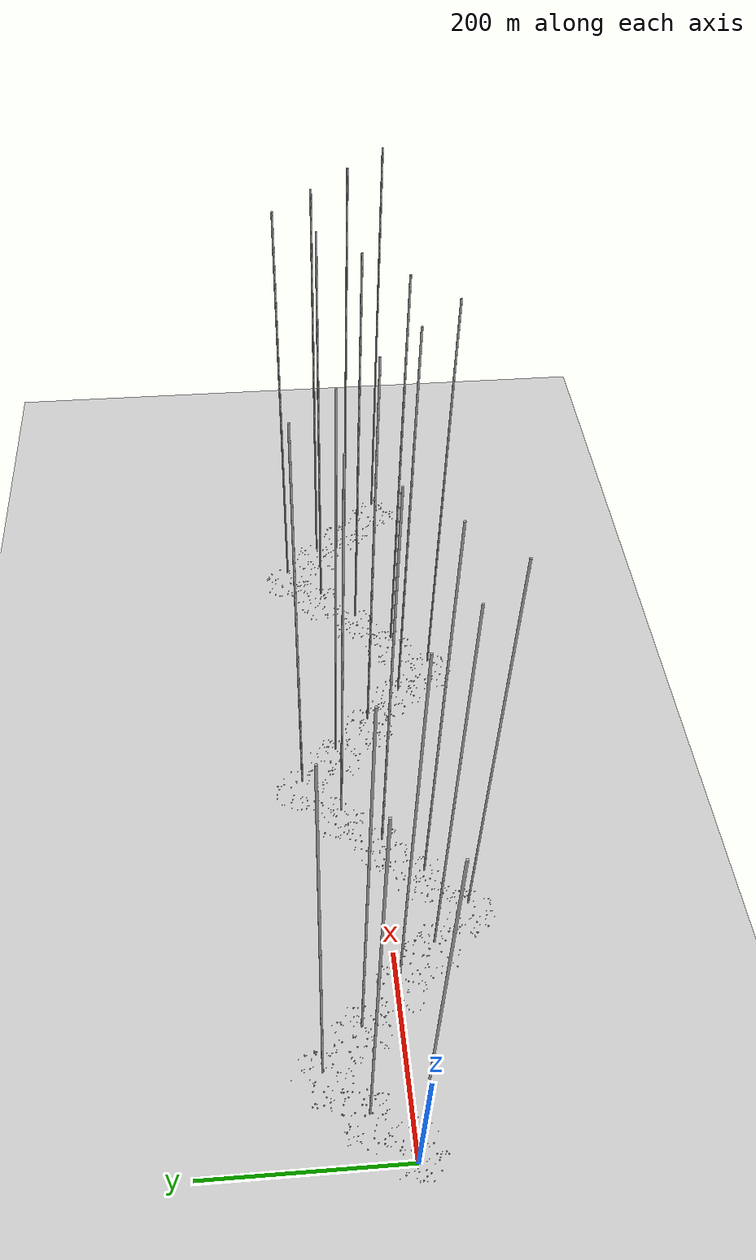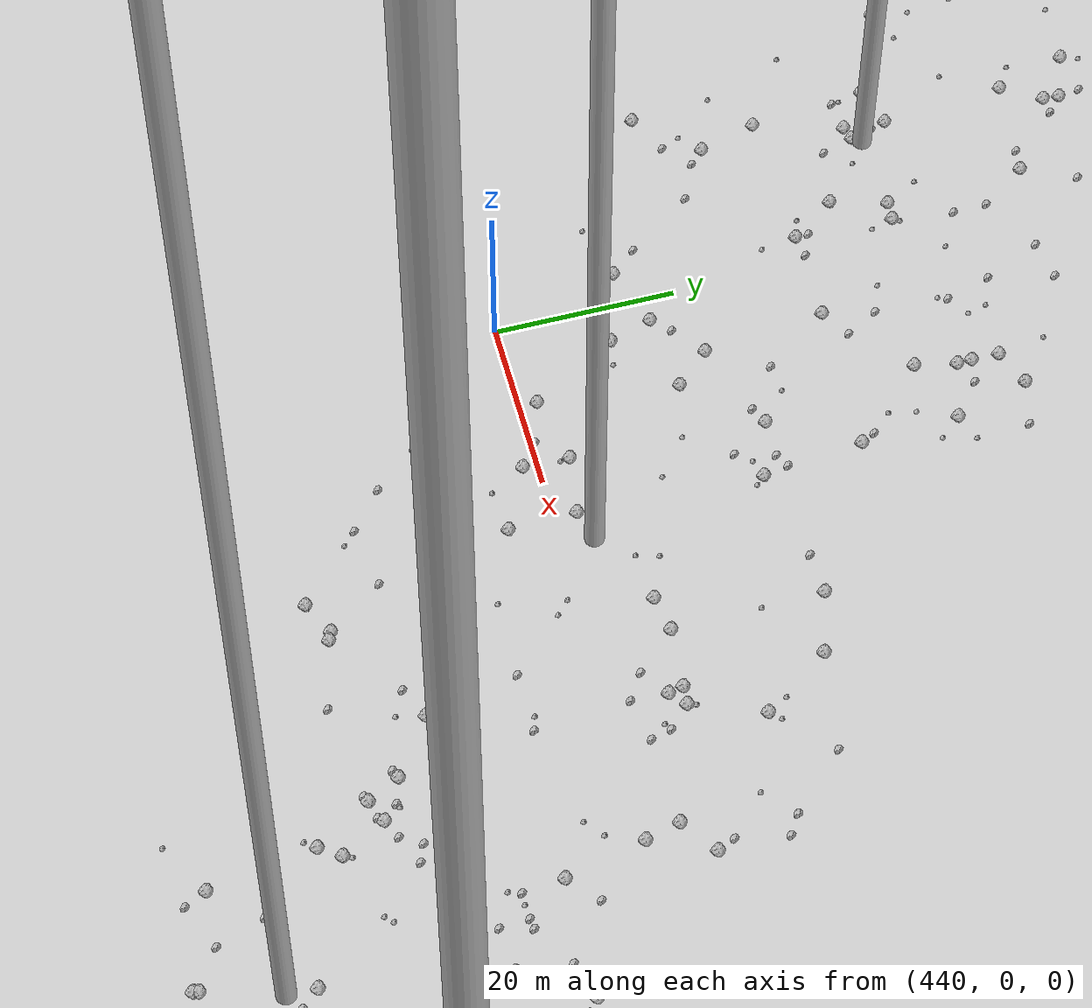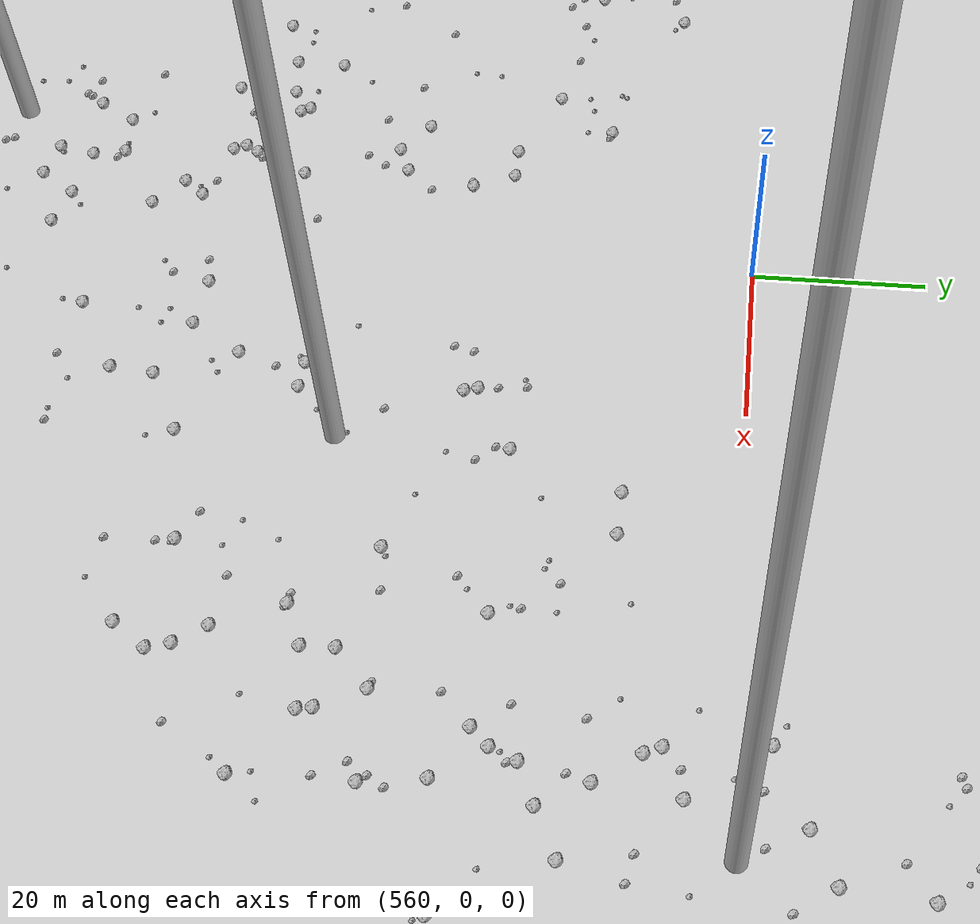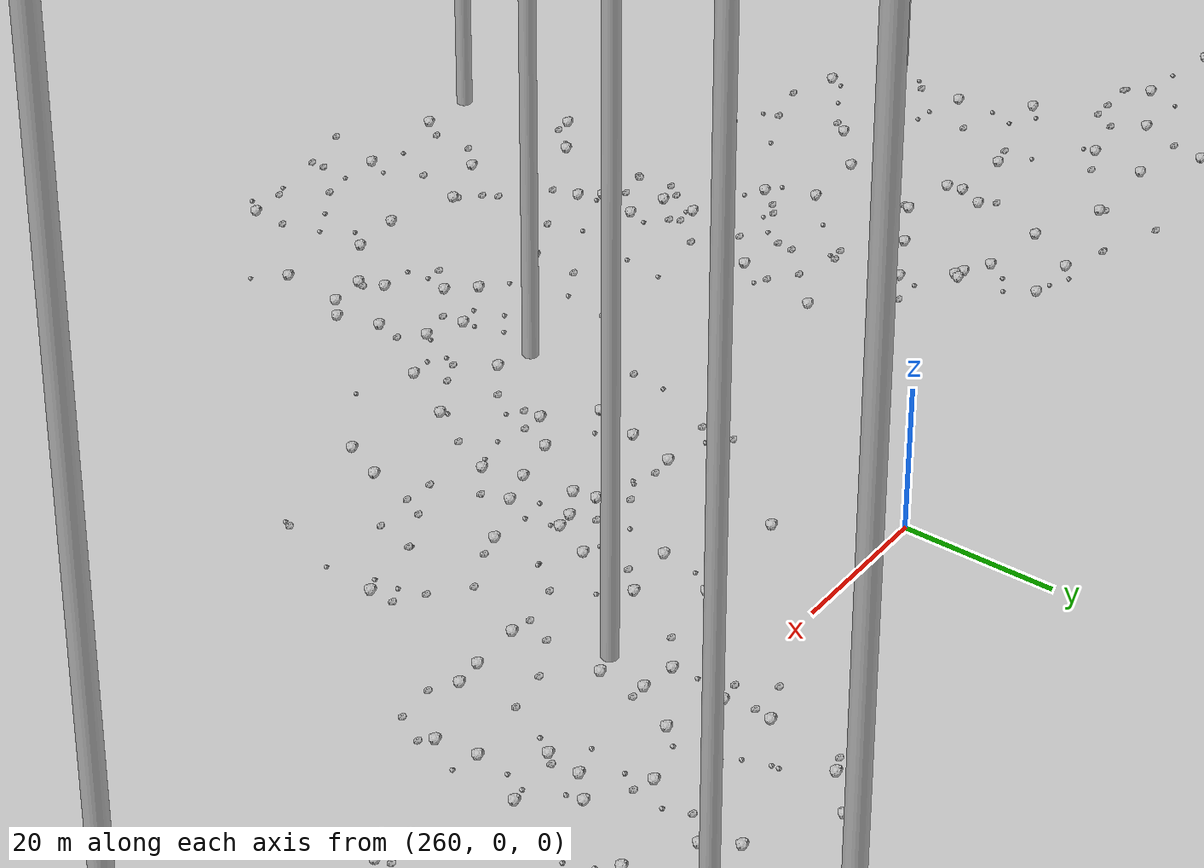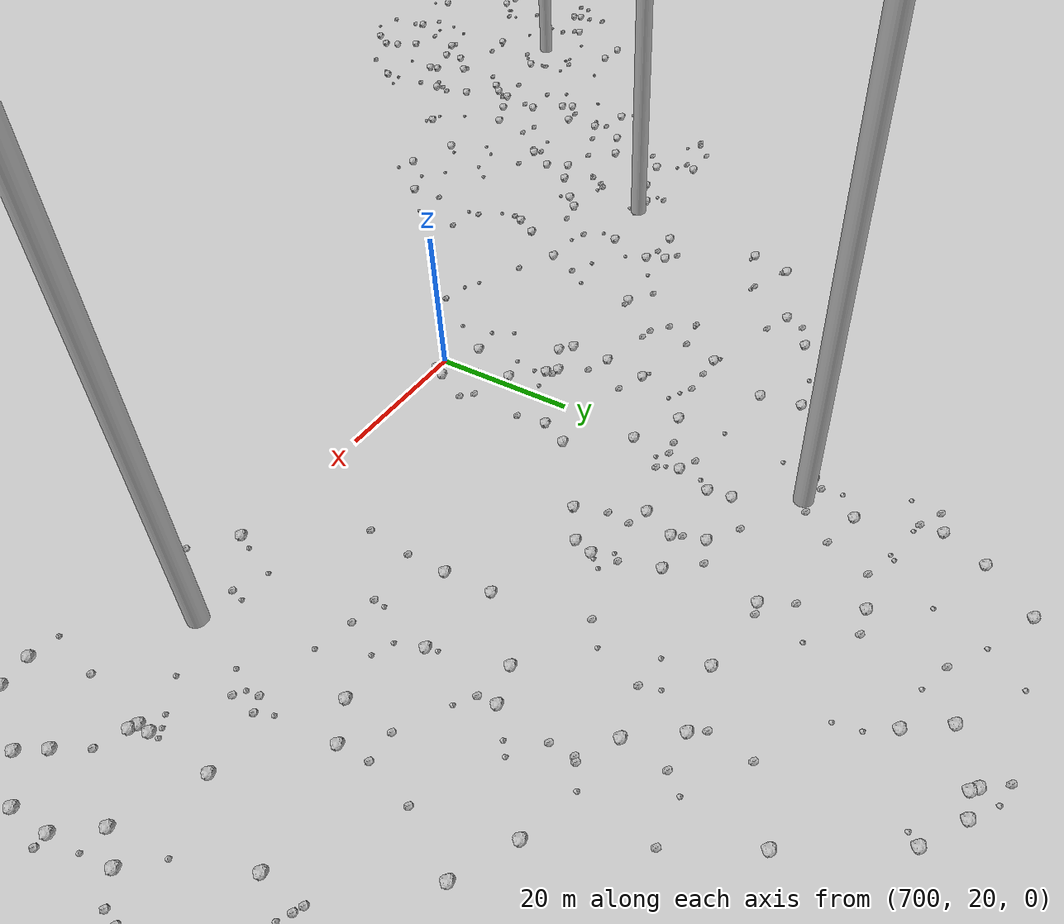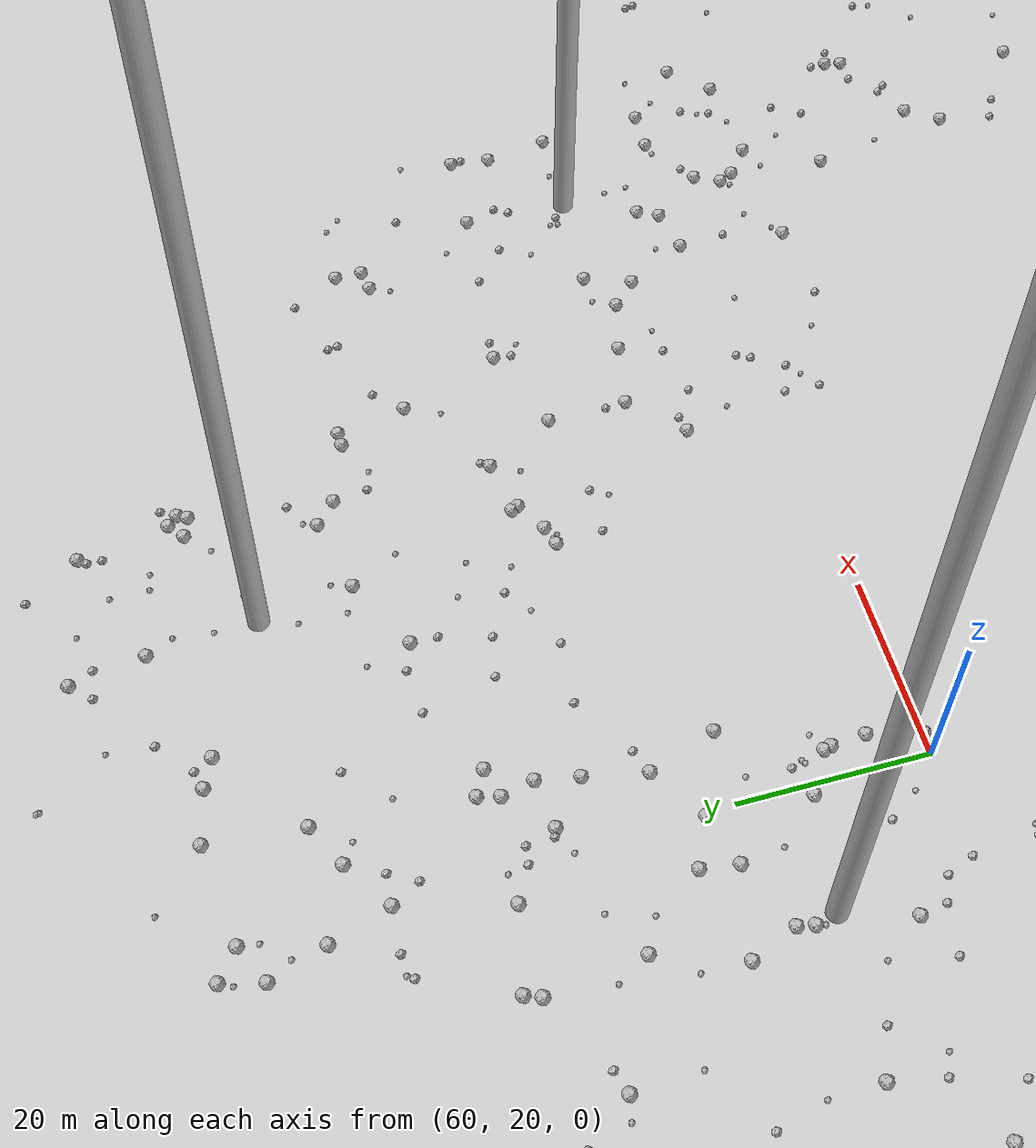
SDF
<sdf version="1.6">
 <world name="default">
  <include><uri>model://custom_ground</uri></include>
  <include><uri>model://sun</uri></include>
  <spherical_coordinates>
   <surface_model>EARTH_WGS84</surface_model>
   <latitude_deg>38.161479</latitude_deg>
   <longitude_deg>-122.454630</longitude_deg>
   <elevation>488.0</elevation>
   <heading_deg>90</heading_deg>
  </spherical_coordinates>
  <model name="rock1_0_0">
   <include><uri>model://rock1</uri><pose>14.659894395524752 13.086769196592634 0.5 0 0 0</pose></include>
  </model>
  <model name="rock1_0_1">
   <include><uri>model://rock1</uri><pose>6.6717406706876226 -2.6753013017908884 0.5 0 0 0</pose></include>
  </model>
  <model name="rock1_0_2">
   <include><uri>model://rock1</uri><pose>-7.783648668982915 -20.286699873148393 0.5 0 0 0</pose></include>
  </model>
  <model name="rock1_0_3">
   <include><uri>model://rock1</uri><pose>5.02865408801981 -3.7733653364635593 0.5 0 0 0</pose></include>
  </model>
  <model name="rock1_0_4">
   <include><uri>model://rock1</uri><pose>-9.127061839912995 -10.409201131706435 0.5 0 0 0</pose></include>
  </model>
  <model name="rock1_0_5">
   <include><uri>model://rock1</uri><pose>29.358810958231977 -10.968042091290958 0.5 0 0 0</pose></include>
  </model>
  <model name="rock1_0_6">
   <include><uri>model://rock1</uri><pose>12.214939148865056 1.0368312488793734 0.5 0 0 0</pose></include>
  </model>
  <model name="rock1_0_7">
   <include><uri>model://rock1</uri><pose>39.387660919335914 -3.903846493488821 0.5 0 0 0</pose></include>
  </model>
  <model name="rock1_0_8">
   <include><uri>model://rock1</uri><pose>31.727976238657057 4.65441083812064 0.5 0 0 0</pose></include>
  </model>
  <model name="rock1_0_9">
   <include><uri>model://rock1</uri><pose>6.28757067367448 -0.1546790672375593 0.5 0 0 0</pose></include>
  </model>
  <model name="rock1_0_10">
   <include><uri>model://rock1</uri><pose>11.991279962522999 14.571357840577477 0.5 0 0 0</pose></include>
  </model>
  <model name="rock1_0_11">
   <include><uri>model://rock1</uri><pose>35.98273822967699 -1.7755476181204557 0.5 0 0 0</pose></include>
  </model>
  <model name="rock1_0_12">
   <include><uri>model://rock1</uri><pose>-15.744508309181676 -12.180375680966026 0.5 0 0 0</pose></include>
  </model>
  <model name="rock1_0_13">
   <include><uri>model://rock1</uri><pose>28.259204671300097 -7.158858658876838 0.5 0 0 0</pose></include>
  </model>
  <model name="rock1_0_14">
   <include><uri>model://rock1</uri><pose>16.22547001362966 -15.949768615086333 0.5 0 0 0</pose></include>
  </model>
  <model name="rock1_0_15">
   <include><uri>model://rock1</uri><pose>11.510901888169734 4.730181539335177 0.5 0 0 0</pose></include>
  </model>
  <model name="rock1_0_16">
   <include><uri>model://rock1</uri><pose>1.4076320895260928 16.495786039047182 0.5 0 0 0</pose></include>
  </model>
  <model name="rock1_0_17">
   <include><uri>model://rock1</uri><pose>8.144847817143408 -26.434898442561575 0.5 0 0 0</pose></include>
  </model>
  <model name="rock1_0_18">
   <include><uri>model://rock1</uri><pose>-14.854611152699642 -2.770304634019073 0.5 0 0 0</pose></include>
  </model>
  <model name="rock1_0_19">
   <include><uri>model://rock1</uri><pose>25.22441599119285 -3.5841132620598692 0.5 0 0 0</pose></include>
  </model>
  <model name="rock1_0_20">
   <include><uri>model://rock1</uri><pose>4.987729896972674 2.629256701547206 0.5 0 0 0</pose></include>
  </model>
  <model name="rock1_0_21">
   <include><uri>model://rock1</uri><pose>-9.218060297735992 11.837069047632049 0.5 0 0 0</pose></include>
  </model>
  <model name="rock1_0_22">
   <include><uri>model://rock1</uri><pose>5.682481298144076 -28.31901193714169 0.5 0 0 0</pose></include>
  </model>
  <model name="rock1_0_23">
   <include><uri>model://rock1</uri><pose>1.387982084525646 -19.251477448239942 0.5 0 0 0</pose></include>
  </model>
  <model name="rock1_0_24">
   <include><uri>model://rock1</uri><pose>0.7323153136306466 17.51631770109107 0.5 0 0 0</pose></include>
  </model>
  <model name="rock1_0_25">
   <include><uri>model://rock1</uri><pose>-11.272184860528307 -6.410313886063069 0.5 0 0 0</pose></include>
  </model>
  <model name="rock1_0_26">
   <include><uri>model://rock1</uri><pose>6.894922634666628 -17.807170712664735 0.5 0 0 0</pose></include>
  </model>
  <model name="rock2_0_0">
   <include><uri>model://rock2</uri><pose>33.2902566627635 -16.35165401235166 0.3 0 0 0</pose></include>
  </model>
  <model name="rock2_0_1">
   <include><uri>model://rock2</uri><pose>-4.203114143516199 0.7443169295683987 0.3 0 0 0</pose></include>
  </model>
  <model name="rock2_0_2">
   <include><uri>model://rock2</uri><pose>16.19849833996114 22.46062344433372 0.3 0 0 0</pose></include>
  </model>
  <model name="rock2_0_3">
   <include><uri>model://rock2</uri><pose>33.83948262465287 -13.965435966760232 0.3 0 0 0</pose></include>
  </model>
  <model name="rock2_0_4">
   <include><uri>model://rock2</uri><pose>26.1181998507615 -21.383714463631698 0.3 0 0 0</pose></include>
  </model>
  <model name="rock2_0_5">
   <include><uri>model://rock2</uri><pose>27.622352544745098 23.82097902897919 0.3 0 0 0</pose></include>
  </model>
  <model name="rock2_0_6">
   <include><uri>model://rock2</uri><pose>11.47352756000041 -2.3603357597451335 0.3 0 0 0</pose></include>
  </model>
  <model name="rock2_0_7">
   <include><uri>model://rock2</uri><pose>15.912147227717433 -10.547030572665616 0.3 0 0 0</pose></include>
  </model>
  <model name="rock2_0_8">
   <include><uri>model://rock2</uri><pose>16.072647991342585 26.551086276850647 0.3 0 0 0</pose></include>
  </model>
  <model name="rock2_0_9">
   <include><uri>model://rock2</uri><pose>29.425035100178718 10.544171782036294 0.3 0 0 0</pose></include>
  </model>
  <model name="rock2_0_10">
   <include><uri>model://rock2</uri><pose>-12.261219951652592 2.701796059175699 0.3 0 0 0</pose></include>
  </model>
  <model name="rock2_0_11">
   <include><uri>model://rock2</uri><pose>-1.3816596623810966 -14.829860122566823 0.3 0 0 0</pose></include>
  </model>
  <model name="rock2_0_12">
   <include><uri>model://rock2</uri><pose>12.205077876320217 10.833912981000779 0.3 0 0 0</pose></include>
  </model>
  <model name="rock2_0_13">
   <include><uri>model://rock2</uri><pose>-7.157438648566131 0.2426659109617333 0.3 0 0 0</pose></include>
  </model>
  <model name="rock2_0_14">
   <include><uri>model://rock2</uri><pose>6.0895616583157555 -25.632871217310424 0.3 0 0 0</pose></include>
  </model>
  <model name="rock2_0_15">
   <include><uri>model://rock2</uri><pose>19.79463295827012 18.244303556286923 0.3 0 0 0</pose></include>
  </model>
  <model name="rock2_0_16">
   <include><uri>model://rock2</uri><pose>3.5130374314168016 -20.112148829223393 0.3 0 0 0</pose></include>
  </model>
  <model name="rock2_0_17">
   <include><uri>model://rock2</uri><pose>8.123393088795986 -22.518744557812788 0.3 0 0 0</pose></include>
  </model>
  <model name="rock2_0_18">
   <include><uri>model://rock2</uri><pose>6.110491559894882 -21.312689119829464 0.3 0 0 0</pose></include>
  </model>
  <model name="rock2_0_19">
   <include><uri>model://rock2</uri><pose>2.6249820106218706 -10.412431487218356 0.3 0 0 0</pose></include>
  </model>
  <model name="rock2_0_20">
   <include><uri>model://rock2</uri><pose>27.62897781815299 -2.438800583881733 0.3 0 0 0</pose></include>
  </model>
  <model name="rock2_0_21">
   <include><uri>model://rock2</uri><pose>-6.059093960260482 -6.715530731663197 0.3 0 0 0</pose></include>
  </model>
  <model name="rock2_0_22">
   <include><uri>model://rock2</uri><pose>20.30865073213758 11.09892670647259 0.3 0 0 0</pose></include>
  </model>
  <model name="rock2_0_23">
   <include><uri>model://rock2</uri><pose>8.577178416683484 12.476705422977211 0.3 0 0 0</pose></include>
  </model>
  <model name="rock2_0_24">
   <include><uri>model://rock2</uri><pose>1.2154787757873962 -7.654187189357518 0.3 0 0 0</pose></include>
  </model>
  <model name="rock2_0_25">
   <include><uri>model://rock2</uri><pose>-6.808029682766319 11.187501312737773 0.3 0 0 0</pose></include>
  </model>
  <model name="rock2_0_26">
   <include><uri>model://rock2</uri><pose>-16.192526909169295 0.19206881617170524 0.3 0 0 0</pose></include>
  </model>
  <model name="rock3_0_0">
   <include><uri>model://rock3</uri><pose>-11.62991971184699 17.963360070035662 0.2 0 0 0</pose></include>
  </model>
  <model name="rock3_0_1">
   <include><uri>model://rock3</uri><pose>19.55302938564219 11.347479104792285 0.2 0 0 0</pose></include>
  </model>
  <model name="rock3_0_2">
   <include><uri>model://rock3</uri><pose>2.0033935875181186 -19.345895198276075 0.2 0 0 0</pose></include>
  </model>
  <model name="rock3_0_3">
   <include><uri>model://rock3</uri><pose>11.844282494440176 4.337860020001116 0.2 0 0 0</pose></include>
  </model>
  <model name="rock3_0_4">
   <include><uri>model://rock3</uri><pose>26.944588722784516 -8.497453853792198 0.2 0 0 0</pose></include>
  </model>
  <model name="rock3_0_5">
   <include><uri>model://rock3</uri><pose>38.39187446832932 -3.690025062568207 0.2 0 0 0</pose></include>
  </model>
  <model name="rock3_0_6">
   <include><uri>model://rock3</uri><pose>-6.46999572567948 -6.056616681075724 0.2 0 0 0</pose></include>
  </model>
  <model name="rock3_0_7">
   <include><uri>model://rock3</uri><pose>9.720964398680785 4.443946506740062 0.2 0 0 0</pose></include>
  </model>
  <model name="rock3_0_8">
   <include><uri>model://rock3</uri><pose>-6.870574026676099 9.318665565174364 0.2 0 0 0</pose></include>
  </model>
  <model name="rock3_0_9">
   <include><uri>model://rock3</uri><pose>-14.06299559384119 -14.805760054507806 0.2 0 0 0</pose></include>
  </model>
  <model name="rock3_0_10">
   <include><uri>model://rock3</uri><pose>-15.701658018446384 -6.052372089434844 0.2 0 0 0</pose></include>
  </model>
  <model name="rock3_0_11">
   <include><uri>model://rock3</uri><pose>11.161267358840732 20.529034405740326 0.2 0 0 0</pose></include>
  </model>
  <model name="rock3_0_12">
   <include><uri>model://rock3</uri><pose>7.914308021571813 11.510213227944341 0.2 0 0 0</pose></include>
  </model>
  <model name="rock3_0_13">
   <include><uri>model://rock3</uri><pose>15.301417248059195 -0.9336718710621419 0.2 0 0 0</pose></include>
  </model>
  <model name="rock3_0_14">
   <include><uri>model://rock3</uri><pose>34.74526172188516 1.6215250221182025 0.2 0 0 0</pose></include>
  </model>
  <model name="rock3_0_15">
   <include><uri>model://rock3</uri><pose>13.782949140650025 26.195407434152415 0.2 0 0 0</pose></include>
  </model>
  <model name="rock3_0_16">
   <include><uri>model://rock3</uri><pose>13.441566289825701 -11.762186192619804 0.2 0 0 0</pose></include>
  </model>
  <model name="rock3_0_17">
   <include><uri>model://rock3</uri><pose>-3.519353003609133 6.217739685329093 0.2 0 0 0</pose></include>
  </model>
  <model name="rock3_0_18">
   <include><uri>model://rock3</uri><pose>26.109504238987945 3.0683690113144735 0.2 0 0 0</pose></include>
  </model>
  <model name="rock3_0_19">
   <include><uri>model://rock3</uri><pose>-6.717264240738441 -24.37999280335895 0.2 0 0 0</pose></include>
  </model>
  <model name="rock3_0_20">
   <include><uri>model://rock3</uri><pose>-5.893924691384225 4.038673561262243 0.2 0 0 0</pose></include>
  </model>
  <model name="rock3_0_21">
   <include><uri>model://rock3</uri><pose>2.3302649569340126 12.33419611070196 0.2 0 0 0</pose></include>
  </model>
  <model name="rock3_0_22">
   <include><uri>model://rock3</uri><pose>9.308546623343052 -7.713580710708463 0.2 0 0 0</pose></include>
  </model>
  <model name="rock3_0_23">
   <include><uri>model://rock3</uri><pose>-14.362882757559438 -0.011066669172254961 0.2 0 0 0</pose></include>
  </model>
  <model name="rock3_0_24">
   <include><uri>model://rock3</uri><pose>-10.394239466441515 -19.862990731336907 0.2 0 0 0</pose></include>
  </model>
  <model name="rock3_0_25">
   <include><uri>model://rock3</uri><pose>29.588447762655044 -12.706146412703106 0.2 0 0 0</pose></include>
  </model>
  <model name="rock3_0_26">
   <include><uri>model://rock3</uri><pose>-13.068342180817718 8.230131992279588 0.2 0 0 0</pose></include>
  </model>
  <model name="rock1_1_0">
   <include><uri>model://rock1</uri><pose>62.22395597894915 20.04736621051638 0.5 0 0 0</pose></include>
  </model>
  <model name="rock1_1_1">
   <include><uri>model://rock1</uri><pose>55.676642499635555 62.77502960904606 0.5 0 0 0</pose></include>
  </model>
  <model name="rock1_1_2">
   <include><uri>model://rock1</uri><pose>46.65111228793825 38.746616719952456 0.5 0 0 0</pose></include>
  </model>
  <model name="rock1_1_3">
   <include><uri>model://rock1</uri><pose>46.28960755664127 36.98347420288141 0.5 0 0 0</pose></include>
  </model>
  <model name="rock1_1_4">
   <include><uri>model://rock1</uri><pose>14.766886711402671 43.93912942967574 0.5 0 0 0</pose></include>
  </model>
  <model name="rock1_1_5">
   <include><uri>model://rock1</uri><pose>63.085901593700505 30.04051674396441 0.5 0 0 0</pose></include>
  </model>
  <model name="rock1_1_6">
   <include><uri>model://rock1</uri><pose>22.640285739163197 27.279697980428775 0.5 0 0 0</pose></include>
  </model>
  <model name="rock1_1_7">
   <include><uri>model://rock1</uri><pose>35.76633186174747 58.211864680858184 0.5 0 0 0</pose></include>
  </model>
  <model name="rock1_1_8">
   <include><uri>model://rock1</uri><pose>59.4734397824336 43.23660093415967 0.5 0 0 0</pose></include>
  </model>
  <model name="rock1_1_9">
   <include><uri>model://rock1</uri><pose>54.47886107943235 45.579330120560684 0.5 0 0 0</pose></include>
  </model>
  <model name="rock1_1_10">
   <include><uri>model://rock1</uri><pose>62.15468113811741 57.30891368431046 0.5 0 0 0</pose></include>
  </model>
  <model name="rock1_1_11">
   <include><uri>model://rock1</uri><pose>47.71609801423285 52.684386365503485 0.5 0 0 0</pose></include>
  </model>
  <model name="rock1_1_12">
   <include><uri>model://rock1</uri><pose>19.98503863642088 33.90099687582421 0.5 0 0 0</pose></include>
  </model>
  <model name="rock1_1_13">
   <include><uri>model://rock1</uri><pose>44.56098899187616 27.373722707781745 0.5 0 0 0</pose></include>
  </model>
  <model name="rock1_1_14">
   <include><uri>model://rock1</uri><pose>58.81437229816824 32.5890291774554 0.5 0 0 0</pose></include>
  </model>
  <model name="rock1_1_15">
   <include><uri>model://rock1</uri><pose>63.32028453313115 29.20961322887458 0.5 0 0 0</pose></include>
  </model>
  <model name="rock1_1_16">
   <include><uri>model://rock1</uri><pose>65.34083162363524 46.967865246052035 0.5 0 0 0</pose></include>
  </model>
  <model name="rock1_1_17">
   <include><uri>model://rock1</uri><pose>18.64530475586278 28.204977298881303 0.5 0 0 0</pose></include>
  </model>
  <model name="rock1_1_18">
   <include><uri>model://rock1</uri><pose>30.684300726180133 36.040950213242134 0.5 0 0 0</pose></include>
  </model>
  <model name="rock1_1_19">
   <include><uri>model://rock1</uri><pose>30.4556767569122 61.8392062499225 0.5 0 0 0</pose></include>
  </model>
  <model name="rock1_1_20">
   <include><uri>model://rock1</uri><pose>67.91073217006283 39.66359687535676 0.5 0 0 0</pose></include>
  </model>
  <model name="rock1_1_21">
   <include><uri>model://rock1</uri><pose>25.605685576400674 23.014438141779117 0.5 0 0 0</pose></include>
  </model>
  <model name="rock1_1_22">
   <include><uri>model://rock1</uri><pose>46.37273730432119 63.0959398420484 0.5 0 0 0</pose></include>
  </model>
  <model name="rock1_1_23">
   <include><uri>model://rock1</uri><pose>47.0314053650998 64.75524114881644 0.5 0 0 0</pose></include>
  </model>
  <model name="rock1_1_24">
   <include><uri>model://rock1</uri><pose>53.91858698056452 41.6581615447876 0.5 0 0 0</pose></include>
  </model>
  <model name="rock1_1_25">
   <include><uri>model://rock1</uri><pose>63.60601554326023 25.53720107885453 0.5 0 0 0</pose></include>
  </model>
  <model name="rock1_1_26">
   <include><uri>model://rock1</uri><pose>44.547090932834394 43.78243572057358 0.5 0 0 0</pose></include>
  </model>
  <model name="rock2_1_0">
   <include><uri>model://rock2</uri><pose>10.852810386093603 36.47361903090596 0.3 0 0 0</pose></include>
  </model>
  <model name="rock2_1_1">
   <include><uri>model://rock2</uri><pose>22.142833609625264 49.82754780966666 0.3 0 0 0</pose></include>
  </model>
  <model name="rock2_1_2">
   <include><uri>model://rock2</uri><pose>47.69174831123588 23.280087044070548 0.3 0 0 0</pose></include>
  </model>
  <model name="rock2_1_3">
   <include><uri>model://rock2</uri><pose>27.4316975706296 51.46714317655203 0.3 0 0 0</pose></include>
  </model>
  <model name="rock2_1_4">
   <include><uri>model://rock2</uri><pose>29.6042738118993 30.52864492145918 0.3 0 0 0</pose></include>
  </model>
  <model name="rock2_1_5">
   <include><uri>model://rock2</uri><pose>35.53151425366718 34.06306521681562 0.3 0 0 0</pose></include>
  </model>
  <model name="rock2_1_6">
   <include><uri>model://rock2</uri><pose>36.44513898841102 10.982933247078128 0.3 0 0 0</pose></include>
  </model>
  <model name="rock2_1_7">
   <include><uri>model://rock2</uri><pose>32.013053634267024 63.17908752638967 0.3 0 0 0</pose></include>
  </model>
  <model name="rock2_1_8">
   <include><uri>model://rock2</uri><pose>24.10890707618848 37.04283811065015 0.3 0 0 0</pose></include>
  </model>
  <model name="rock2_1_9">
   <include><uri>model://rock2</uri><pose>19.843157701536093 61.65080646968253 0.3 0 0 0</pose></include>
  </model>
  <model name="rock2_1_10">
   <include><uri>model://rock2</uri><pose>32.21720602456008 15.872536234012227 0.3 0 0 0</pose></include>
  </model>
  <model name="rock2_1_11">
   <include><uri>model://rock2</uri><pose>39.92415009328657 25.325738177481227 0.3 0 0 0</pose></include>
  </model>
  <model name="rock2_1_12">
   <include><uri>model://rock2</uri><pose>48.86640604945933 20.36300172786148 0.3 0 0 0</pose></include>
  </model>
  <model name="rock2_1_13">
   <include><uri>model://rock2</uri><pose>61.14728572085966 60.497416235519346 0.3 0 0 0</pose></include>
  </model>
  <model name="rock2_1_14">
   <include><uri>model://rock2</uri><pose>24.99587904225379 60.12842182148237 0.3 0 0 0</pose></include>
  </model>
  <model name="rock2_1_15">
   <include><uri>model://rock2</uri><pose>20.496547900742453 59.38811962298142 0.3 0 0 0</pose></include>
  </model>
  <model name="rock2_1_16">
   <include><uri>model://rock2</uri><pose>21.076339417664794 49.0835880643871 0.3 0 0 0</pose></include>
  </model>
  <model name="rock2_1_17">
   <include><uri>model://rock2</uri><pose>54.39546720714509 26.279994675450197 0.3 0 0 0</pose></include>
  </model>
  <model name="rock2_1_18">
   <include><uri>model://rock2</uri><pose>24.649720020056975 20.75408584582409 0.3 0 0 0</pose></include>
  </model>
  <model name="rock2_1_19">
   <include><uri>model://rock2</uri><pose>38.219267463447125 58.92174349258483 0.3 0 0 0</pose></include>
  </model>
  <model name="rock2_1_20">
   <include><uri>model://rock2</uri><pose>31.282365099948176 61.43744978336944 0.3 0 0 0</pose></include>
  </model>
  <model name="rock2_1_21">
   <include><uri>model://rock2</uri><pose>27.102525296077992 55.66103179276289 0.3 0 0 0</pose></include>
  </model>
  <model name="rock2_1_22">
   <include><uri>model://rock2</uri><pose>67.95876723837894 47.83380604768462 0.3 0 0 0</pose></include>
  </model>
  <model name="rock2_1_23">
   <include><uri>model://rock2</uri><pose>29.1465443908943 46.83971634191736 0.3 0 0 0</pose></include>
  </model>
  <model name="rock2_1_24">
   <include><uri>model://rock2</uri><pose>31.91010542299326 20.254929545857582 0.3 0 0 0</pose></include>
  </model>
  <model name="rock2_1_25">
   <include><uri>model://rock2</uri><pose>62.10248614629701 33.60511509326835 0.3 0 0 0</pose></include>
  </model>
  <model name="rock2_1_26">
   <include><uri>model://rock2</uri><pose>45.080531773382326 24.454335347182976 0.3 0 0 0</pose></include>
  </model>
  <model name="rock3_1_0">
   <include><uri>model://rock3</uri><pose>54.48567345921761 37.006831604905344 0.2 0 0 0</pose></include>
  </model>
  <model name="rock3_1_1">
   <include><uri>model://rock3</uri><pose>20.006591156793295 45.6118393451636 0.2 0 0 0</pose></include>
  </model>
  <model name="rock3_1_2">
   <include><uri>model://rock3</uri><pose>59.21824977370865 56.23746260507593 0.2 0 0 0</pose></include>
  </model>
  <model name="rock3_1_3">
   <include><uri>model://rock3</uri><pose>52.609136939388335 55.2941507543718 0.2 0 0 0</pose></include>
  </model>
  <model name="rock3_1_4">
   <include><uri>model://rock3</uri><pose>33.56773214560457 14.093763025443412 0.2 0 0 0</pose></include>
  </model>
  <model name="rock3_1_5">
   <include><uri>model://rock3</uri><pose>65.03375322731857 30.734576645345527 0.2 0 0 0</pose></include>
  </model>
  <model name="rock3_1_6">
   <include><uri>model://rock3</uri><pose>44.714864598938156 48.581839621866216 0.2 0 0 0</pose></include>
  </model>
  <model name="rock3_1_7">
   <include><uri>model://rock3</uri><pose>16.719685705802277 25.601762836183433 0.2 0 0 0</pose></include>
  </model>
  <model name="rock3_1_8">
   <include><uri>model://rock3</uri><pose>51.16350323788483 50.79887467206254 0.2 0 0 0</pose></include>
  </model>
  <model name="rock3_1_9">
   <include><uri>model://rock3</uri><pose>45.75390440277892 56.044050650877644 0.2 0 0 0</pose></include>
  </model>
  <model name="rock3_1_10">
   <include><uri>model://rock3</uri><pose>56.68063576305709 22.972398756552693 0.2 0 0 0</pose></include>
  </model>
  <model name="rock3_1_11">
   <include><uri>model://rock3</uri><pose>62.42224032901197 38.167084044800845 0.2 0 0 0</pose></include>
  </model>
  <model name="rock3_1_12">
   <include><uri>model://rock3</uri><pose>49.245045119247244 13.569315270209731 0.2 0 0 0</pose></include>
  </model>
  <model name="rock3_1_13">
   <include><uri>model://rock3</uri><pose>62.5327423030941 56.83993878608795 0.2 0 0 0</pose></include>
  </model>
  <model name="rock3_1_14">
   <include><uri>model://rock3</uri><pose>23.271927923716795 52.80281392755024 0.2 0 0 0</pose></include>
  </model>
  <model name="rock3_1_15">
   <include><uri>model://rock3</uri><pose>50.34412843440112 13.302862065418505 0.2 0 0 0</pose></include>
  </model>
  <model name="rock3_1_16">
   <include><uri>model://rock3</uri><pose>62.63685882503104 32.39617690392265 0.2 0 0 0</pose></include>
  </model>
  <model name="rock3_1_17">
   <include><uri>model://rock3</uri><pose>31.805999733374215 29.549514804596857 0.2 0 0 0</pose></include>
  </model>
  <model name="rock3_1_18">
   <include><uri>model://rock3</uri><pose>58.822690779832406 62.83836555126133 0.2 0 0 0</pose></include>
  </model>
  <model name="rock3_1_19">
   <include><uri>model://rock3</uri><pose>33.31904039685728 58.71927929714248 0.2 0 0 0</pose></include>
  </model>
  <model name="rock3_1_20">
   <include><uri>model://rock3</uri><pose>41.2873148608231 31.740528678922384 0.2 0 0 0</pose></include>
  </model>
  <model name="rock3_1_21">
   <include><uri>model://rock3</uri><pose>46.107481159557594 35.97236212761703 0.2 0 0 0</pose></include>
  </model>
  <model name="rock3_1_22">
   <include><uri>model://rock3</uri><pose>24.72253907976814 37.55930240188265 0.2 0 0 0</pose></include>
  </model>
  <model name="rock3_1_23">
   <include><uri>model://rock3</uri><pose>62.26900979127811 32.14827983207251 0.2 0 0 0</pose></include>
  </model>
  <model name="rock3_1_24">
   <include><uri>model://rock3</uri><pose>30.589710785422664 41.51417117915639 0.2 0 0 0</pose></include>
  </model>
  <model name="rock3_1_25">
   <include><uri>model://rock3</uri><pose>52.700512274528634 29.25500074416171 0.2 0 0 0</pose></include>
  </model>
  <model name="rock3_1_26">
   <include><uri>model://rock3</uri><pose>36.0795539959574 51.09786227808102 0.2 0 0 0</pose></include>
  </model>
  <model name="rock1_2_0">
   <include><uri>model://rock1</uri><pose>55.59491409447874 91.1118445641365 0.5 0 0 0</pose></include>
  </model>
  <model name="rock1_2_1">
   <include><uri>model://rock1</uri><pose>85.48302866840297 65.64259465372949 0.5 0 0 0</pose></include>
  </model>
  <model name="rock1_2_2">
   <include><uri>model://rock1</uri><pose>67.30843720454128 63.68646334467984 0.5 0 0 0</pose></include>
  </model>
  <model name="rock1_2_3">
   <include><uri>model://rock1</uri><pose>93.52540559904695 69.66605099988537 0.5 0 0 0</pose></include>
  </model>
  <model name="rock1_2_4">
   <include><uri>model://rock1</uri><pose>101.70122127479067 71.4690721047272 0.5 0 0 0</pose></include>
  </model>
  <model name="rock1_2_5">
   <include><uri>model://rock1</uri><pose>58.63260153793538 88.73248670555594 0.5 0 0 0</pose></include>
  </model>
  <model name="rock1_2_6">
   <include><uri>model://rock1</uri><pose>66.65917403126284 53.4623476687822 0.5 0 0 0</pose></include>
  </model>
  <model name="rock1_2_7">
   <include><uri>model://rock1</uri><pose>106.22977056965695 84.23602370267159 0.5 0 0 0</pose></include>
  </model>
  <model name="rock1_2_8">
   <include><uri>model://rock1</uri><pose>104.1761777624935 69.2385023917641 0.5 0 0 0</pose></include>
  </model>
  <model name="rock1_2_9">
   <include><uri>model://rock1</uri><pose>58.6696853352676 74.11155141260267 0.5 0 0 0</pose></include>
  </model>
  <model name="rock1_2_10">
   <include><uri>model://rock1</uri><pose>68.56137629705142 79.80137526051988 0.5 0 0 0</pose></include>
  </model>
  <model name="rock1_2_11">
   <include><uri>model://rock1</uri><pose>78.25347096161795 87.15097595721359 0.5 0 0 0</pose></include>
  </model>
  <model name="rock1_2_12">
   <include><uri>model://rock1</uri><pose>67.51437670989375 57.91562049643913 0.5 0 0 0</pose></include>
  </model>
  <model name="rock1_2_13">
   <include><uri>model://rock1</uri><pose>106.7944312610085 85.25803196532726 0.5 0 0 0</pose></include>
  </model>
  <model name="rock1_2_14">
   <include><uri>model://rock1</uri><pose>95.18830530450099 80.07170941356902 0.5 0 0 0</pose></include>
  </model>
  <model name="rock1_2_15">
   <include><uri>model://rock1</uri><pose>89.76374569749393 99.25432349345664 0.5 0 0 0</pose></include>
  </model>
  <model name="rock1_2_16">
   <include><uri>model://rock1</uri><pose>105.74336646757448 86.3526978886426 0.5 0 0 0</pose></include>
  </model>
  <model name="rock1_2_17">
   <include><uri>model://rock1</uri><pose>63.91914961341712 77.52556607837438 0.5 0 0 0</pose></include>
  </model>
  <model name="rock1_2_18">
   <include><uri>model://rock1</uri><pose>54.4828355447355 86.76818001884607 0.5 0 0 0</pose></include>
  </model>
  <model name="rock1_2_19">
   <include><uri>model://rock1</uri><pose>56.538892206852886 80.64720456902637 0.5 0 0 0</pose></include>
  </model>
  <model name="rock1_2_20">
   <include><uri>model://rock1</uri><pose>66.69361422636649 61.41744414082746 0.5 0 0 0</pose></include>
  </model>
  <model name="rock1_2_21">
   <include><uri>model://rock1</uri><pose>91.11435476000929 91.28729878160132 0.5 0 0 0</pose></include>
  </model>
  <model name="rock1_2_22">
   <include><uri>model://rock1</uri><pose>69.44575920987046 89.956736150112 0.5 0 0 0</pose></include>
  </model>
  <model name="rock1_2_23">
   <include><uri>model://rock1</uri><pose>69.9520889340175 62.268685096896235 0.5 0 0 0</pose></include>
  </model>
  <model name="rock1_2_24">
   <include><uri>model://rock1</uri><pose>75.17934045814943 88.61443345078231 0.5 0 0 0</pose></include>
  </model>
  <model name="rock1_2_25">
   <include><uri>model://rock1</uri><pose>104.13875591983086 96.04807375553916 0.5 0 0 0</pose></include>
  </model>
  <model name="rock1_2_26">
   <include><uri>model://rock1</uri><pose>104.0641037820054 85.01797118917708 0.5 0 0 0</pose></include>
  </model>
  <model name="rock2_2_0">
   <include><uri>model://rock2</uri><pose>77.53161962744328 66.34606252074836 0.3 0 0 0</pose></include>
  </model>
  <model name="rock2_2_1">
   <include><uri>model://rock2</uri><pose>61.968674772589395 73.82896044924198 0.3 0 0 0</pose></include>
  </model>
  <model name="rock2_2_2">
   <include><uri>model://rock2</uri><pose>104.79416572215206 74.03370276094095 0.3 0 0 0</pose></include>
  </model>
  <model name="rock2_2_3">
   <include><uri>model://rock2</uri><pose>82.51982082387993 66.71654271168708 0.3 0 0 0</pose></include>
  </model>
  <model name="rock2_2_4">
   <include><uri>model://rock2</uri><pose>103.46283231568793 93.62199257807725 0.3 0 0 0</pose></include>
  </model>
  <model name="rock2_2_5">
   <include><uri>model://rock2</uri><pose>81.43389855865964 51.13548162354549 0.3 0 0 0</pose></include>
  </model>
  <model name="rock2_2_6">
   <include><uri>model://rock2</uri><pose>83.9754363312961 57.47920788255525 0.3 0 0 0</pose></include>
  </model>
  <model name="rock2_2_7">
   <include><uri>model://rock2</uri><pose>61.31373250395133 57.602325974032325 0.3 0 0 0</pose></include>
  </model>
  <model name="rock2_2_8">
   <include><uri>model://rock2</uri><pose>59.26264207219538 60.7852267298294 0.3 0 0 0</pose></include>
  </model>
  <model name="rock2_2_9">
   <include><uri>model://rock2</uri><pose>69.82088010756017 89.96780005745939 0.3 0 0 0</pose></include>
  </model>
  <model name="rock2_2_10">
   <include><uri>model://rock2</uri><pose>103.51447828354208 95.20480733699836 0.3 0 0 0</pose></include>
  </model>
  <model name="rock2_2_11">
   <include><uri>model://rock2</uri><pose>100.37950220019344 101.94797588353038 0.3 0 0 0</pose></include>
  </model>
  <model name="rock2_2_12">
   <include><uri>model://rock2</uri><pose>74.60162838179849 51.793807034133664 0.3 0 0 0</pose></include>
  </model>
  <model name="rock2_2_13">
   <include><uri>model://rock2</uri><pose>79.51152045638536 58.44599831945099 0.3 0 0 0</pose></include>
  </model>
  <model name="rock2_2_14">
   <include><uri>model://rock2</uri><pose>60.38135831472988 71.00999409183095 0.3 0 0 0</pose></include>
  </model>
  <model name="rock2_2_15">
   <include><uri>model://rock2</uri><pose>104.68169672417 65.45360867198362 0.3 0 0 0</pose></include>
  </model>
  <model name="rock2_2_16">
   <include><uri>model://rock2</uri><pose>80.94633237538889 92.23134607177096 0.3 0 0 0</pose></include>
  </model>
  <model name="rock2_2_17">
   <include><uri>model://rock2</uri><pose>81.12437455332577 109.8383522197879 0.3 0 0 0</pose></include>
  </model>
  <model name="rock2_2_18">
   <include><uri>model://rock2</uri><pose>90.90647691299372 96.67726064353656 0.3 0 0 0</pose></include>
  </model>
  <model name="rock2_2_19">
   <include><uri>model://rock2</uri><pose>87.75423461642603 97.1822885028136 0.3 0 0 0</pose></include>
  </model>
  <model name="rock2_2_20">
   <include><uri>model://rock2</uri><pose>73.37663128122394 75.50371112418722 0.3 0 0 0</pose></include>
  </model>
  <model name="rock2_2_21">
   <include><uri>model://rock2</uri><pose>88.62631961983598 54.96055860190158 0.3 0 0 0</pose></include>
  </model>
  <model name="rock2_2_22">
   <include><uri>model://rock2</uri><pose>77.22975177347956 89.11830821572585 0.3 0 0 0</pose></include>
  </model>
  <model name="rock2_2_23">
   <include><uri>model://rock2</uri><pose>107.71825216092913 86.83568400735615 0.3 0 0 0</pose></include>
  </model>
  <model name="rock2_2_24">
   <include><uri>model://rock2</uri><pose>51.25144649875948 73.7623155461997 0.3 0 0 0</pose></include>
  </model>
  <model name="rock2_2_25">
   <include><uri>model://rock2</uri><pose>53.88692246726453 74.42979611255309 0.3 0 0 0</pose></include>
  </model>
  <model name="rock2_2_26">
   <include><uri>model://rock2</uri><pose>85.45456893279365 62.791622866246776 0.3 0 0 0</pose></include>
  </model>
  <model name="rock3_2_0">
   <include><uri>model://rock3</uri><pose>76.892838595167 104.41018958985714 0.2 0 0 0</pose></include>
  </model>
  <model name="rock3_2_1">
   <include><uri>model://rock3</uri><pose>85.92017780716793 52.91034105596263 0.2 0 0 0</pose></include>
  </model>
  <model name="rock3_2_2">
   <include><uri>model://rock3</uri><pose>102.33054467599572 72.81384263515771 0.2 0 0 0</pose></include>
  </model>
  <model name="rock3_2_3">
   <include><uri>model://rock3</uri><pose>63.55045362826982 95.42044106699933 0.2 0 0 0</pose></include>
  </model>
  <model name="rock3_2_4">
   <include><uri>model://rock3</uri><pose>90.74360712852418 75.8574871294922 0.2 0 0 0</pose></include>
  </model>
  <model name="rock3_2_5">
   <include><uri>model://rock3</uri><pose>100.46478521626445 89.18972698190413 0.2 0 0 0</pose></include>
  </model>
  <model name="rock3_2_6">
   <include><uri>model://rock3</uri><pose>69.3322281389198 71.3660610672884 0.2 0 0 0</pose></include>
  </model>
  <model name="rock3_2_7">
   <include><uri>model://rock3</uri><pose>98.69214461626689 93.65064968367977 0.2 0 0 0</pose></include>
  </model>
  <model name="rock3_2_8">
   <include><uri>model://rock3</uri><pose>90.64105061574463 70.79864005669492 0.2 0 0 0</pose></include>
  </model>
  <model name="rock3_2_9">
   <include><uri>model://rock3</uri><pose>101.6598397474342 82.59373276274003 0.2 0 0 0</pose></include>
  </model>
  <model name="rock3_2_10">
   <include><uri>model://rock3</uri><pose>56.07460526013808 84.15264212930649 0.2 0 0 0</pose></include>
  </model>
  <model name="rock3_2_11">
   <include><uri>model://rock3</uri><pose>76.93093984751631 104.10382207792495 0.2 0 0 0</pose></include>
  </model>
  <model name="rock3_2_12">
   <include><uri>model://rock3</uri><pose>93.21996985177614 57.77498162740627 0.2 0 0 0</pose></include>
  </model>
  <model name="rock3_2_13">
   <include><uri>model://rock3</uri><pose>84.06796478261145 70.35694385513051 0.2 0 0 0</pose></include>
  </model>
  <model name="rock3_2_14">
   <include><uri>model://rock3</uri><pose>89.46373016735592 59.625559240111826 0.2 0 0 0</pose></include>
  </model>
  <model name="rock3_2_15">
   <include><uri>model://rock3</uri><pose>94.28997984285343 71.71687324195933 0.2 0 0 0</pose></include>
  </model>
  <model name="rock3_2_16">
   <include><uri>model://rock3</uri><pose>51.70527451824273 74.39258041238986 0.2 0 0 0</pose></include>
  </model>
  <model name="rock3_2_17">
   <include><uri>model://rock3</uri><pose>98.69276560335608 89.52346978737373 0.2 0 0 0</pose></include>
  </model>
  <model name="rock3_2_18">
   <include><uri>model://rock3</uri><pose>91.99514493177574 84.21414960077982 0.2 0 0 0</pose></include>
  </model>
  <model name="rock3_2_19">
   <include><uri>model://rock3</uri><pose>54.98025539167874 89.75709252738355 0.2 0 0 0</pose></include>
  </model>
  <model name="rock3_2_20">
   <include><uri>model://rock3</uri><pose>65.98470306019739 76.05650379102532 0.2 0 0 0</pose></include>
  </model>
  <model name="rock3_2_21">
   <include><uri>model://rock3</uri><pose>96.18038161418042 64.4820038450588 0.2 0 0 0</pose></include>
  </model>
  <model name="rock3_2_22">
   <include><uri>model://rock3</uri><pose>95.09099549447993 97.58451267797376 0.2 0 0 0</pose></include>
  </model>
  <model name="rock3_2_23">
   <include><uri>model://rock3</uri><pose>91.48232168985234 53.43234574038539 0.2 0 0 0</pose></include>
  </model>
  <model name="rock3_2_24">
   <include><uri>model://rock3</uri><pose>92.47596589067818 88.34200361769017 0.2 0 0 0</pose></include>
  </model>
  <model name="rock3_2_25">
   <include><uri>model://rock3</uri><pose>58.36696114869858 86.63089153563917 0.2 0 0 0</pose></include>
  </model>
  <model name="rock3_2_26">
   <include><uri>model://rock3</uri><pose>81.41388596748682 96.97453928464353 0.2 0 0 0</pose></include>
  </model>
  <model name="rock1_3_0">
   <include><uri>model://rock1</uri><pose>121.3013339684465 33.12970795866897 0.5 0 0 0</pose></include>
  </model>
  <model name="rock1_3_1">
   <include><uri>model://rock1</uri><pose>124.0096350134691 30.485183129597214 0.5 0 0 0</pose></include>
  </model>
  <model name="rock1_3_2">
   <include><uri>model://rock1</uri><pose>98.4119127244555 50.89134203940486 0.5 0 0 0</pose></include>
  </model>
  <model name="rock1_3_3">
   <include><uri>model://rock1</uri><pose>127.56937469457617 23.62636231158643 0.5 0 0 0</pose></include>
  </model>
  <model name="rock1_3_4">
   <include><uri>model://rock1</uri><pose>133.41766783290694 59.29241931968856 0.5 0 0 0</pose></include>
  </model>
  <model name="rock1_3_5">
   <include><uri>model://rock1</uri><pose>147.10098587736744 34.209182136286415 0.5 0 0 0</pose></include>
  </model>
  <model name="rock1_3_6">
   <include><uri>model://rock1</uri><pose>117.83531995327914 48.181209676031294 0.5 0 0 0</pose></include>
  </model>
  <model name="rock1_3_7">
   <include><uri>model://rock1</uri><pose>112.50816083503777 66.80355363981818 0.5 0 0 0</pose></include>
  </model>
  <model name="rock1_3_8">
   <include><uri>model://rock1</uri><pose>104.1042043951772 52.32066071652285 0.5 0 0 0</pose></include>
  </model>
  <model name="rock1_3_9">
   <include><uri>model://rock1</uri><pose>131.04030617211816 58.92229369637233 0.5 0 0 0</pose></include>
  </model>
  <model name="rock1_3_10">
   <include><uri>model://rock1</uri><pose>102.8906610131903 30.907363836458803 0.5 0 0 0</pose></include>
  </model>
  <model name="rock1_3_11">
   <include><uri>model://rock1</uri><pose>110.92175774165187 66.7615027412348 0.5 0 0 0</pose></include>
  </model>
  <model name="rock1_3_12">
   <include><uri>model://rock1</uri><pose>133.7259087201814 26.851265896317692 0.5 0 0 0</pose></include>
  </model>
  <model name="rock1_3_13">
   <include><uri>model://rock1</uri><pose>98.07351757143793 51.62344689476941 0.5 0 0 0</pose></include>
  </model>
  <model name="rock1_3_14">
   <include><uri>model://rock1</uri><pose>115.42911060352932 34.69120843511929 0.5 0 0 0</pose></include>
  </model>
  <model name="rock1_3_15">
   <include><uri>model://rock1</uri><pose>113.83394233221654 59.250148215740296 0.5 0 0 0</pose></include>
  </model>
  <model name="rock1_3_16">
   <include><uri>model://rock1</uri><pose>126.2803597464282 11.835548284247189 0.5 0 0 0</pose></include>
  </model>
  <model name="rock1_3_17">
   <include><uri>model://rock1</uri><pose>146.0906426982022 41.12361577152835 0.5 0 0 0</pose></include>
  </model>
  <model name="rock1_3_18">
   <include><uri>model://rock1</uri><pose>146.59104192047675 45.43860681361727 0.5 0 0 0</pose></include>
  </model>
  <model name="rock1_3_19">
   <include><uri>model://rock1</uri><pose>133.47317275452104 62.23340872270078 0.5 0 0 0</pose></include>
  </model>
  <model name="rock1_3_20">
   <include><uri>model://rock1</uri><pose>132.57350643670352 24.569616169744016 0.5 0 0 0</pose></include>
  </model>
  <model name="rock1_3_21">
   <include><uri>model://rock1</uri><pose>125.8914695744179 35.52123902737144 0.5 0 0 0</pose></include>
  </model>
  <model name="rock1_3_22">
   <include><uri>model://rock1</uri><pose>108.23910577292153 36.133827996776546 0.5 0 0 0</pose></include>
  </model>
  <model name="rock1_3_23">
   <include><uri>model://rock1</uri><pose>95.07209279266525 48.98416208883115 0.5 0 0 0</pose></include>
  </model>
  <model name="rock1_3_24">
   <include><uri>model://rock1</uri><pose>108.13088498841776 44.74137928646775 0.5 0 0 0</pose></include>
  </model>
  <model name="rock1_3_25">
   <include><uri>model://rock1</uri><pose>92.86923153244825 48.31416028292258 0.5 0 0 0</pose></include>
  </model>
  <model name="rock1_3_26">
   <include><uri>model://rock1</uri><pose>137.45151458281208 45.94000612634954 0.5 0 0 0</pose></include>
  </model>
  <model name="rock2_3_0">
   <include><uri>model://rock2</uri><pose>104.77111582537611 53.16215475290689 0.3 0 0 0</pose></include>
  </model>
  <model name="rock2_3_1">
   <include><uri>model://rock2</uri><pose>117.6869456414615 46.21984785566253 0.3 0 0 0</pose></include>
  </model>
  <model name="rock2_3_2">
   <include><uri>model://rock2</uri><pose>108.347408543966 17.77361824044965 0.3 0 0 0</pose></include>
  </model>
  <model name="rock2_3_3">
   <include><uri>model://rock2</uri><pose>123.8276042218958 65.28312823991175 0.3 0 0 0</pose></include>
  </model>
  <model name="rock2_3_4">
   <include><uri>model://rock2</uri><pose>110.39203095131603 21.10433426458033 0.3 0 0 0</pose></include>
  </model>
  <model name="rock2_3_5">
   <include><uri>model://rock2</uri><pose>117.2008898238031 11.176238387830292 0.3 0 0 0</pose></include>
  </model>
  <model name="rock2_3_6">
   <include><uri>model://rock2</uri><pose>116.57905631986227 62.02918118501828 0.3 0 0 0</pose></include>
  </model>
  <model name="rock2_3_7">
   <include><uri>model://rock2</uri><pose>137.67451327106608 40.99436872739402 0.3 0 0 0</pose></include>
  </model>
  <model name="rock2_3_8">
   <include><uri>model://rock2</uri><pose>130.55671353422917 67.49607624915711 0.3 0 0 0</pose></include>
  </model>
  <model name="rock2_3_9">
   <include><uri>model://rock2</uri><pose>128.70340321009874 46.81360680937013 0.3 0 0 0</pose></include>
  </model>
  <model name="rock2_3_10">
   <include><uri>model://rock2</uri><pose>104.85338101116623 15.147022039761362 0.3 0 0 0</pose></include>
  </model>
  <model name="rock2_3_11">
   <include><uri>model://rock2</uri><pose>146.75885807342218 44.21449399231021 0.3 0 0 0</pose></include>
  </model>
  <model name="rock2_3_12">
   <include><uri>model://rock2</uri><pose>108.03719621182326 29.001889541042004 0.3 0 0 0</pose></include>
  </model>
  <model name="rock2_3_13">
   <include><uri>model://rock2</uri><pose>138.54585813924547 42.480314567825936 0.3 0 0 0</pose></include>
  </model>
  <model name="rock2_3_14">
   <include><uri>model://rock2</uri><pose>98.33422624081375 43.06726591608323 0.3 0 0 0</pose></include>
  </model>
  <model name="rock2_3_15">
   <include><uri>model://rock2</uri><pose>135.49369252969433 35.972399835055164 0.3 0 0 0</pose></include>
  </model>
  <model name="rock2_3_16">
   <include><uri>model://rock2</uri><pose>139.7114977642957 53.68520771839767 0.3 0 0 0</pose></include>
  </model>
  <model name="rock2_3_17">
   <include><uri>model://rock2</uri><pose>120.0014399267744 48.015298089894266 0.3 0 0 0</pose></include>
  </model>
  <model name="rock2_3_18">
   <include><uri>model://rock2</uri><pose>105.02232998111802 19.01686807813524 0.3 0 0 0</pose></include>
  </model>
  <model name="rock2_3_19">
   <include><uri>model://rock2</uri><pose>132.57880308582958 43.4303988697169 0.3 0 0 0</pose></include>
  </model>
  <model name="rock2_3_20">
   <include><uri>model://rock2</uri><pose>104.78540453739322 31.148911504011632 0.3 0 0 0</pose></include>
  </model>
  <model name="rock2_3_21">
   <include><uri>model://rock2</uri><pose>127.92329933173652 18.385292480536332 0.3 0 0 0</pose></include>
  </model>
  <model name="rock2_3_22">
   <include><uri>model://rock2</uri><pose>93.15891898222414 43.19325219857984 0.3 0 0 0</pose></include>
  </model>
  <model name="rock2_3_23">
   <include><uri>model://rock2</uri><pose>124.03328746564799 64.17996198791259 0.3 0 0 0</pose></include>
  </model>
  <model name="rock2_3_24">
   <include><uri>model://rock2</uri><pose>111.09719715299677 22.52229276838726 0.3 0 0 0</pose></include>
  </model>
  <model name="rock2_3_25">
   <include><uri>model://rock2</uri><pose>108.0643908545093 38.33513240215491 0.3 0 0 0</pose></include>
  </model>
  <model name="rock2_3_26">
   <include><uri>model://rock2</uri><pose>113.831390108099 30.009837158172193 0.3 0 0 0</pose></include>
  </model>
  <model name="rock3_3_0">
   <include><uri>model://rock3</uri><pose>112.84892323554314 13.09531212995169 0.2 0 0 0</pose></include>
  </model>
  <model name="rock3_3_1">
   <include><uri>model://rock3</uri><pose>104.88707838310648 25.65249718913369 0.2 0 0 0</pose></include>
  </model>
  <model name="rock3_3_2">
   <include><uri>model://rock3</uri><pose>119.12242072383833 45.23101866227365 0.2 0 0 0</pose></include>
  </model>
  <model name="rock3_3_3">
   <include><uri>model://rock3</uri><pose>130.27383262426403 14.980537749180789 0.2 0 0 0</pose></include>
  </model>
  <model name="rock3_3_4">
   <include><uri>model://rock3</uri><pose>130.12644185798786 56.684289227299 0.2 0 0 0</pose></include>
  </model>
  <model name="rock3_3_5">
   <include><uri>model://rock3</uri><pose>106.90845734875037 64.74870338472113 0.2 0 0 0</pose></include>
  </model>
  <model name="rock3_3_6">
   <include><uri>model://rock3</uri><pose>94.00418439523534 47.84251787431479 0.2 0 0 0</pose></include>
  </model>
  <model name="rock3_3_7">
   <include><uri>model://rock3</uri><pose>118.84216161689241 19.99784181800814 0.2 0 0 0</pose></include>
  </model>
  <model name="rock3_3_8">
   <include><uri>model://rock3</uri><pose>141.83403660792703 34.84041855980163 0.2 0 0 0</pose></include>
  </model>
  <model name="rock3_3_9">
   <include><uri>model://rock3</uri><pose>127.51495013264174 12.619295379114613 0.2 0 0 0</pose></include>
  </model>
  <model name="rock3_3_10">
   <include><uri>model://rock3</uri><pose>137.79309323437107 26.832021586045336 0.2 0 0 0</pose></include>
  </model>
  <model name="rock3_3_11">
   <include><uri>model://rock3</uri><pose>147.46914018555765 51.18462626365473 0.2 0 0 0</pose></include>
  </model>
  <model name="rock3_3_12">
   <include><uri>model://rock3</uri><pose>140.47199131021472 61.61515636687145 0.2 0 0 0</pose></include>
  </model>
  <model name="rock3_3_13">
   <include><uri>model://rock3</uri><pose>93.6919792639118 48.29628591442687 0.2 0 0 0</pose></include>
  </model>
  <model name="rock3_3_14">
   <include><uri>model://rock3</uri><pose>116.88191033416602 30.27174581595685 0.2 0 0 0</pose></include>
  </model>
  <model name="rock3_3_15">
   <include><uri>model://rock3</uri><pose>134.62754410501776 36.792316132592134 0.2 0 0 0</pose></include>
  </model>
  <model name="rock3_3_16">
   <include><uri>model://rock3</uri><pose>134.51325059582658 35.946972484924316 0.2 0 0 0</pose></include>
  </model>
  <model name="rock3_3_17">
   <include><uri>model://rock3</uri><pose>106.88954862715013 16.54794871223367 0.2 0 0 0</pose></include>
  </model>
  <model name="rock3_3_18">
   <include><uri>model://rock3</uri><pose>131.03293316677266 40.100648009268596 0.2 0 0 0</pose></include>
  </model>
  <model name="rock3_3_19">
   <include><uri>model://rock3</uri><pose>102.70164845494396 49.28956598920311 0.2 0 0 0</pose></include>
  </model>
  <model name="rock3_3_20">
   <include><uri>model://rock3</uri><pose>137.60547728336354 29.452794042919493 0.2 0 0 0</pose></include>
  </model>
  <model name="rock3_3_21">
   <include><uri>model://rock3</uri><pose>141.86951168675722 60.04327435228215 0.2 0 0 0</pose></include>
  </model>
  <model name="rock3_3_22">
   <include><uri>model://rock3</uri><pose>133.75778162967802 49.25827091390171 0.2 0 0 0</pose></include>
  </model>
  <model name="rock3_3_23">
   <include><uri>model://rock3</uri><pose>128.0106117440029 26.29738088337976 0.2 0 0 0</pose></include>
  </model>
  <model name="rock3_3_24">
   <include><uri>model://rock3</uri><pose>112.21478146004256 55.49062020205897 0.2 0 0 0</pose></include>
  </model>
  <model name="rock3_3_25">
   <include><uri>model://rock3</uri><pose>122.60098773807135 35.407248096959044 0.2 0 0 0</pose></include>
  </model>
  <model name="rock3_3_26">
   <include><uri>model://rock3</uri><pose>97.31905361159065 41.1976155240592 0.2 0 0 0</pose></include>
  </model>
  <model name="rock1_4_0">
   <include><uri>model://rock1</uri><pose>140.3555226359968 -8.435241600887299 0.5 0 0 0</pose></include>
  </model>
  <model name="rock1_4_1">
   <include><uri>model://rock1</uri><pose>149.7794968430226 -3.864286442443653 0.5 0 0 0</pose></include>
  </model>
  <model name="rock1_4_2">
   <include><uri>model://rock1</uri><pose>175.945690702219 -23.6227525750855 0.5 0 0 0</pose></include>
  </model>
  <model name="rock1_4_3">
   <include><uri>model://rock1</uri><pose>158.3673510018016 -25.210847033473488 0.5 0 0 0</pose></include>
  </model>
  <model name="rock1_4_4">
   <include><uri>model://rock1</uri><pose>154.0061468616198 16.69280266411532 0.5 0 0 0</pose></include>
  </model>
  <model name="rock1_4_5">
   <include><uri>model://rock1</uri><pose>178.11449714194686 7.728772906938488 0.5 0 0 0</pose></include>
  </model>
  <model name="rock1_4_6">
   <include><uri>model://rock1</uri><pose>137.03365416398452 18.8866291782262 0.5 0 0 0</pose></include>
  </model>
  <model name="rock1_4_7">
   <include><uri>model://rock1</uri><pose>175.20079950128115 -3.4924841727595854 0.5 0 0 0</pose></include>
  </model>
  <model name="rock1_4_8">
   <include><uri>model://rock1</uri><pose>169.6283160407383 19.543176662038015 0.5 0 0 0</pose></include>
  </model>
  <model name="rock1_4_9">
   <include><uri>model://rock1</uri><pose>185.51029122541402 8.331112227212614 0.5 0 0 0</pose></include>
  </model>
  <model name="rock1_4_10">
   <include><uri>model://rock1</uri><pose>169.2998465054668 -11.346081575050949 0.5 0 0 0</pose></include>
  </model>
  <model name="rock1_4_11">
   <include><uri>model://rock1</uri><pose>173.61518217636808 18.964204840715055 0.5 0 0 0</pose></include>
  </model>
  <model name="rock1_4_12">
   <include><uri>model://rock1</uri><pose>178.4102518203264 8.913398782275884 0.5 0 0 0</pose></include>
  </model>
  <model name="rock1_4_13">
   <include><uri>model://rock1</uri><pose>136.48626328644374 14.508966249654108 0.5 0 0 0</pose></include>
  </model>
  <model name="rock1_4_14">
   <include><uri>model://rock1</uri><pose>147.88341076444706 22.563032392516725 0.5 0 0 0</pose></include>
  </model>
  <model name="rock1_4_15">
   <include><uri>model://rock1</uri><pose>176.97068034444015 -16.160281849359357 0.5 0 0 0</pose></include>
  </model>
  <model name="rock1_4_16">
   <include><uri>model://rock1</uri><pose>150.1820766514831 -2.0291781749463276 0.5 0 0 0</pose></include>
  </model>
  <model name="rock1_4_17">
   <include><uri>model://rock1</uri><pose>135.67922970386783 16.11140733373078 0.5 0 0 0</pose></include>
  </model>
  <model name="rock1_4_18">
   <include><uri>model://rock1</uri><pose>149.92079221048635 12.586766724621555 0.5 0 0 0</pose></include>
  </model>
  <model name="rock1_4_19">
   <include><uri>model://rock1</uri><pose>143.39863710073774 22.791593315684494 0.5 0 0 0</pose></include>
  </model>
  <model name="rock1_4_20">
   <include><uri>model://rock1</uri><pose>146.2410861749626 -23.561695734949673 0.5 0 0 0</pose></include>
  </model>
  <model name="rock1_4_21">
   <include><uri>model://rock1</uri><pose>137.97155751304945 -11.999513605070916 0.5 0 0 0</pose></include>
  </model>
  <model name="rock1_4_22">
   <include><uri>model://rock1</uri><pose>168.9014920941616 13.541722172360139 0.5 0 0 0</pose></include>
  </model>
  <model name="rock1_4_23">
   <include><uri>model://rock1</uri><pose>166.4159302214823 -21.262958128581495 0.5 0 0 0</pose></include>
  </model>
  <model name="rock1_4_24">
   <include><uri>model://rock1</uri><pose>139.52725851917654 12.077340656562136 0.5 0 0 0</pose></include>
  </model>
  <model name="rock1_4_25">
   <include><uri>model://rock1</uri><pose>171.3898082862218 19.804090603297034 0.5 0 0 0</pose></include>
  </model>
  <model name="rock1_4_26">
   <include><uri>model://rock1</uri><pose>135.45869607826734 3.8690039386672623 0.5 0 0 0</pose></include>
  </model>
  <model name="rock2_4_0">
   <include><uri>model://rock2</uri><pose>171.42788786701976 -9.011677382313227 0.3 0 0 0</pose></include>
  </model>
  <model name="rock2_4_1">
   <include><uri>model://rock2</uri><pose>150.1918222164251 -0.3439308025965069 0.3 0 0 0</pose></include>
  </model>
  <model name="rock2_4_2">
   <include><uri>model://rock2</uri><pose>160.00988072546738 -28.462753799479433 0.3 0 0 0</pose></include>
  </model>
  <model name="rock2_4_3">
   <include><uri>model://rock2</uri><pose>187.66089662363274 -7.620902438609754 0.3 0 0 0</pose></include>
  </model>
  <model name="rock2_4_4">
   <include><uri>model://rock2</uri><pose>164.6907272515784 -28.23450596002533 0.3 0 0 0</pose></include>
  </model>
  <model name="rock2_4_5">
   <include><uri>model://rock2</uri><pose>145.15648260177133 6.538319707418069 0.3 0 0 0</pose></include>
  </model>
  <model name="rock2_4_6">
   <include><uri>model://rock2</uri><pose>144.99150341130158 -7.564646215852548 0.3 0 0 0</pose></include>
  </model>
  <model name="rock2_4_7">
   <include><uri>model://rock2</uri><pose>169.11010557231901 -25.21415434949817 0.3 0 0 0</pose></include>
  </model>
  <model name="rock2_4_8">
   <include><uri>model://rock2</uri><pose>144.21635821797952 -6.629255603166296 0.3 0 0 0</pose></include>
  </model>
  <model name="rock2_4_9">
   <include><uri>model://rock2</uri><pose>165.83160449139743 18.19024202845216 0.3 0 0 0</pose></include>
  </model>
  <model name="rock2_4_10">
   <include><uri>model://rock2</uri><pose>146.30998180437558 13.963731602005382 0.3 0 0 0</pose></include>
  </model>
  <model name="rock2_4_11">
   <include><uri>model://rock2</uri><pose>136.8516331009431 -17.95245666356203 0.3 0 0 0</pose></include>
  </model>
  <model name="rock2_4_12">
   <include><uri>model://rock2</uri><pose>184.8762171235034 5.879420502813083 0.3 0 0 0</pose></include>
  </model>
  <model name="rock2_4_13">
   <include><uri>model://rock2</uri><pose>168.4218194171574 -15.835981771163334 0.3 0 0 0</pose></include>
  </model>
  <model name="rock2_4_14">
   <include><uri>model://rock2</uri><pose>164.95705059039835 2.7596848891953556 0.3 0 0 0</pose></include>
  </model>
  <model name="rock2_4_15">
   <include><uri>model://rock2</uri><pose>166.03737620555168 17.213752340402337 0.3 0 0 0</pose></include>
  </model>
  <model name="rock2_4_16">
   <include><uri>model://rock2</uri><pose>183.79058759430913 11.228371144714444 0.3 0 0 0</pose></include>
  </model>
  <model name="rock2_4_17">
   <include><uri>model://rock2</uri><pose>167.74456786005675 -4.717864050754411 0.3 0 0 0</pose></include>
  </model>
  <model name="rock2_4_18">
   <include><uri>model://rock2</uri><pose>143.34253469728918 3.3997599561381833 0.3 0 0 0</pose></include>
  </model>
  <model name="rock2_4_19">
   <include><uri>model://rock2</uri><pose>158.68057865400158 -8.8666237850464 0.3 0 0 0</pose></include>
  </model>
  <model name="rock2_4_20">
   <include><uri>model://rock2</uri><pose>147.11420932657592 -3.984048969125787 0.3 0 0 0</pose></include>
  </model>
  <model name="rock2_4_21">
   <include><uri>model://rock2</uri><pose>186.8424847084544 12.987221614512265 0.3 0 0 0</pose></include>
  </model>
  <model name="rock2_4_22">
   <include><uri>model://rock2</uri><pose>139.33579250387095 -19.20002409075507 0.3 0 0 0</pose></include>
  </model>
  <model name="rock2_4_23">
   <include><uri>model://rock2</uri><pose>138.7041655716235 19.908606783468954 0.3 0 0 0</pose></include>
  </model>
  <model name="rock2_4_24">
   <include><uri>model://rock2</uri><pose>151.97566304213592 -2.7592950139708634 0.3 0 0 0</pose></include>
  </model>
  <model name="rock2_4_25">
   <include><uri>model://rock2</uri><pose>147.4335891539098 17.096986773892716 0.3 0 0 0</pose></include>
  </model>
  <model name="rock2_4_26">
   <include><uri>model://rock2</uri><pose>167.41407042643897 -28.14127891370592 0.3 0 0 0</pose></include>
  </model>
  <model name="rock3_4_0">
   <include><uri>model://rock3</uri><pose>179.19638274837524 19.1592700033286 0.2 0 0 0</pose></include>
  </model>
  <model name="rock3_4_1">
   <include><uri>model://rock3</uri><pose>184.7630014166577 13.520116569961516 0.2 0 0 0</pose></include>
  </model>
  <model name="rock3_4_2">
   <include><uri>model://rock3</uri><pose>146.62672600165226 15.250370640645528 0.2 0 0 0</pose></include>
  </model>
  <model name="rock3_4_3">
   <include><uri>model://rock3</uri><pose>149.80096949921716 20.04548923082455 0.2 0 0 0</pose></include>
  </model>
  <model name="rock3_4_4">
   <include><uri>model://rock3</uri><pose>180.08460185853326 22.078580224878408 0.2 0 0 0</pose></include>
  </model>
  <model name="rock3_4_5">
   <include><uri>model://rock3</uri><pose>152.62786112772045 -24.996957703522032 0.2 0 0 0</pose></include>
  </model>
  <model name="rock3_4_6">
   <include><uri>model://rock3</uri><pose>150.7023624010353 12.285541869771663 0.2 0 0 0</pose></include>
  </model>
  <model name="rock3_4_7">
   <include><uri>model://rock3</uri><pose>176.18104355917524 17.50286976856897 0.2 0 0 0</pose></include>
  </model>
  <model name="rock3_4_8">
   <include><uri>model://rock3</uri><pose>162.52453317215787 8.711153208568113 0.2 0 0 0</pose></include>
  </model>
  <model name="rock3_4_9">
   <include><uri>model://rock3</uri><pose>137.08351355670945 -3.5906904864015985 0.2 0 0 0</pose></include>
  </model>
  <model name="rock3_4_10">
   <include><uri>model://rock3</uri><pose>136.83150438991336 10.678086313380689 0.2 0 0 0</pose></include>
  </model>
  <model name="rock3_4_11">
   <include><uri>model://rock3</uri><pose>159.32111550788727 -20.89134189917008 0.2 0 0 0</pose></include>
  </model>
  <model name="rock3_4_12">
   <include><uri>model://rock3</uri><pose>175.96771066385799 -25.37603205690895 0.2 0 0 0</pose></include>
  </model>
  <model name="rock3_4_13">
   <include><uri>model://rock3</uri><pose>144.5316390539109 12.219711568573352 0.2 0 0 0</pose></include>
  </model>
  <model name="rock3_4_14">
   <include><uri>model://rock3</uri><pose>141.98241230428306 22.317631569384652 0.2 0 0 0</pose></include>
  </model>
  <model name="rock3_4_15">
   <include><uri>model://rock3</uri><pose>140.89204622454284 7.372023627865261 0.2 0 0 0</pose></include>
  </model>
  <model name="rock3_4_16">
   <include><uri>model://rock3</uri><pose>159.25593811727006 -28.230739448329775 0.2 0 0 0</pose></include>
  </model>
  <model name="rock3_4_17">
   <include><uri>model://rock3</uri><pose>163.98165071715545 -3.733772580505466 0.2 0 0 0</pose></include>
  </model>
  <model name="rock3_4_18">
   <include><uri>model://rock3</uri><pose>177.94062421334942 22.273438060008807 0.2 0 0 0</pose></include>
  </model>
  <model name="rock3_4_19">
   <include><uri>model://rock3</uri><pose>155.00951533083153 -15.132481517226138 0.2 0 0 0</pose></include>
  </model>
  <model name="rock3_4_20">
   <include><uri>model://rock3</uri><pose>153.68953992993085 21.97569450962581 0.2 0 0 0</pose></include>
  </model>
  <model name="rock3_4_21">
   <include><uri>model://rock3</uri><pose>167.6794100258451 -6.504127701746768 0.2 0 0 0</pose></include>
  </model>
  <model name="rock3_4_22">
   <include><uri>model://rock3</uri><pose>158.34189777309314 -10.801155922402653 0.2 0 0 0</pose></include>
  </model>
  <model name="rock3_4_23">
   <include><uri>model://rock3</uri><pose>160.86581313837823 -10.094501598755134 0.2 0 0 0</pose></include>
  </model>
  <model name="rock3_4_24">
   <include><uri>model://rock3</uri><pose>134.9804890527132 15.08079876005997 0.2 0 0 0</pose></include>
  </model>
  <model name="rock3_4_25">
   <include><uri>model://rock3</uri><pose>168.32182247118897 6.990885605046529 0.2 0 0 0</pose></include>
  </model>
  <model name="rock3_4_26">
   <include><uri>model://rock3</uri><pose>183.23158933233287 3.4310955262123386 0.2 0 0 0</pose></include>
  </model>
  <model name="rock1_5_0">
   <include><uri>model://rock1</uri><pose>191.37724005950778 -53.521690726322305 0.5 0 0 0</pose></include>
  </model>
  <model name="rock1_5_1">
   <include><uri>model://rock1</uri><pose>212.19785713335983 -22.57429988221758 0.5 0 0 0</pose></include>
  </model>
  <model name="rock1_5_2">
   <include><uri>model://rock1</uri><pose>209.1490253643859 -32.60365264525382 0.5 0 0 0</pose></include>
  </model>
  <model name="rock1_5_3">
   <include><uri>model://rock1</uri><pose>198.33245440319808 -66.92223837267109 0.5 0 0 0</pose></include>
  </model>
  <model name="rock1_5_4">
   <include><uri>model://rock1</uri><pose>206.79739668735562 -47.839270891226846 0.5 0 0 0</pose></include>
  </model>
  <model name="rock1_5_5">
   <include><uri>model://rock1</uri><pose>202.15787208676727 -36.39401967698615 0.5 0 0 0</pose></include>
  </model>
  <model name="rock1_5_6">
   <include><uri>model://rock1</uri><pose>175.50999044448588 -45.29639653664427 0.5 0 0 0</pose></include>
  </model>
  <model name="rock1_5_7">
   <include><uri>model://rock1</uri><pose>171.07103767197154 -36.22184978766474 0.5 0 0 0</pose></include>
  </model>
  <model name="rock1_5_8">
   <include><uri>model://rock1</uri><pose>216.22018747992 -28.880459663938304 0.5 0 0 0</pose></include>
  </model>
  <model name="rock1_5_9">
   <include><uri>model://rock1</uri><pose>219.95846075866905 -28.529344116623406 0.5 0 0 0</pose></include>
  </model>
  <model name="rock1_5_10">
   <include><uri>model://rock1</uri><pose>210.56660844641544 -22.743363619163134 0.5 0 0 0</pose></include>
  </model>
  <model name="rock1_5_11">
   <include><uri>model://rock1</uri><pose>180.97924934949123 -62.18032773846324 0.5 0 0 0</pose></include>
  </model>
  <model name="rock1_5_12">
   <include><uri>model://rock1</uri><pose>225.4628511207282 -46.4874951477448 0.5 0 0 0</pose></include>
  </model>
  <model name="rock1_5_13">
   <include><uri>model://rock1</uri><pose>209.6342298588499 -53.97995147171609 0.5 0 0 0</pose></include>
  </model>
  <model name="rock1_5_14">
   <include><uri>model://rock1</uri><pose>194.36147118800722 -32.98946752842872 0.5 0 0 0</pose></include>
  </model>
  <model name="rock1_5_15">
   <include><uri>model://rock1</uri><pose>195.86775600186633 -29.630004749277497 0.5 0 0 0</pose></include>
  </model>
  <model name="rock1_5_16">
   <include><uri>model://rock1</uri><pose>188.1679354445203 -15.850561128502335 0.5 0 0 0</pose></include>
  </model>
  <model name="rock1_5_17">
   <include><uri>model://rock1</uri><pose>197.84658404727634 -19.73707544432107 0.5 0 0 0</pose></include>
  </model>
  <model name="rock1_5_18">
   <include><uri>model://rock1</uri><pose>209.14130015163073 -12.802128449419982 0.5 0 0 0</pose></include>
  </model>
  <model name="rock1_5_19">
   <include><uri>model://rock1</uri><pose>201.97795790012728 -12.75551623279096 0.5 0 0 0</pose></include>
  </model>
  <model name="rock1_5_20">
   <include><uri>model://rock1</uri><pose>194.71859644683437 -35.10521847420519 0.5 0 0 0</pose></include>
  </model>
  <model name="rock1_5_21">
   <include><uri>model://rock1</uri><pose>211.754192320811 -23.31483158042493 0.5 0 0 0</pose></include>
  </model>
  <model name="rock1_5_22">
   <include><uri>model://rock1</uri><pose>207.16169314166416 -20.757460831546744 0.5 0 0 0</pose></include>
  </model>
  <model name="rock1_5_23">
   <include><uri>model://rock1</uri><pose>185.8563059714217 -32.71456576433 0.5 0 0 0</pose></include>
  </model>
  <model name="rock1_5_24">
   <include><uri>model://rock1</uri><pose>228.3349477963768 -34.83923325118412 0.5 0 0 0</pose></include>
  </model>
  <model name="rock1_5_25">
   <include><uri>model://rock1</uri><pose>207.71001801481938 -36.468092401480256 0.5 0 0 0</pose></include>
  </model>
  <model name="rock1_5_26">
   <include><uri>model://rock1</uri><pose>197.82318442769994 -48.171437164809234 0.5 0 0 0</pose></include>
  </model>
  <model name="rock2_5_0">
   <include><uri>model://rock2</uri><pose>215.76539570406993 -64.6865279216989 0.3 0 0 0</pose></include>
  </model>
  <model name="rock2_5_1">
   <include><uri>model://rock2</uri><pose>219.0377426318714 -43.43675543214695 0.3 0 0 0</pose></include>
  </model>
  <model name="rock2_5_2">
   <include><uri>model://rock2</uri><pose>220.55603820919507 -26.17107699933095 0.3 0 0 0</pose></include>
  </model>
  <model name="rock2_5_3">
   <include><uri>model://rock2</uri><pose>223.18154945226965 -39.52604931557457 0.3 0 0 0</pose></include>
  </model>
  <model name="rock2_5_4">
   <include><uri>model://rock2</uri><pose>213.31013658604786 -50.106818795776 0.3 0 0 0</pose></include>
  </model>
  <model name="rock2_5_5">
   <include><uri>model://rock2</uri><pose>186.91003416017426 -64.53528083365528 0.3 0 0 0</pose></include>
  </model>
  <model name="rock2_5_6">
   <include><uri>model://rock2</uri><pose>187.4972401504085 -15.23544180179831 0.3 0 0 0</pose></include>
  </model>
  <model name="rock2_5_7">
   <include><uri>model://rock2</uri><pose>220.42478516290382 -50.61896645290733 0.3 0 0 0</pose></include>
  </model>
  <model name="rock2_5_8">
   <include><uri>model://rock2</uri><pose>194.19912329014068 -27.77699104480385 0.3 0 0 0</pose></include>
  </model>
  <model name="rock2_5_9">
   <include><uri>model://rock2</uri><pose>201.63557579586836 -37.37463546174187 0.3 0 0 0</pose></include>
  </model>
  <model name="rock2_5_10">
   <include><uri>model://rock2</uri><pose>214.80640659850675 -30.626766493889768 0.3 0 0 0</pose></include>
  </model>
  <model name="rock2_5_11">
   <include><uri>model://rock2</uri><pose>218.24218402250887 -30.710712805585615 0.3 0 0 0</pose></include>
  </model>
  <model name="rock2_5_12">
   <include><uri>model://rock2</uri><pose>217.16954446893905 -62.83879487222611 0.3 0 0 0</pose></include>
  </model>
  <model name="rock2_5_13">
   <include><uri>model://rock2</uri><pose>217.5813127629736 -37.716344870085564 0.3 0 0 0</pose></include>
  </model>
  <model name="rock2_5_14">
   <include><uri>model://rock2</uri><pose>215.58226439716216 -38.187912561976106 0.3 0 0 0</pose></include>
  </model>
  <model name="rock2_5_15">
   <include><uri>model://rock2</uri><pose>226.53411554583607 -42.23937270343126 0.3 0 0 0</pose></include>
  </model>
  <model name="rock2_5_16">
   <include><uri>model://rock2</uri><pose>211.63727963920473 -51.36655496385373 0.3 0 0 0</pose></include>
  </model>
  <model name="rock2_5_17">
   <include><uri>model://rock2</uri><pose>181.06235410122176 -41.00463883731119 0.3 0 0 0</pose></include>
  </model>
  <model name="rock2_5_18">
   <include><uri>model://rock2</uri><pose>218.75802528868698 -45.7157545842734 0.3 0 0 0</pose></include>
  </model>
  <model name="rock2_5_19">
   <include><uri>model://rock2</uri><pose>192.90517375580205 -62.91933070438531 0.3 0 0 0</pose></include>
  </model>
  <model name="rock2_5_20">
   <include><uri>model://rock2</uri><pose>195.80938286390537 -10.707760176516217 0.3 0 0 0</pose></include>
  </model>
  <model name="rock2_5_21">
   <include><uri>model://rock2</uri><pose>189.8754126198878 -55.436754960364055 0.3 0 0 0</pose></include>
  </model>
  <model name="rock2_5_22">
   <include><uri>model://rock2</uri><pose>196.01742402922525 -10.693671442780584 0.3 0 0 0</pose></include>
  </model>
  <model name="rock2_5_23">
   <include><uri>model://rock2</uri><pose>179.99453255149893 -21.78034975526277 0.3 0 0 0</pose></include>
  </model>
  <model name="rock2_5_24">
   <include><uri>model://rock2</uri><pose>175.71463968511657 -51.01841468648006 0.3 0 0 0</pose></include>
  </model>
  <model name="rock2_5_25">
   <include><uri>model://rock2</uri><pose>182.66159905994894 -33.552087764544765 0.3 0 0 0</pose></include>
  </model>
  <model name="rock2_5_26">
   <include><uri>model://rock2</uri><pose>207.40487006219254 -36.020137636319035 0.3 0 0 0</pose></include>
  </model>
  <model name="rock3_5_0">
   <include><uri>model://rock3</uri><pose>173.04364014580224 -34.54080177068933 0.2 0 0 0</pose></include>
  </model>
  <model name="rock3_5_1">
   <include><uri>model://rock3</uri><pose>199.0430570914808 -60.116971503405416 0.2 0 0 0</pose></include>
  </model>
  <model name="rock3_5_2">
   <include><uri>model://rock3</uri><pose>182.52605862601177 -47.305303449690655 0.2 0 0 0</pose></include>
  </model>
  <model name="rock3_5_3">
   <include><uri>model://rock3</uri><pose>216.63661598336688 -26.305713238455233 0.2 0 0 0</pose></include>
  </model>
  <model name="rock3_5_4">
   <include><uri>model://rock3</uri><pose>193.52196798905786 -65.03545868475332 0.2 0 0 0</pose></include>
  </model>
  <model name="rock3_5_5">
   <include><uri>model://rock3</uri><pose>206.492840187603 -12.387453074399808 0.2 0 0 0</pose></include>
  </model>
  <model name="rock3_5_6">
   <include><uri>model://rock3</uri><pose>220.73200367994542 -30.457411275958428 0.2 0 0 0</pose></include>
  </model>
  <model name="rock3_5_7">
   <include><uri>model://rock3</uri><pose>214.62994471759146 -50.787409743971295 0.2 0 0 0</pose></include>
  </model>
  <model name="rock3_5_8">
   <include><uri>model://rock3</uri><pose>181.4181145905525 -60.490863056535765 0.2 0 0 0</pose></include>
  </model>
  <model name="rock3_5_9">
   <include><uri>model://rock3</uri><pose>217.30320553686073 -48.316009844721066 0.2 0 0 0</pose></include>
  </model>
  <model name="rock3_5_10">
   <include><uri>model://rock3</uri><pose>182.1375851749504 -29.675220398317947 0.2 0 0 0</pose></include>
  </model>
  <model name="rock3_5_11">
   <include><uri>model://rock3</uri><pose>174.11005201170937 -52.428536114655 0.2 0 0 0</pose></include>
  </model>
  <model name="rock3_5_12">
   <include><uri>model://rock3</uri><pose>208.66243108810585 -18.053442600093845 0.2 0 0 0</pose></include>
  </model>
  <model name="rock3_5_13">
   <include><uri>model://rock3</uri><pose>211.6477109583841 -43.479215680094185 0.2 0 0 0</pose></include>
  </model>
  <model name="rock3_5_14">
   <include><uri>model://rock3</uri><pose>218.57364685385096 -30.73960847701518 0.2 0 0 0</pose></include>
  </model>
  <model name="rock3_5_15">
   <include><uri>model://rock3</uri><pose>176.2300959308139 -36.792231112649645 0.2 0 0 0</pose></include>
  </model>
  <model name="rock3_5_16">
   <include><uri>model://rock3</uri><pose>211.6750551806507 -55.782196444771124 0.2 0 0 0</pose></include>
  </model>
  <model name="rock3_5_17">
   <include><uri>model://rock3</uri><pose>180.0064196640609 -47.08706446899032 0.2 0 0 0</pose></include>
  </model>
  <model name="rock3_5_18">
   <include><uri>model://rock3</uri><pose>174.3344047442604 -55.43850113441781 0.2 0 0 0</pose></include>
  </model>
  <model name="rock3_5_19">
   <include><uri>model://rock3</uri><pose>185.36732541686297 -58.298808874718716 0.2 0 0 0</pose></include>
  </model>
  <model name="rock3_5_20">
   <include><uri>model://rock3</uri><pose>175.20447391577514 -40.065977221339224 0.2 0 0 0</pose></include>
  </model>
  <model name="rock3_5_21">
   <include><uri>model://rock3</uri><pose>203.94136198042992 -65.61409777345581 0.2 0 0 0</pose></include>
  </model>
  <model name="rock3_5_22">
   <include><uri>model://rock3</uri><pose>211.14560721410936 -16.457931455778777 0.2 0 0 0</pose></include>
  </model>
  <model name="rock3_5_23">
   <include><uri>model://rock3</uri><pose>227.99175259036372 -43.267262011594745 0.2 0 0 0</pose></include>
  </model>
  <model name="rock3_5_24">
   <include><uri>model://rock3</uri><pose>207.26403006979223 -52.776924068090125 0.2 0 0 0</pose></include>
  </model>
  <model name="rock3_5_25">
   <include><uri>model://rock3</uri><pose>217.09767932091992 -38.782417352124114 0.2 0 0 0</pose></include>
  </model>
  <model name="rock3_5_26">
   <include><uri>model://rock3</uri><pose>203.80994242594213 -11.11405330207699 0.2 0 0 0</pose></include>
  </model>
  <model name="rock1_6_0">
   <include><uri>model://rock1</uri><pose>262.61578160604836 -83.80629994036565 0.5 0 0 0</pose></include>
  </model>
  <model name="rock1_6_1">
   <include><uri>model://rock1</uri><pose>261.8956439791501 -69.8311210279892 0.5 0 0 0</pose></include>
  </model>
  <model name="rock1_6_2">
   <include><uri>model://rock1</uri><pose>257.67556743021095 -83.99239614454353 0.5 0 0 0</pose></include>
  </model>
  <model name="rock1_6_3">
   <include><uri>model://rock1</uri><pose>249.67636577331544 -70.84842386301301 0.5 0 0 0</pose></include>
  </model>
  <model name="rock1_6_4">
   <include><uri>model://rock1</uri><pose>261.744863984047 -92.21246791431192 0.5 0 0 0</pose></include>
  </model>
  <model name="rock1_6_5">
   <include><uri>model://rock1</uri><pose>215.67236131287981 -88.36195299483913 0.5 0 0 0</pose></include>
  </model>
  <model name="rock1_6_6">
   <include><uri>model://rock1</uri><pose>250.93804341734102 -89.01038274447808 0.5 0 0 0</pose></include>
  </model>
  <model name="rock1_6_7">
   <include><uri>model://rock1</uri><pose>256.4373582420351 -80.76933727696193 0.5 0 0 0</pose></include>
  </model>
  <model name="rock1_6_8">
   <include><uri>model://rock1</uri><pose>252.54768358449135 -105.05950865940162 0.5 0 0 0</pose></include>
  </model>
  <model name="rock1_6_9">
   <include><uri>model://rock1</uri><pose>222.00718448753358 -100.06742003123554 0.5 0 0 0</pose></include>
  </model>
  <model name="rock1_6_10">
   <include><uri>model://rock1</uri><pose>265.23452148714347 -81.4970607646166 0.5 0 0 0</pose></include>
  </model>
  <model name="rock1_6_11">
   <include><uri>model://rock1</uri><pose>252.64731834817604 -74.13440809549601 0.5 0 0 0</pose></include>
  </model>
  <model name="rock1_6_12">
   <include><uri>model://rock1</uri><pose>224.2547481761222 -65.24647430831018 0.5 0 0 0</pose></include>
  </model>
  <model name="rock1_6_13">
   <include><uri>model://rock1</uri><pose>263.66025034835883 -75.97157488797848 0.5 0 0 0</pose></include>
  </model>
  <model name="rock1_6_14">
   <include><uri>model://rock1</uri><pose>216.5325283269991 -81.2498172378304 0.5 0 0 0</pose></include>
  </model>
  <model name="rock1_6_15">
   <include><uri>model://rock1</uri><pose>234.31007122284055 -100.22255801567087 0.5 0 0 0</pose></include>
  </model>
  <model name="rock1_6_16">
   <include><uri>model://rock1</uri><pose>219.16873229009698 -63.55871730446358 0.5 0 0 0</pose></include>
  </model>
  <model name="rock1_6_17">
   <include><uri>model://rock1</uri><pose>234.9320393740995 -86.2014360804493 0.5 0 0 0</pose></include>
  </model>
  <model name="rock1_6_18">
   <include><uri>model://rock1</uri><pose>215.99961235540943 -87.29345440770055 0.5 0 0 0</pose></include>
  </model>
  <model name="rock1_6_19">
   <include><uri>model://rock1</uri><pose>224.84073592903988 -73.28403760982664 0.5 0 0 0</pose></include>
  </model>
  <model name="rock1_6_20">
   <include><uri>model://rock1</uri><pose>244.1605872023269 -89.26112098410675 0.5 0 0 0</pose></include>
  </model>
  <model name="rock1_6_21">
   <include><uri>model://rock1</uri><pose>257.09164955031093 -67.71855998710205 0.5 0 0 0</pose></include>
  </model>
  <model name="rock1_6_22">
   <include><uri>model://rock1</uri><pose>239.5963528830303 -69.47536968647022 0.5 0 0 0</pose></include>
  </model>
  <model name="rock1_6_23">
   <include><uri>model://rock1</uri><pose>219.25025157682174 -58.810832832506954 0.5 0 0 0</pose></include>
  </model>
  <model name="rock1_6_24">
   <include><uri>model://rock1</uri><pose>222.88619448292582 -70.65291243002466 0.5 0 0 0</pose></include>
  </model>
  <model name="rock1_6_25">
   <include><uri>model://rock1</uri><pose>211.15085609093313 -84.90091754256298 0.5 0 0 0</pose></include>
  </model>
  <model name="rock1_6_26">
   <include><uri>model://rock1</uri><pose>227.24044817324796 -88.91029953409475 0.5 0 0 0</pose></include>
  </model>
  <model name="rock2_6_0">
   <include><uri>model://rock2</uri><pose>232.72172707191345 -92.73698629601658 0.3 0 0 0</pose></include>
  </model>
  <model name="rock2_6_1">
   <include><uri>model://rock2</uri><pose>216.44398594852893 -69.19173201602476 0.3 0 0 0</pose></include>
  </model>
  <model name="rock2_6_2">
   <include><uri>model://rock2</uri><pose>252.69502106343896 -100.47504812533323 0.3 0 0 0</pose></include>
  </model>
  <model name="rock2_6_3">
   <include><uri>model://rock2</uri><pose>231.9648504522938 -108.08375212470456 0.3 0 0 0</pose></include>
  </model>
  <model name="rock2_6_4">
   <include><uri>model://rock2</uri><pose>221.77344123874113 -58.985909838555884 0.3 0 0 0</pose></include>
  </model>
  <model name="rock2_6_5">
   <include><uri>model://rock2</uri><pose>220.53687257629696 -68.56743981807875 0.3 0 0 0</pose></include>
  </model>
  <model name="rock2_6_6">
   <include><uri>model://rock2</uri><pose>238.85372219979863 -106.63097771910047 0.3 0 0 0</pose></include>
  </model>
  <model name="rock2_6_7">
   <include><uri>model://rock2</uri><pose>225.15341938620696 -54.97834470896743 0.3 0 0 0</pose></include>
  </model>
  <model name="rock2_6_8">
   <include><uri>model://rock2</uri><pose>257.88231348257034 -83.07368267746301 0.3 0 0 0</pose></include>
  </model>
  <model name="rock2_6_9">
   <include><uri>model://rock2</uri><pose>245.32558389122138 -54.42317291742464 0.3 0 0 0</pose></include>
  </model>
  <model name="rock2_6_10">
   <include><uri>model://rock2</uri><pose>223.9996234464332 -91.92319985985314 0.3 0 0 0</pose></include>
  </model>
  <model name="rock2_6_11">
   <include><uri>model://rock2</uri><pose>222.47170503887543 -60.299837210510304 0.3 0 0 0</pose></include>
  </model>
  <model name="rock2_6_12">
   <include><uri>model://rock2</uri><pose>239.7675357823667 -63.09412057811633 0.3 0 0 0</pose></include>
  </model>
  <model name="rock2_6_13">
   <include><uri>model://rock2</uri><pose>231.02518505519004 -81.6479264661571 0.3 0 0 0</pose></include>
  </model>
  <model name="rock2_6_14">
   <include><uri>model://rock2</uri><pose>247.54656089142787 -105.21959526447793 0.3 0 0 0</pose></include>
  </model>
  <model name="rock2_6_15">
   <include><uri>model://rock2</uri><pose>223.84068178400682 -97.38420235945037 0.3 0 0 0</pose></include>
  </model>
  <model name="rock2_6_16">
   <include><uri>model://rock2</uri><pose>232.05323725145925 -83.51366002718923 0.3 0 0 0</pose></include>
  </model>
  <model name="rock2_6_17">
   <include><uri>model://rock2</uri><pose>243.20451244550708 -100.2252147606337 0.3 0 0 0</pose></include>
  </model>
  <model name="rock2_6_18">
   <include><uri>model://rock2</uri><pose>264.3690170557895 -72.5342492942751 0.3 0 0 0</pose></include>
  </model>
  <model name="rock2_6_19">
   <include><uri>model://rock2</uri><pose>257.33577383264867 -70.70736901608763 0.3 0 0 0</pose></include>
  </model>
  <model name="rock2_6_20">
   <include><uri>model://rock2</uri><pose>234.48577025277632 -85.70990985205 0.3 0 0 0</pose></include>
  </model>
  <model name="rock2_6_21">
   <include><uri>model://rock2</uri><pose>249.3738884524824 -77.39342231854287 0.3 0 0 0</pose></include>
  </model>
  <model name="rock2_6_22">
   <include><uri>model://rock2</uri><pose>213.18246524052427 -84.89843503069784 0.3 0 0 0</pose></include>
  </model>
  <model name="rock2_6_23">
   <include><uri>model://rock2</uri><pose>238.85807609149572 -104.74583954194755 0.3 0 0 0</pose></include>
  </model>
  <model name="rock2_6_24">
   <include><uri>model://rock2</uri><pose>232.6001331618304 -72.51704189393234 0.3 0 0 0</pose></include>
  </model>
  <model name="rock2_6_25">
   <include><uri>model://rock2</uri><pose>225.60484237749773 -76.78154289815465 0.3 0 0 0</pose></include>
  </model>
  <model name="rock2_6_26">
   <include><uri>model://rock2</uri><pose>216.19950183932866 -69.61943725732719 0.3 0 0 0</pose></include>
  </model>
  <model name="rock3_6_0">
   <include><uri>model://rock3</uri><pose>264.74580094330474 -95.94309102643665 0.2 0 0 0</pose></include>
  </model>
  <model name="rock3_6_1">
   <include><uri>model://rock3</uri><pose>251.11971573739814 -95.57675089920767 0.2 0 0 0</pose></include>
  </model>
  <model name="rock3_6_2">
   <include><uri>model://rock3</uri><pose>215.07292621365812 -82.41942426661538 0.2 0 0 0</pose></include>
  </model>
  <model name="rock3_6_3">
   <include><uri>model://rock3</uri><pose>252.53365093325203 -64.63279941529447 0.2 0 0 0</pose></include>
  </model>
  <model name="rock3_6_4">
   <include><uri>model://rock3</uri><pose>231.040918477359 -67.99251139279207 0.2 0 0 0</pose></include>
  </model>
  <model name="rock3_6_5">
   <include><uri>model://rock3</uri><pose>247.41521104302137 -97.64577021069753 0.2 0 0 0</pose></include>
  </model>
  <model name="rock3_6_6">
   <include><uri>model://rock3</uri><pose>220.92505904266926 -85.08673079333506 0.2 0 0 0</pose></include>
  </model>
  <model name="rock3_6_7">
   <include><uri>model://rock3</uri><pose>250.6659154400591 -107.26522417649056 0.2 0 0 0</pose></include>
  </model>
  <model name="rock3_6_8">
   <include><uri>model://rock3</uri><pose>233.2397558083875 -59.37315842488411 0.2 0 0 0</pose></include>
  </model>
  <model name="rock3_6_9">
   <include><uri>model://rock3</uri><pose>239.14599943024115 -100.82484918219671 0.2 0 0 0</pose></include>
  </model>
  <model name="rock3_6_10">
   <include><uri>model://rock3</uri><pose>219.50780392532914 -59.6791593408747 0.2 0 0 0</pose></include>
  </model>
  <model name="rock3_6_11">
   <include><uri>model://rock3</uri><pose>248.6147922235884 -91.72118635461891 0.2 0 0 0</pose></include>
  </model>
  <model name="rock3_6_12">
   <include><uri>model://rock3</uri><pose>235.15004280732515 -97.56423289089307 0.2 0 0 0</pose></include>
  </model>
  <model name="rock3_6_13">
   <include><uri>model://rock3</uri><pose>253.8886691111139 -68.45350858252938 0.2 0 0 0</pose></include>
  </model>
  <model name="rock3_6_14">
   <include><uri>model://rock3</uri><pose>229.8578254468622 -98.3318686040534 0.2 0 0 0</pose></include>
  </model>
  <model name="rock3_6_15">
   <include><uri>model://rock3</uri><pose>245.824256887106 -105.99205852748511 0.2 0 0 0</pose></include>
  </model>
  <model name="rock3_6_16">
   <include><uri>model://rock3</uri><pose>234.04064623877838 -53.96969146436241 0.2 0 0 0</pose></include>
  </model>
  <model name="rock3_6_17">
   <include><uri>model://rock3</uri><pose>262.19459292238514 -68.90944676069873 0.2 0 0 0</pose></include>
  </model>
  <model name="rock3_6_18">
   <include><uri>model://rock3</uri><pose>251.5285344213229 -77.54447419891318 0.2 0 0 0</pose></include>
  </model>
  <model name="rock3_6_19">
   <include><uri>model://rock3</uri><pose>255.48022817702025 -62.52075588138223 0.2 0 0 0</pose></include>
  </model>
  <model name="rock3_6_20">
   <include><uri>model://rock3</uri><pose>246.33360163849014 -68.46525638388306 0.2 0 0 0</pose></include>
  </model>
  <model name="rock3_6_21">
   <include><uri>model://rock3</uri><pose>264.1740090616407 -64.93828594036634 0.2 0 0 0</pose></include>
  </model>
  <model name="rock3_6_22">
   <include><uri>model://rock3</uri><pose>224.78745723686936 -62.74118351800613 0.2 0 0 0</pose></include>
  </model>
  <model name="rock3_6_23">
   <include><uri>model://rock3</uri><pose>244.28255611400988 -60.694755258733025 0.2 0 0 0</pose></include>
  </model>
  <model name="rock3_6_24">
   <include><uri>model://rock3</uri><pose>251.8682160247963 -80.54532351714953 0.2 0 0 0</pose></include>
  </model>
  <model name="rock3_6_25">
   <include><uri>model://rock3</uri><pose>256.6260416336672 -66.2750513094674 0.2 0 0 0</pose></include>
  </model>
  <model name="rock3_6_26">
   <include><uri>model://rock3</uri><pose>224.1039258899205 -70.77598532873665 0.2 0 0 0</pose></include>
  </model>
  <model name="rock1_7_0">
   <include><uri>model://rock1</uri><pose>262.100031492705 -58.51272764504142 0.5 0 0 0</pose></include>
  </model>
  <model name="rock1_7_1">
   <include><uri>model://rock1</uri><pose>262.37917161505425 -42.68437791690967 0.5 0 0 0</pose></include>
  </model>
  <model name="rock1_7_2">
   <include><uri>model://rock1</uri><pose>274.1616445554332 -58.30508593210375 0.5 0 0 0</pose></include>
  </model>
  <model name="rock1_7_3">
   <include><uri>model://rock1</uri><pose>290.3576928219818 -37.86769684818759 0.5 0 0 0</pose></include>
  </model>
  <model name="rock1_7_4">
   <include><uri>model://rock1</uri><pose>281.6627601894261 -33.29741403695063 0.5 0 0 0</pose></include>
  </model>
  <model name="rock1_7_5">
   <include><uri>model://rock1</uri><pose>269.52294433858094 -65.9244487361351 0.5 0 0 0</pose></include>
  </model>
  <model name="rock1_7_6">
   <include><uri>model://rock1</uri><pose>284.0734089900435 -32.958560129351966 0.5 0 0 0</pose></include>
  </model>
  <model name="rock1_7_7">
   <include><uri>model://rock1</uri><pose>288.6764926439848 -57.153637008147584 0.5 0 0 0</pose></include>
  </model>
  <model name="rock1_7_8">
   <include><uri>model://rock1</uri><pose>281.27345924916375 -19.950533810497113 0.5 0 0 0</pose></include>
  </model>
  <model name="rock1_7_9">
   <include><uri>model://rock1</uri><pose>277.7192024511729 -35.66798419181702 0.5 0 0 0</pose></include>
  </model>
  <model name="rock1_7_10">
   <include><uri>model://rock1</uri><pose>277.1033410354937 -32.69001066686443 0.5 0 0 0</pose></include>
  </model>
  <model name="rock1_7_11">
   <include><uri>model://rock1</uri><pose>269.35609163479126 -12.841512118912533 0.5 0 0 0</pose></include>
  </model>
  <model name="rock1_7_12">
   <include><uri>model://rock1</uri><pose>280.1886442143314 -47.37476947104649 0.5 0 0 0</pose></include>
  </model>
  <model name="rock1_7_13">
   <include><uri>model://rock1</uri><pose>264.2256661750507 -36.49201986342747 0.5 0 0 0</pose></include>
  </model>
  <model name="rock1_7_14">
   <include><uri>model://rock1</uri><pose>289.0475286527309 -18.746058624136907 0.5 0 0 0</pose></include>
  </model>
  <model name="rock1_7_15">
   <include><uri>model://rock1</uri><pose>284.12773394807726 -11.943374471343667 0.5 0 0 0</pose></include>
  </model>
  <model name="rock1_7_16">
   <include><uri>model://rock1</uri><pose>286.13438661766384 -62.53056714875179 0.5 0 0 0</pose></include>
  </model>
  <model name="rock1_7_17">
   <include><uri>model://rock1</uri><pose>267.7925261817703 -47.82714594770759 0.5 0 0 0</pose></include>
  </model>
  <model name="rock1_7_18">
   <include><uri>model://rock1</uri><pose>278.63094711977317 -42.36616890106792 0.5 0 0 0</pose></include>
  </model>
  <model name="rock1_7_19">
   <include><uri>model://rock1</uri><pose>306.7288714282137 -43.52366474529353 0.5 0 0 0</pose></include>
  </model>
  <model name="rock1_7_20">
   <include><uri>model://rock1</uri><pose>254.366517261559 -46.412879842178356 0.5 0 0 0</pose></include>
  </model>
  <model name="rock1_7_21">
   <include><uri>model://rock1</uri><pose>303.24470567104436 -25.71912781089518 0.5 0 0 0</pose></include>
  </model>
  <model name="rock1_7_22">
   <include><uri>model://rock1</uri><pose>265.900749223608 -30.1200692625993 0.5 0 0 0</pose></include>
  </model>
  <model name="rock1_7_23">
   <include><uri>model://rock1</uri><pose>272.2345025299742 -43.817178632885756 0.5 0 0 0</pose></include>
  </model>
  <model name="rock1_7_24">
   <include><uri>model://rock1</uri><pose>260.4832279859011 -42.03206971746476 0.5 0 0 0</pose></include>
  </model>
  <model name="rock1_7_25">
   <include><uri>model://rock1</uri><pose>286.5978399993415 -27.75868672019884 0.5 0 0 0</pose></include>
  </model>
  <model name="rock1_7_26">
   <include><uri>model://rock1</uri><pose>283.300219209042 -40.870940960907305 0.5 0 0 0</pose></include>
  </model>
  <model name="rock2_7_0">
   <include><uri>model://rock2</uri><pose>265.0406986272551 -63.20096049817249 0.3 0 0 0</pose></include>
  </model>
  <model name="rock2_7_1">
   <include><uri>model://rock2</uri><pose>303.368239391602 -37.89075034782039 0.3 0 0 0</pose></include>
  </model>
  <model name="rock2_7_2">
   <include><uri>model://rock2</uri><pose>302.4817267773079 -58.892179413731775 0.3 0 0 0</pose></include>
  </model>
  <model name="rock2_7_3">
   <include><uri>model://rock2</uri><pose>274.7973440909905 -29.253466659155734 0.3 0 0 0</pose></include>
  </model>
  <model name="rock2_7_4">
   <include><uri>model://rock2</uri><pose>268.19755182731575 -61.75947444766369 0.3 0 0 0</pose></include>
  </model>
  <model name="rock2_7_5">
   <include><uri>model://rock2</uri><pose>294.5685596247261 -26.69715990994702 0.3 0 0 0</pose></include>
  </model>
  <model name="rock2_7_6">
   <include><uri>model://rock2</uri><pose>277.450780828805 -52.9275886534294 0.3 0 0 0</pose></include>
  </model>
  <model name="rock2_7_7">
   <include><uri>model://rock2</uri><pose>266.85439784903133 -54.92135585607619 0.3 0 0 0</pose></include>
  </model>
  <model name="rock2_7_8">
   <include><uri>model://rock2</uri><pose>253.5387279581359 -43.925929254717204 0.3 0 0 0</pose></include>
  </model>
  <model name="rock2_7_9">
   <include><uri>model://rock2</uri><pose>291.83089729870306 -47.97060398044211 0.3 0 0 0</pose></include>
  </model>
  <model name="rock2_7_10">
   <include><uri>model://rock2</uri><pose>297.4628354375827 -45.04696430656856 0.3 0 0 0</pose></include>
  </model>
  <model name="rock2_7_11">
   <include><uri>model://rock2</uri><pose>257.7532532362973 -30.708181600556394 0.3 0 0 0</pose></include>
  </model>
  <model name="rock2_7_12">
   <include><uri>model://rock2</uri><pose>293.4026152293295 -37.01591057280005 0.3 0 0 0</pose></include>
  </model>
  <model name="rock2_7_13">
   <include><uri>model://rock2</uri><pose>299.0390792008017 -34.26391355679787 0.3 0 0 0</pose></include>
  </model>
  <model name="rock2_7_14">
   <include><uri>model://rock2</uri><pose>286.3656607395125 -50.46996121903206 0.3 0 0 0</pose></include>
  </model>
  <model name="rock2_7_15">
   <include><uri>model://rock2</uri><pose>285.95428963165807 -21.65439391877385 0.3 0 0 0</pose></include>
  </model>
  <model name="rock2_7_16">
   <include><uri>model://rock2</uri><pose>296.1998522578393 -50.20205968994081 0.3 0 0 0</pose></include>
  </model>
  <model name="rock2_7_17">
   <include><uri>model://rock2</uri><pose>306.75612178311593 -40.19139261982728 0.3 0 0 0</pose></include>
  </model>
  <model name="rock2_7_18">
   <include><uri>model://rock2</uri><pose>270.63481635009134 -47.992835060122246 0.3 0 0 0</pose></include>
  </model>
  <model name="rock2_7_19">
   <include><uri>model://rock2</uri><pose>300.25970884680027 -25.324256299608514 0.3 0 0 0</pose></include>
  </model>
  <model name="rock2_7_20">
   <include><uri>model://rock2</uri><pose>290.315542223379 -50.830925460667295 0.3 0 0 0</pose></include>
  </model>
  <model name="rock2_7_21">
   <include><uri>model://rock2</uri><pose>284.3244840537318 -44.38106240571335 0.3 0 0 0</pose></include>
  </model>
  <model name="rock2_7_22">
   <include><uri>model://rock2</uri><pose>284.135811328504 -26.738828081602534 0.3 0 0 0</pose></include>
  </model>
  <model name="rock2_7_23">
   <include><uri>model://rock2</uri><pose>280.3932786317825 -30.219053806272875 0.3 0 0 0</pose></include>
  </model>
  <model name="rock2_7_24">
   <include><uri>model://rock2</uri><pose>257.6801161169855 -26.21655033465153 0.3 0 0 0</pose></include>
  </model>
  <model name="rock2_7_25">
   <include><uri>model://rock2</uri><pose>267.69272953902816 -50.2786695611291 0.3 0 0 0</pose></include>
  </model>
  <model name="rock2_7_26">
   <include><uri>model://rock2</uri><pose>268.69955551845845 -29.95607832255436 0.3 0 0 0</pose></include>
  </model>
  <model name="rock3_7_0">
   <include><uri>model://rock3</uri><pose>261.3515898231615 -59.101068148906975 0.2 0 0 0</pose></include>
  </model>
  <model name="rock3_7_1">
   <include><uri>model://rock3</uri><pose>281.5633778199714 -37.71021555800306 0.2 0 0 0</pose></include>
  </model>
  <model name="rock3_7_2">
   <include><uri>model://rock3</uri><pose>304.34003314346455 -41.3091575531381 0.2 0 0 0</pose></include>
  </model>
  <model name="rock3_7_3">
   <include><uri>model://rock3</uri><pose>278.3121149661484 -48.32884329080263 0.2 0 0 0</pose></include>
  </model>
  <model name="rock3_7_4">
   <include><uri>model://rock3</uri><pose>297.09024280752783 -44.915727112127186 0.2 0 0 0</pose></include>
  </model>
  <model name="rock3_7_5">
   <include><uri>model://rock3</uri><pose>255.15222365210738 -29.200321082830982 0.2 0 0 0</pose></include>
  </model>
  <model name="rock3_7_6">
   <include><uri>model://rock3</uri><pose>274.55345198574884 -49.21382510513502 0.2 0 0 0</pose></include>
  </model>
  <model name="rock3_7_7">
   <include><uri>model://rock3</uri><pose>271.9246331521452 -30.84506556406501 0.2 0 0 0</pose></include>
  </model>
  <model name="rock3_7_8">
   <include><uri>model://rock3</uri><pose>302.01455712209406 -59.935156224882306 0.2 0 0 0</pose></include>
  </model>
  <model name="rock3_7_9">
   <include><uri>model://rock3</uri><pose>260.04925051153066 -28.649314767512195 0.2 0 0 0</pose></include>
  </model>
  <model name="rock3_7_10">
   <include><uri>model://rock3</uri><pose>284.96548003669636 -37.36900231608877 0.2 0 0 0</pose></include>
  </model>
  <model name="rock3_7_11">
   <include><uri>model://rock3</uri><pose>290.9769493668637 -30.888818965761267 0.2 0 0 0</pose></include>
  </model>
  <model name="rock3_7_12">
   <include><uri>model://rock3</uri><pose>282.53220498845315 -12.78273490841287 0.2 0 0 0</pose></include>
  </model>
  <model name="rock3_7_13">
   <include><uri>model://rock3</uri><pose>266.2074891480342 -66.35357071423483 0.2 0 0 0</pose></include>
  </model>
  <model name="rock3_7_14">
   <include><uri>model://rock3</uri><pose>305.96592131604257 -50.61076807541353 0.2 0 0 0</pose></include>
  </model>
  <model name="rock3_7_15">
   <include><uri>model://rock3</uri><pose>253.84671386503177 -39.25531523083831 0.2 0 0 0</pose></include>
  </model>
  <model name="rock3_7_16">
   <include><uri>model://rock3</uri><pose>269.4008771961183 -51.78424472492797 0.2 0 0 0</pose></include>
  </model>
  <model name="rock3_7_17">
   <include><uri>model://rock3</uri><pose>276.72437707090455 -69.31993032387885 0.2 0 0 0</pose></include>
  </model>
  <model name="rock3_7_18">
   <include><uri>model://rock3</uri><pose>271.50962522234903 -31.286250142704475 0.2 0 0 0</pose></include>
  </model>
  <model name="rock3_7_19">
   <include><uri>model://rock3</uri><pose>291.75856414440426 -22.117288171605203 0.2 0 0 0</pose></include>
  </model>
  <model name="rock3_7_20">
   <include><uri>model://rock3</uri><pose>291.30587956328554 -30.850508933256677 0.2 0 0 0</pose></include>
  </model>
  <model name="rock3_7_21">
   <include><uri>model://rock3</uri><pose>281.79438338623265 -15.116133121025129 0.2 0 0 0</pose></include>
  </model>
  <model name="rock3_7_22">
   <include><uri>model://rock3</uri><pose>279.371114414983 -26.125238528114572 0.2 0 0 0</pose></include>
  </model>
  <model name="rock3_7_23">
   <include><uri>model://rock3</uri><pose>266.28052585092297 -40.702742100487754 0.2 0 0 0</pose></include>
  </model>
  <model name="rock3_7_24">
   <include><uri>model://rock3</uri><pose>304.5687978137053 -44.54060433937167 0.2 0 0 0</pose></include>
  </model>
  <model name="rock3_7_25">
   <include><uri>model://rock3</uri><pose>273.49101530302704 -57.6191688982851 0.2 0 0 0</pose></include>
  </model>
  <model name="rock3_7_26">
   <include><uri>model://rock3</uri><pose>284.252167013324 -34.16820021749344 0.2 0 0 0</pose></include>
  </model>
  <model name="rock1_8_0">
   <include><uri>model://rock1</uri><pose>307.50234094733366 22.219291805118317 0.5 0 0 0</pose></include>
  </model>
  <model name="rock1_8_1">
   <include><uri>model://rock1</uri><pose>337.8522665376315 -13.700677507602744 0.5 0 0 0</pose></include>
  </model>
  <model name="rock1_8_2">
   <include><uri>model://rock1</uri><pose>318.15652634073274 16.150385619052358 0.5 0 0 0</pose></include>
  </model>
  <model name="rock1_8_3">
   <include><uri>model://rock1</uri><pose>328.4871067689876 7.6188054392750075 0.5 0 0 0</pose></include>
  </model>
  <model name="rock1_8_4">
   <include><uri>model://rock1</uri><pose>318.08889443274626 -9.695860318273851 0.5 0 0 0</pose></include>
  </model>
  <model name="rock1_8_5">
   <include><uri>model://rock1</uri><pose>306.78851972078706 -1.7272441172160775 0.5 0 0 0</pose></include>
  </model>
  <model name="rock1_8_6">
   <include><uri>model://rock1</uri><pose>314.0619017668387 -25.042618786512648 0.5 0 0 0</pose></include>
  </model>
  <model name="rock1_8_7">
   <include><uri>model://rock1</uri><pose>297.92349765839253 -7.125509048318239 0.5 0 0 0</pose></include>
  </model>
  <model name="rock1_8_8">
   <include><uri>model://rock1</uri><pose>310.2056373277038 -25.42005140853241 0.5 0 0 0</pose></include>
  </model>
  <model name="rock1_8_9">
   <include><uri>model://rock1</uri><pose>314.930817251462 2.300016902083577 0.5 0 0 0</pose></include>
  </model>
  <model name="rock1_8_10">
   <include><uri>model://rock1</uri><pose>332.6826608421502 26.300017791742377 0.5 0 0 0</pose></include>
  </model>
  <model name="rock1_8_11">
   <include><uri>model://rock1</uri><pose>298.9782553749669 6.92496284615418 0.5 0 0 0</pose></include>
  </model>
  <model name="rock1_8_12">
   <include><uri>model://rock1</uri><pose>318.86717586982127 -4.950557028119164 0.5 0 0 0</pose></include>
  </model>
  <model name="rock1_8_13">
   <include><uri>model://rock1</uri><pose>320.6495998634826 12.210044708295904 0.5 0 0 0</pose></include>
  </model>
  <model name="rock1_8_14">
   <include><uri>model://rock1</uri><pose>344.85407006517863 9.280064910800697 0.5 0 0 0</pose></include>
  </model>
  <model name="rock1_8_15">
   <include><uri>model://rock1</uri><pose>299.2318410418554 0.7068256510401447 0.5 0 0 0</pose></include>
  </model>
  <model name="rock1_8_16">
   <include><uri>model://rock1</uri><pose>342.94160126093357 -14.422670941542489 0.5 0 0 0</pose></include>
  </model>
  <model name="rock1_8_17">
   <include><uri>model://rock1</uri><pose>330.4417613415085 20.43983052192074 0.5 0 0 0</pose></include>
  </model>
  <model name="rock1_8_18">
   <include><uri>model://rock1</uri><pose>322.86106098471646 -15.830009072284351 0.5 0 0 0</pose></include>
  </model>
  <model name="rock1_8_19">
   <include><uri>model://rock1</uri><pose>326.6207708174596 -8.023576808859744 0.5 0 0 0</pose></include>
  </model>
  <model name="rock1_8_20">
   <include><uri>model://rock1</uri><pose>302.53935432945985 -7.8023296488138385 0.5 0 0 0</pose></include>
  </model>
  <model name="rock1_8_21">
   <include><uri>model://rock1</uri><pose>323.5203228641291 27.580384456761337 0.5 0 0 0</pose></include>
  </model>
  <model name="rock1_8_22">
   <include><uri>model://rock1</uri><pose>303.2323383051364 -13.34788140376245 0.5 0 0 0</pose></include>
  </model>
  <model name="rock1_8_23">
   <include><uri>model://rock1</uri><pose>323.51252378163565 -21.254746780569924 0.5 0 0 0</pose></include>
  </model>
  <model name="rock1_8_24">
   <include><uri>model://rock1</uri><pose>322.20796363431174 -1.9160785067679633 0.5 0 0 0</pose></include>
  </model>
  <model name="rock1_8_25">
   <include><uri>model://rock1</uri><pose>302.174470961209 17.70827192223846 0.5 0 0 0</pose></include>
  </model>
  <model name="rock1_8_26">
   <include><uri>model://rock1</uri><pose>320.9621436736707 21.020852549885248 0.5 0 0 0</pose></include>
  </model>
  <model name="rock2_8_0">
   <include><uri>model://rock2</uri><pose>321.0068860443615 29.09579277245065 0.3 0 0 0</pose></include>
  </model>
  <model name="rock2_8_1">
   <include><uri>model://rock2</uri><pose>293.47833416751314 4.480110807894583 0.3 0 0 0</pose></include>
  </model>
  <model name="rock2_8_2">
   <include><uri>model://rock2</uri><pose>339.053251049517 -16.696594385385346 0.3 0 0 0</pose></include>
  </model>
  <model name="rock2_8_3">
   <include><uri>model://rock2</uri><pose>343.527700833643 7.215767949372818 0.3 0 0 0</pose></include>
  </model>
  <model name="rock2_8_4">
   <include><uri>model://rock2</uri><pose>307.77076821722324 -18.474831372760207 0.3 0 0 0</pose></include>
  </model>
  <model name="rock2_8_5">
   <include><uri>model://rock2</uri><pose>317.07533442383897 -27.116264370883556 0.3 0 0 0</pose></include>
  </model>
  <model name="rock2_8_6">
   <include><uri>model://rock2</uri><pose>341.56217283902845 -17.386034168014973 0.3 0 0 0</pose></include>
  </model>
  <model name="rock2_8_7">
   <include><uri>model://rock2</uri><pose>293.3656793700612 -10.38762405120783 0.3 0 0 0</pose></include>
  </model>
  <model name="rock2_8_8">
   <include><uri>model://rock2</uri><pose>340.7758233344228 17.67247397927595 0.3 0 0 0</pose></include>
  </model>
  <model name="rock2_8_9">
   <include><uri>model://rock2</uri><pose>313.6769831532339 -17.37314312234904 0.3 0 0 0</pose></include>
  </model>
  <model name="rock2_8_10">
   <include><uri>model://rock2</uri><pose>302.04520849347534 -21.61732234526308 0.3 0 0 0</pose></include>
  </model>
  <model name="rock2_8_11">
   <include><uri>model://rock2</uri><pose>319.2143583968226 -8.404559476777894 0.3 0 0 0</pose></include>
  </model>
  <model name="rock2_8_12">
   <include><uri>model://rock2</uri><pose>342.26372755485147 -12.638558095324314 0.3 0 0 0</pose></include>
  </model>
  <model name="rock2_8_13">
   <include><uri>model://rock2</uri><pose>317.4934386338016 1.4280805930634592 0.3 0 0 0</pose></include>
  </model>
  <model name="rock2_8_14">
   <include><uri>model://rock2</uri><pose>327.92310984927514 -0.7422032444415407 0.3 0 0 0</pose></include>
  </model>
  <model name="rock2_8_15">
   <include><uri>model://rock2</uri><pose>331.75595558988584 27.16396720386529 0.3 0 0 0</pose></include>
  </model>
  <model name="rock2_8_16">
   <include><uri>model://rock2</uri><pose>342.54273224818235 -10.127017551623418 0.3 0 0 0</pose></include>
  </model>
  <model name="rock2_8_17">
   <include><uri>model://rock2</uri><pose>318.8063488172257 22.575046525865083 0.3 0 0 0</pose></include>
  </model>
  <model name="rock2_8_18">
   <include><uri>model://rock2</uri><pose>336.9038255842498 22.637760235033127 0.3 0 0 0</pose></include>
  </model>
  <model name="rock2_8_19">
   <include><uri>model://rock2</uri><pose>299.83348927076497 16.69394344359533 0.3 0 0 0</pose></include>
  </model>
  <model name="rock2_8_20">
   <include><uri>model://rock2</uri><pose>324.65433047214776 -22.725614349856908 0.3 0 0 0</pose></include>
  </model>
  <model name="rock2_8_21">
   <include><uri>model://rock2</uri><pose>316.93006211285183 8.896893546262739 0.3 0 0 0</pose></include>
  </model>
  <model name="rock2_8_22">
   <include><uri>model://rock2</uri><pose>304.54566774898615 -7.846674441810475 0.3 0 0 0</pose></include>
  </model>
  <model name="rock2_8_23">
   <include><uri>model://rock2</uri><pose>322.40403390981277 -26.636782657921337 0.3 0 0 0</pose></include>
  </model>
  <model name="rock2_8_24">
   <include><uri>model://rock2</uri><pose>296.17583956965757 0.2614246121230721 0.3 0 0 0</pose></include>
  </model>
  <model name="rock2_8_25">
   <include><uri>model://rock2</uri><pose>345.3605481496486 -2.621808319430599 0.3 0 0 0</pose></include>
  </model>
  <model name="rock2_8_26">
   <include><uri>model://rock2</uri><pose>298.3121102340866 4.532549955628227 0.3 0 0 0</pose></include>
  </model>
  <model name="rock3_8_0">
   <include><uri>model://rock3</uri><pose>347.40187957146355 -12.154270025541479 0.2 0 0 0</pose></include>
  </model>
  <model name="rock3_8_1">
   <include><uri>model://rock3</uri><pose>315.66486716232873 -1.054948946705565 0.2 0 0 0</pose></include>
  </model>
  <model name="rock3_8_2">
   <include><uri>model://rock3</uri><pose>291.33408474104596 -5.163686574301941 0.2 0 0 0</pose></include>
  </model>
  <model name="rock3_8_3">
   <include><uri>model://rock3</uri><pose>330.8079960635555 22.386108300095152 0.2 0 0 0</pose></include>
  </model>
  <model name="rock3_8_4">
   <include><uri>model://rock3</uri><pose>331.6596087838152 18.935411732585216 0.2 0 0 0</pose></include>
  </model>
  <model name="rock3_8_5">
   <include><uri>model://rock3</uri><pose>337.2141555282708 -12.169881466667448 0.2 0 0 0</pose></include>
  </model>
  <model name="rock3_8_6">
   <include><uri>model://rock3</uri><pose>314.3665231950562 -6.463512711654573 0.2 0 0 0</pose></include>
  </model>
  <model name="rock3_8_7">
   <include><uri>model://rock3</uri><pose>305.18950860540986 11.264029352667109 0.2 0 0 0</pose></include>
  </model>
  <model name="rock3_8_8">
   <include><uri>model://rock3</uri><pose>331.47925518434425 2.0209195276263117 0.2 0 0 0</pose></include>
  </model>
  <model name="rock3_8_9">
   <include><uri>model://rock3</uri><pose>326.21105975412945 -16.73819420093833 0.2 0 0 0</pose></include>
  </model>
  <model name="rock3_8_10">
   <include><uri>model://rock3</uri><pose>306.2616611585261 8.027668568434116 0.2 0 0 0</pose></include>
  </model>
  <model name="rock3_8_11">
   <include><uri>model://rock3</uri><pose>323.30097640896156 -11.395596770202797 0.2 0 0 0</pose></include>
  </model>
  <model name="rock3_8_12">
   <include><uri>model://rock3</uri><pose>338.9495754729064 12.27483931657536 0.2 0 0 0</pose></include>
  </model>
  <model name="rock3_8_13">
   <include><uri>model://rock3</uri><pose>345.40218368186237 4.344869138321563 0.2 0 0 0</pose></include>
  </model>
  <model name="rock3_8_14">
   <include><uri>model://rock3</uri><pose>307.65136427765145 6.148752976808467 0.2 0 0 0</pose></include>
  </model>
  <model name="rock3_8_15">
   <include><uri>model://rock3</uri><pose>305.1203163882949 12.17450210500565 0.2 0 0 0</pose></include>
  </model>
  <model name="rock3_8_16">
   <include><uri>model://rock3</uri><pose>314.3434821256541 10.126267660283894 0.2 0 0 0</pose></include>
  </model>
  <model name="rock3_8_17">
   <include><uri>model://rock3</uri><pose>322.35595582138643 -4.1411909162121425 0.2 0 0 0</pose></include>
  </model>
  <model name="rock3_8_18">
   <include><uri>model://rock3</uri><pose>303.3611815388788 -13.341282062772649 0.2 0 0 0</pose></include>
  </model>
  <model name="rock3_8_19">
   <include><uri>model://rock3</uri><pose>318.0392831135602 5.5951326285014815 0.2 0 0 0</pose></include>
  </model>
  <model name="rock3_8_20">
   <include><uri>model://rock3</uri><pose>324.13696832036726 28.326526121268756 0.2 0 0 0</pose></include>
  </model>
  <model name="rock3_8_21">
   <include><uri>model://rock3</uri><pose>308.80939348622894 0.5908934289676822 0.2 0 0 0</pose></include>
  </model>
  <model name="rock3_8_22">
   <include><uri>model://rock3</uri><pose>297.5309824518453 -3.8950981097125457 0.2 0 0 0</pose></include>
  </model>
  <model name="rock3_8_23">
   <include><uri>model://rock3</uri><pose>316.24020563166243 -12.13696246627644 0.2 0 0 0</pose></include>
  </model>
  <model name="rock3_8_24">
   <include><uri>model://rock3</uri><pose>308.76772328506416 6.5037624255823445 0.2 0 0 0</pose></include>
  </model>
  <model name="rock3_8_25">
   <include><uri>model://rock3</uri><pose>324.4270323765237 -8.56304018342992 0.2 0 0 0</pose></include>
  </model>
  <model name="rock3_8_26">
   <include><uri>model://rock3</uri><pose>330.15648604341766 5.321024552358239 0.2 0 0 0</pose></include>
  </model>
  <model name="rock1_9_0">
   <include><uri>model://rock1</uri><pose>340.6643270703284 34.963337445787296 0.5 0 0 0</pose></include>
  </model>
  <model name="rock1_9_1">
   <include><uri>model://rock1</uri><pose>333.68759779802986 32.46816540926993 0.5 0 0 0</pose></include>
  </model>
  <model name="rock1_9_2">
   <include><uri>model://rock1</uri><pose>358.5781355522489 65.2994881437551 0.5 0 0 0</pose></include>
  </model>
  <model name="rock1_9_3">
   <include><uri>model://rock1</uri><pose>352.7000772542827 35.21724679947961 0.5 0 0 0</pose></include>
  </model>
  <model name="rock1_9_4">
   <include><uri>model://rock1</uri><pose>353.742862136736 23.57922440868262 0.5 0 0 0</pose></include>
  </model>
  <model name="rock1_9_5">
   <include><uri>model://rock1</uri><pose>343.17918976806845 38.50893635263438 0.5 0 0 0</pose></include>
  </model>
  <model name="rock1_9_6">
   <include><uri>model://rock1</uri><pose>337.3467378207587 21.080475690178652 0.5 0 0 0</pose></include>
  </model>
  <model name="rock1_9_7">
   <include><uri>model://rock1</uri><pose>340.9133817312848 29.390306656973976 0.5 0 0 0</pose></include>
  </model>
  <model name="rock1_9_8">
   <include><uri>model://rock1</uri><pose>344.12267604917304 58.977781289019376 0.5 0 0 0</pose></include>
  </model>
  <model name="rock1_9_9">
   <include><uri>model://rock1</uri><pose>353.9267130745931 46.704239063146936 0.5 0 0 0</pose></include>
  </model>
  <model name="rock1_9_10">
   <include><uri>model://rock1</uri><pose>337.7273152724255 47.410546633948876 0.5 0 0 0</pose></include>
  </model>
  <model name="rock1_9_11">
   <include><uri>model://rock1</uri><pose>354.73476772141987 26.305145632553554 0.5 0 0 0</pose></include>
  </model>
  <model name="rock1_9_12">
   <include><uri>model://rock1</uri><pose>365.4307337548591 15.392751877796089 0.5 0 0 0</pose></include>
  </model>
  <model name="rock1_9_13">
   <include><uri>model://rock1</uri><pose>378.87640154944796 33.324693567373146 0.5 0 0 0</pose></include>
  </model>
  <model name="rock1_9_14">
   <include><uri>model://rock1</uri><pose>351.6950714662365 33.218816848600646 0.5 0 0 0</pose></include>
  </model>
  <model name="rock1_9_15">
   <include><uri>model://rock1</uri><pose>343.49707138264273 59.14514968669962 0.5 0 0 0</pose></include>
  </model>
  <model name="rock1_9_16">
   <include><uri>model://rock1</uri><pose>385.0942659515921 39.178241945838124 0.5 0 0 0</pose></include>
  </model>
  <model name="rock1_9_17">
   <include><uri>model://rock1</uri><pose>371.9244723570797 47.79732518854603 0.5 0 0 0</pose></include>
  </model>
  <model name="rock1_9_18">
   <include><uri>model://rock1</uri><pose>345.6896724629542 28.248673154503194 0.5 0 0 0</pose></include>
  </model>
  <model name="rock1_9_19">
   <include><uri>model://rock1</uri><pose>364.88298694433666 48.286476920762176 0.5 0 0 0</pose></include>
  </model>
  <model name="rock1_9_20">
   <include><uri>model://rock1</uri><pose>350.5262688281299 36.833368253281705 0.5 0 0 0</pose></include>
  </model>
  <model name="rock1_9_21">
   <include><uri>model://rock1</uri><pose>387.5284048693845 44.81499720392172 0.5 0 0 0</pose></include>
  </model>
  <model name="rock1_9_22">
   <include><uri>model://rock1</uri><pose>387.8831973094277 42.61927988529903 0.5 0 0 0</pose></include>
  </model>
  <model name="rock1_9_23">
   <include><uri>model://rock1</uri><pose>364.3861629653944 21.957510137374072 0.5 0 0 0</pose></include>
  </model>
  <model name="rock1_9_24">
   <include><uri>model://rock1</uri><pose>363.67274480680106 23.08257108480017 0.5 0 0 0</pose></include>
  </model>
  <model name="rock1_9_25">
   <include><uri>model://rock1</uri><pose>363.9760693418405 44.95754036453853 0.5 0 0 0</pose></include>
  </model>
  <model name="rock1_9_26">
   <include><uri>model://rock1</uri><pose>353.75881748050324 33.13878562693144 0.5 0 0 0</pose></include>
  </model>
  <model name="rock2_9_0">
   <include><uri>model://rock2</uri><pose>389.5990287246775 36.82073399815569 0.3 0 0 0</pose></include>
  </model>
  <model name="rock2_9_1">
   <include><uri>model://rock2</uri><pose>335.7100779813002 43.43525439884834 0.3 0 0 0</pose></include>
  </model>
  <model name="rock2_9_2">
   <include><uri>model://rock2</uri><pose>368.8731056007289 65.26549770982469 0.3 0 0 0</pose></include>
  </model>
  <model name="rock2_9_3">
   <include><uri>model://rock2</uri><pose>356.5416109543861 19.03585048375288 0.3 0 0 0</pose></include>
  </model>
  <model name="rock2_9_4">
   <include><uri>model://rock2</uri><pose>366.9929022055947 47.28092773812592 0.3 0 0 0</pose></include>
  </model>
  <model name="rock2_9_5">
   <include><uri>model://rock2</uri><pose>364.335910835734 32.20538405910169 0.3 0 0 0</pose></include>
  </model>
  <model name="rock2_9_6">
   <include><uri>model://rock2</uri><pose>340.2983987222157 53.44745387000235 0.3 0 0 0</pose></include>
  </model>
  <model name="rock2_9_7">
   <include><uri>model://rock2</uri><pose>357.36349201657265 53.80381601891957 0.3 0 0 0</pose></include>
  </model>
  <model name="rock2_9_8">
   <include><uri>model://rock2</uri><pose>345.1947727657316 33.05865762814044 0.3 0 0 0</pose></include>
  </model>
  <model name="rock2_9_9">
   <include><uri>model://rock2</uri><pose>369.0523843913907 35.17404727175743 0.3 0 0 0</pose></include>
  </model>
  <model name="rock2_9_10">
   <include><uri>model://rock2</uri><pose>339.5612663760359 60.97199661819439 0.3 0 0 0</pose></include>
  </model>
  <model name="rock2_9_11">
   <include><uri>model://rock2</uri><pose>350.29658524076996 41.00554729345341 0.3 0 0 0</pose></include>
  </model>
  <model name="rock2_9_12">
   <include><uri>model://rock2</uri><pose>387.97447673468673 49.45024978684931 0.3 0 0 0</pose></include>
  </model>
  <model name="rock2_9_13">
   <include><uri>model://rock2</uri><pose>376.8875322306052 38.4872731021171 0.3 0 0 0</pose></include>
  </model>
  <model name="rock2_9_14">
   <include><uri>model://rock2</uri><pose>355.24102132696066 17.560796527045873 0.3 0 0 0</pose></include>
  </model>
  <model name="rock2_9_15">
   <include><uri>model://rock2</uri><pose>365.7933856977189 17.453867914989196 0.3 0 0 0</pose></include>
  </model>
  <model name="rock2_9_16">
   <include><uri>model://rock2</uri><pose>372.0180455662587 50.39550684421101 0.3 0 0 0</pose></include>
  </model>
  <model name="rock2_9_17">
   <include><uri>model://rock2</uri><pose>337.86823110605803 45.2081842932931 0.3 0 0 0</pose></include>
  </model>
  <model name="rock2_9_18">
   <include><uri>model://rock2</uri><pose>337.08882050482197 49.04765913101656 0.3 0 0 0</pose></include>
  </model>
  <model name="rock2_9_19">
   <include><uri>model://rock2</uri><pose>372.99556517508137 43.287489137991635 0.3 0 0 0</pose></include>
  </model>
  <model name="rock2_9_20">
   <include><uri>model://rock2</uri><pose>380.40682313565156 48.211121936385254 0.3 0 0 0</pose></include>
  </model>
  <model name="rock2_9_21">
   <include><uri>model://rock2</uri><pose>343.27000188261115 32.97651533039781 0.3 0 0 0</pose></include>
  </model>
  <model name="rock2_9_22">
   <include><uri>model://rock2</uri><pose>355.0013659552367 30.308760137620403 0.3 0 0 0</pose></include>
  </model>
  <model name="rock2_9_23">
   <include><uri>model://rock2</uri><pose>363.957719322159 57.74302534094202 0.3 0 0 0</pose></include>
  </model>
  <model name="rock2_9_24">
   <include><uri>model://rock2</uri><pose>340.02543543219997 42.13161512941123 0.3 0 0 0</pose></include>
  </model>
  <model name="rock2_9_25">
   <include><uri>model://rock2</uri><pose>370.1191745778687 25.18024748774433 0.3 0 0 0</pose></include>
  </model>
  <model name="rock2_9_26">
   <include><uri>model://rock2</uri><pose>368.7801873185738 60.304571502910136 0.3 0 0 0</pose></include>
  </model>
  <model name="rock3_9_0">
   <include><uri>model://rock3</uri><pose>353.2480780141364 16.977019936531512 0.2 0 0 0</pose></include>
  </model>
  <model name="rock3_9_1">
   <include><uri>model://rock3</uri><pose>372.22813846773244 63.253658422157194 0.2 0 0 0</pose></include>
  </model>
  <model name="rock3_9_2">
   <include><uri>model://rock3</uri><pose>372.48891896078857 16.593268342237536 0.2 0 0 0</pose></include>
  </model>
  <model name="rock3_9_3">
   <include><uri>model://rock3</uri><pose>338.4377131743469 40.94165668044724 0.2 0 0 0</pose></include>
  </model>
  <model name="rock3_9_4">
   <include><uri>model://rock3</uri><pose>366.1485634884581 33.77951019667864 0.2 0 0 0</pose></include>
  </model>
  <model name="rock3_9_5">
   <include><uri>model://rock3</uri><pose>375.76196268814306 29.02381278625764 0.2 0 0 0</pose></include>
  </model>
  <model name="rock3_9_6">
   <include><uri>model://rock3</uri><pose>348.9550945510786 44.06349347664936 0.2 0 0 0</pose></include>
  </model>
  <model name="rock3_9_7">
   <include><uri>model://rock3</uri><pose>382.77718558806714 28.039249472853392 0.2 0 0 0</pose></include>
  </model>
  <model name="rock3_9_8">
   <include><uri>model://rock3</uri><pose>357.3821103184709 58.07400907335821 0.2 0 0 0</pose></include>
  </model>
  <model name="rock3_9_9">
   <include><uri>model://rock3</uri><pose>350.35372757368214 12.315508261891338 0.2 0 0 0</pose></include>
  </model>
  <model name="rock3_9_10">
   <include><uri>model://rock3</uri><pose>381.38155706552146 39.98683717475386 0.2 0 0 0</pose></include>
  </model>
  <model name="rock3_9_11">
   <include><uri>model://rock3</uri><pose>375.8577596875905 62.91970936311772 0.2 0 0 0</pose></include>
  </model>
  <model name="rock3_9_12">
   <include><uri>model://rock3</uri><pose>375.5558877443246 43.24780360460081 0.2 0 0 0</pose></include>
  </model>
  <model name="rock3_9_13">
   <include><uri>model://rock3</uri><pose>368.90752451993 19.515564659795785 0.2 0 0 0</pose></include>
  </model>
  <model name="rock3_9_14">
   <include><uri>model://rock3</uri><pose>366.3549400911878 35.71563692064276 0.2 0 0 0</pose></include>
  </model>
  <model name="rock3_9_15">
   <include><uri>model://rock3</uri><pose>374.69221873994405 52.85588669797166 0.2 0 0 0</pose></include>
  </model>
  <model name="rock3_9_16">
   <include><uri>model://rock3</uri><pose>338.4469295927686 41.88051630514342 0.2 0 0 0</pose></include>
  </model>
  <model name="rock3_9_17">
   <include><uri>model://rock3</uri><pose>362.7500200092414 21.77250219091029 0.2 0 0 0</pose></include>
  </model>
  <model name="rock3_9_18">
   <include><uri>model://rock3</uri><pose>379.80198305813417 46.79234162140666 0.2 0 0 0</pose></include>
  </model>
  <model name="rock3_9_19">
   <include><uri>model://rock3</uri><pose>362.697396947697 58.59652762070086 0.2 0 0 0</pose></include>
  </model>
  <model name="rock3_9_20">
   <include><uri>model://rock3</uri><pose>369.44584244501283 28.95592348470196 0.2 0 0 0</pose></include>
  </model>
  <model name="rock3_9_21">
   <include><uri>model://rock3</uri><pose>346.2846620169465 24.828145378096778 0.2 0 0 0</pose></include>
  </model>
  <model name="rock3_9_22">
   <include><uri>model://rock3</uri><pose>349.9513755808966 63.12387155496085 0.2 0 0 0</pose></include>
  </model>
  <model name="rock3_9_23">
   <include><uri>model://rock3</uri><pose>364.3040694252583 66.24897410219417 0.2 0 0 0</pose></include>
  </model>
  <model name="rock3_9_24">
   <include><uri>model://rock3</uri><pose>344.7815454135745 34.84818876642758 0.2 0 0 0</pose></include>
  </model>
  <model name="rock3_9_25">
   <include><uri>model://rock3</uri><pose>366.99911453392065 67.04990503464607 0.2 0 0 0</pose></include>
  </model>
  <model name="rock3_9_26">
   <include><uri>model://rock3</uri><pose>369.33754354242626 50.21801251796411 0.2 0 0 0</pose></include>
  </model>
  <model name="rock1_10_0">
   <include><uri>model://rock1</uri><pose>378.93477635037203 59.073463658311056 0.5 0 0 0</pose></include>
  </model>
  <model name="rock1_10_1">
   <include><uri>model://rock1</uri><pose>403.27004888503126 105.89531965306463 0.5 0 0 0</pose></include>
  </model>
  <model name="rock1_10_2">
   <include><uri>model://rock1</uri><pose>378.52056554975877 64.32718840721842 0.5 0 0 0</pose></include>
  </model>
  <model name="rock1_10_3">
   <include><uri>model://rock1</uri><pose>420.0980061806666 71.15037283583393 0.5 0 0 0</pose></include>
  </model>
  <model name="rock1_10_4">
   <include><uri>model://rock1</uri><pose>397.44053973010443 63.79780845314366 0.5 0 0 0</pose></include>
  </model>
  <model name="rock1_10_5">
   <include><uri>model://rock1</uri><pose>425.4307275105786 91.41841358511236 0.5 0 0 0</pose></include>
  </model>
  <model name="rock1_10_6">
   <include><uri>model://rock1</uri><pose>385.5165140691483 93.10525225486973 0.5 0 0 0</pose></include>
  </model>
  <model name="rock1_10_7">
   <include><uri>model://rock1</uri><pose>412.85991838565 86.30252841698407 0.5 0 0 0</pose></include>
  </model>
  <model name="rock1_10_8">
   <include><uri>model://rock1</uri><pose>382.2789081663707 59.88447884059254 0.5 0 0 0</pose></include>
  </model>
  <model name="rock1_10_9">
   <include><uri>model://rock1</uri><pose>396.44772784502936 108.52767766559252 0.5 0 0 0</pose></include>
  </model>
  <model name="rock1_10_10">
   <include><uri>model://rock1</uri><pose>387.93467432016763 64.87962270879906 0.5 0 0 0</pose></include>
  </model>
  <model name="rock1_10_11">
   <include><uri>model://rock1</uri><pose>384.4013997950991 67.0560042707907 0.5 0 0 0</pose></include>
  </model>
  <model name="rock1_10_12">
   <include><uri>model://rock1</uri><pose>375.652171422383 82.33132132206333 0.5 0 0 0</pose></include>
  </model>
  <model name="rock1_10_13">
   <include><uri>model://rock1</uri><pose>425.3691224695171 69.17743389400343 0.5 0 0 0</pose></include>
  </model>
  <model name="rock1_10_14">
   <include><uri>model://rock1</uri><pose>394.59451993844897 90.15966548354876 0.5 0 0 0</pose></include>
  </model>
  <model name="rock1_10_15">
   <include><uri>model://rock1</uri><pose>407.99523533657657 107.60268246563052 0.5 0 0 0</pose></include>
  </model>
  <model name="rock1_10_16">
   <include><uri>model://rock1</uri><pose>388.6825879969787 91.55494034893215 0.5 0 0 0</pose></include>
  </model>
  <model name="rock1_10_17">
   <include><uri>model://rock1</uri><pose>375.49223723028757 87.10920086864932 0.5 0 0 0</pose></include>
  </model>
  <model name="rock1_10_18">
   <include><uri>model://rock1</uri><pose>391.40879759263066 108.6286299980857 0.5 0 0 0</pose></include>
  </model>
  <model name="rock1_10_19">
   <include><uri>model://rock1</uri><pose>406.1583739646717 56.48301246634772 0.5 0 0 0</pose></include>
  </model>
  <model name="rock1_10_20">
   <include><uri>model://rock1</uri><pose>402.98835269011636 62.437833673763464 0.5 0 0 0</pose></include>
  </model>
  <model name="rock1_10_21">
   <include><uri>model://rock1</uri><pose>386.3219441053486 75.72612825445908 0.5 0 0 0</pose></include>
  </model>
  <model name="rock1_10_22">
   <include><uri>model://rock1</uri><pose>404.73446837162544 92.68139254347683 0.5 0 0 0</pose></include>
  </model>
  <model name="rock1_10_23">
   <include><uri>model://rock1</uri><pose>385.3688323354827 67.81601358754847 0.5 0 0 0</pose></include>
  </model>
  <model name="rock1_10_24">
   <include><uri>model://rock1</uri><pose>425.2419420054114 67.35695756809523 0.5 0 0 0</pose></include>
  </model>
  <model name="rock1_10_25">
   <include><uri>model://rock1</uri><pose>376.10699404701694 77.3157155507108 0.5 0 0 0</pose></include>
  </model>
  <model name="rock1_10_26">
   <include><uri>model://rock1</uri><pose>379.79881828019006 74.33797265420043 0.5 0 0 0</pose></include>
  </model>
  <model name="rock2_10_0">
   <include><uri>model://rock2</uri><pose>408.7719560479318 73.99230580075897 0.3 0 0 0</pose></include>
  </model>
  <model name="rock2_10_1">
   <include><uri>model://rock2</uri><pose>425.6015135841227 89.43614772244867 0.3 0 0 0</pose></include>
  </model>
  <model name="rock2_10_2">
   <include><uri>model://rock2</uri><pose>416.6238386935538 100.22782549137008 0.3 0 0 0</pose></include>
  </model>
  <model name="rock2_10_3">
   <include><uri>model://rock2</uri><pose>425.3679380499131 84.25839151839183 0.3 0 0 0</pose></include>
  </model>
  <model name="rock2_10_4">
   <include><uri>model://rock2</uri><pose>408.3424047373215 52.113841095794406 0.3 0 0 0</pose></include>
  </model>
  <model name="rock2_10_5">
   <include><uri>model://rock2</uri><pose>424.89943004338306 71.72178229695334 0.3 0 0 0</pose></include>
  </model>
  <model name="rock2_10_6">
   <include><uri>model://rock2</uri><pose>391.6379696255921 80.81024360990396 0.3 0 0 0</pose></include>
  </model>
  <model name="rock2_10_7">
   <include><uri>model://rock2</uri><pose>410.41064735171483 85.92384082901762 0.3 0 0 0</pose></include>
  </model>
  <model name="rock2_10_8">
   <include><uri>model://rock2</uri><pose>409.33192046423494 100.18651186031366 0.3 0 0 0</pose></include>
  </model>
  <model name="rock2_10_9">
   <include><uri>model://rock2</uri><pose>389.47550070786644 70.28996987262599 0.3 0 0 0</pose></include>
  </model>
  <model name="rock2_10_10">
   <include><uri>model://rock2</uri><pose>373.82579759363347 69.51639473478215 0.3 0 0 0</pose></include>
  </model>
  <model name="rock2_10_11">
   <include><uri>model://rock2</uri><pose>379.736893000843 75.83240819843941 0.3 0 0 0</pose></include>
  </model>
  <model name="rock2_10_12">
   <include><uri>model://rock2</uri><pose>396.5759734898589 78.10298966360196 0.3 0 0 0</pose></include>
  </model>
  <model name="rock2_10_13">
   <include><uri>model://rock2</uri><pose>421.77622393908905 78.70258625712185 0.3 0 0 0</pose></include>
  </model>
  <model name="rock2_10_14">
   <include><uri>model://rock2</uri><pose>396.3669756929032 57.8246836618264 0.3 0 0 0</pose></include>
  </model>
  <model name="rock2_10_15">
   <include><uri>model://rock2</uri><pose>389.89405779696625 82.93948122482252 0.3 0 0 0</pose></include>
  </model>
  <model name="rock2_10_16">
   <include><uri>model://rock2</uri><pose>408.3709278905209 61.89762198967703 0.3 0 0 0</pose></include>
  </model>
  <model name="rock2_10_17">
   <include><uri>model://rock2</uri><pose>376.96616433161284 72.13806173286572 0.3 0 0 0</pose></include>
  </model>
  <model name="rock2_10_18">
   <include><uri>model://rock2</uri><pose>384.79115401400816 80.92454434568842 0.3 0 0 0</pose></include>
  </model>
  <model name="rock2_10_19">
   <include><uri>model://rock2</uri><pose>414.9968629864937 82.50238217217543 0.3 0 0 0</pose></include>
  </model>
  <model name="rock2_10_20">
   <include><uri>model://rock2</uri><pose>427.1807797985774 67.54192724599031 0.3 0 0 0</pose></include>
  </model>
  <model name="rock2_10_21">
   <include><uri>model://rock2</uri><pose>406.6573239748281 106.80459074237756 0.3 0 0 0</pose></include>
  </model>
  <model name="rock2_10_22">
   <include><uri>model://rock2</uri><pose>421.3656952392764 87.69423239923685 0.3 0 0 0</pose></include>
  </model>
  <model name="rock2_10_23">
   <include><uri>model://rock2</uri><pose>383.20000095908296 103.93894473937674 0.3 0 0 0</pose></include>
  </model>
  <model name="rock2_10_24">
   <include><uri>model://rock2</uri><pose>392.28315570237476 51.864086092499804 0.3 0 0 0</pose></include>
  </model>
  <model name="rock2_10_25">
   <include><uri>model://rock2</uri><pose>380.49453533254444 90.61733901356021 0.3 0 0 0</pose></include>
  </model>
  <model name="rock2_10_26">
   <include><uri>model://rock2</uri><pose>390.36004034147817 64.98189785692547 0.3 0 0 0</pose></include>
  </model>
  <model name="rock3_10_0">
   <include><uri>model://rock3</uri><pose>386.82515352932074 90.20119036671028 0.2 0 0 0</pose></include>
  </model>
  <model name="rock3_10_1">
   <include><uri>model://rock3</uri><pose>373.41485925491827 70.03092602075196 0.2 0 0 0</pose></include>
  </model>
  <model name="rock3_10_2">
   <include><uri>model://rock3</uri><pose>378.08835986129344 93.26524118041922 0.2 0 0 0</pose></include>
  </model>
  <model name="rock3_10_3">
   <include><uri>model://rock3</uri><pose>396.799627635858 56.37165483058608 0.2 0 0 0</pose></include>
  </model>
  <model name="rock3_10_4">
   <include><uri>model://rock3</uri><pose>412.31098441653717 53.900786195257936 0.2 0 0 0</pose></include>
  </model>
  <model name="rock3_10_5">
   <include><uri>model://rock3</uri><pose>389.8883385962958 64.8844843060447 0.2 0 0 0</pose></include>
  </model>
  <model name="rock3_10_6">
   <include><uri>model://rock3</uri><pose>418.47681272564324 94.21527939570812 0.2 0 0 0</pose></include>
  </model>
  <model name="rock3_10_7">
   <include><uri>model://rock3</uri><pose>421.3442155941215 90.3538101302585 0.2 0 0 0</pose></include>
  </model>
  <model name="rock3_10_8">
   <include><uri>model://rock3</uri><pose>385.68101379488905 63.24484292961743 0.2 0 0 0</pose></include>
  </model>
  <model name="rock3_10_9">
   <include><uri>model://rock3</uri><pose>390.42247638471804 76.16394230484723 0.2 0 0 0</pose></include>
  </model>
  <model name="rock3_10_10">
   <include><uri>model://rock3</uri><pose>400.2842201049725 95.1776479535067 0.2 0 0 0</pose></include>
  </model>
  <model name="rock3_10_11">
   <include><uri>model://rock3</uri><pose>387.2907931851211 56.004126145756004 0.2 0 0 0</pose></include>
  </model>
  <model name="rock3_10_12">
   <include><uri>model://rock3</uri><pose>419.61747050549525 88.74386536515016 0.2 0 0 0</pose></include>
  </model>
  <model name="rock3_10_13">
   <include><uri>model://rock3</uri><pose>400.4951993167334 56.34282446905213 0.2 0 0 0</pose></include>
  </model>
  <model name="rock3_10_14">
   <include><uri>model://rock3</uri><pose>409.1544944113039 52.55363050927737 0.2 0 0 0</pose></include>
  </model>
  <model name="rock3_10_15">
   <include><uri>model://rock3</uri><pose>417.5407663265956 78.52050162292835 0.2 0 0 0</pose></include>
  </model>
  <model name="rock3_10_16">
   <include><uri>model://rock3</uri><pose>389.3211255760885 76.8108850394931 0.2 0 0 0</pose></include>
  </model>
  <model name="rock3_10_17">
   <include><uri>model://rock3</uri><pose>407.9354168850467 103.3307620833881 0.2 0 0 0</pose></include>
  </model>
  <model name="rock3_10_18">
   <include><uri>model://rock3</uri><pose>382.7337114359447 100.9980765674743 0.2 0 0 0</pose></include>
  </model>
  <model name="rock3_10_19">
   <include><uri>model://rock3</uri><pose>386.0705494393216 84.1095870226954 0.2 0 0 0</pose></include>
  </model>
  <model name="rock3_10_20">
   <include><uri>model://rock3</uri><pose>420.5663985110259 73.14850893239841 0.2 0 0 0</pose></include>
  </model>
  <model name="rock3_10_21">
   <include><uri>model://rock3</uri><pose>424.6019276221944 94.6453304266504 0.2 0 0 0</pose></include>
  </model>
  <model name="rock3_10_22">
   <include><uri>model://rock3</uri><pose>409.1557256508895 56.55531278319461 0.2 0 0 0</pose></include>
  </model>
  <model name="rock3_10_23">
   <include><uri>model://rock3</uri><pose>385.21121216162965 62.871138644827305 0.2 0 0 0</pose></include>
  </model>
  <model name="rock3_10_24">
   <include><uri>model://rock3</uri><pose>419.6655658935773 64.91202508663619 0.2 0 0 0</pose></include>
  </model>
  <model name="rock3_10_25">
   <include><uri>model://rock3</uri><pose>423.6288773442507 92.03239469801174 0.2 0 0 0</pose></include>
  </model>
  <model name="rock3_10_26">
   <include><uri>model://rock3</uri><pose>412.84738762402543 71.92124179170303 0.2 0 0 0</pose></include>
  </model>
  <model name="rock1_11_0">
   <include><uri>model://rock1</uri><pose>457.0726214944174 46.755848725128764 0.5 0 0 0</pose></include>
  </model>
  <model name="rock1_11_1">
   <include><uri>model://rock1</uri><pose>434.6847257133619 46.057547085299106 0.5 0 0 0</pose></include>
  </model>
  <model name="rock1_11_2">
   <include><uri>model://rock1</uri><pose>443.11955899996855 16.44075735279289 0.5 0 0 0</pose></include>
  </model>
  <model name="rock1_11_3">
   <include><uri>model://rock1</uri><pose>423.7908758589537 49.140018431963796 0.5 0 0 0</pose></include>
  </model>
  <model name="rock1_11_4">
   <include><uri>model://rock1</uri><pose>423.45434329883176 44.44325844100752 0.5 0 0 0</pose></include>
  </model>
  <model name="rock1_11_5">
   <include><uri>model://rock1</uri><pose>461.18412245721566 53.05374600101862 0.5 0 0 0</pose></include>
  </model>
  <model name="rock1_11_6">
   <include><uri>model://rock1</uri><pose>422.5318489310784 63.10114991793019 0.5 0 0 0</pose></include>
  </model>
  <model name="rock1_11_7">
   <include><uri>model://rock1</uri><pose>432.9139048043412 39.90008603154435 0.5 0 0 0</pose></include>
  </model>
  <model name="rock1_11_8">
   <include><uri>model://rock1</uri><pose>448.54915045839175 21.072105161205336 0.5 0 0 0</pose></include>
  </model>
  <model name="rock1_11_9">
   <include><uri>model://rock1</uri><pose>444.68565592858664 11.627571861182515 0.5 0 0 0</pose></include>
  </model>
  <model name="rock1_11_10">
   <include><uri>model://rock1</uri><pose>433.9665258853526 61.663742377115256 0.5 0 0 0</pose></include>
  </model>
  <model name="rock1_11_11">
   <include><uri>model://rock1</uri><pose>447.04647249278287 34.675111946499484 0.5 0 0 0</pose></include>
  </model>
  <model name="rock1_11_12">
   <include><uri>model://rock1</uri><pose>420.46796431611523 34.72489382126743 0.5 0 0 0</pose></include>
  </model>
  <model name="rock1_11_13">
   <include><uri>model://rock1</uri><pose>458.99121549302976 24.728010672345818 0.5 0 0 0</pose></include>
  </model>
  <model name="rock1_11_14">
   <include><uri>model://rock1</uri><pose>463.5974544194717 44.742582449991964 0.5 0 0 0</pose></include>
  </model>
  <model name="rock1_11_15">
   <include><uri>model://rock1</uri><pose>457.0671754341546 51.446854118051014 0.5 0 0 0</pose></include>
  </model>
  <model name="rock1_11_16">
   <include><uri>model://rock1</uri><pose>425.0749507570102 44.866598355090346 0.5 0 0 0</pose></include>
  </model>
  <model name="rock1_11_17">
   <include><uri>model://rock1</uri><pose>436.54770584503865 34.87919410632564 0.5 0 0 0</pose></include>
  </model>
  <model name="rock1_11_18">
   <include><uri>model://rock1</uri><pose>436.87068804022334 45.85550163456347 0.5 0 0 0</pose></include>
  </model>
  <model name="rock1_11_19">
   <include><uri>model://rock1</uri><pose>456.1369235026582 42.22658177787668 0.5 0 0 0</pose></include>
  </model>
  <model name="rock1_11_20">
   <include><uri>model://rock1</uri><pose>464.136843804471 33.852462939181535 0.5 0 0 0</pose></include>
  </model>
  <model name="rock1_11_21">
   <include><uri>model://rock1</uri><pose>419.11991536435073 47.7987512090997 0.5 0 0 0</pose></include>
  </model>
  <model name="rock1_11_22">
   <include><uri>model://rock1</uri><pose>457.03228046106113 48.4029323976492 0.5 0 0 0</pose></include>
  </model>
  <model name="rock1_11_23">
   <include><uri>model://rock1</uri><pose>416.359037795403 21.85836977463545 0.5 0 0 0</pose></include>
  </model>
  <model name="rock1_11_24">
   <include><uri>model://rock1</uri><pose>422.3033134800888 28.25606855303629 0.5 0 0 0</pose></include>
  </model>
  <model name="rock1_11_25">
   <include><uri>model://rock1</uri><pose>436.19773732871806 14.225272482731965 0.5 0 0 0</pose></include>
  </model>
  <model name="rock1_11_26">
   <include><uri>model://rock1</uri><pose>452.08524247394985 17.231905150550517 0.5 0 0 0</pose></include>
  </model>
  <model name="rock2_11_0">
   <include><uri>model://rock2</uri><pose>436.6351447065198 67.53070132482367 0.3 0 0 0</pose></include>
  </model>
  <model name="rock2_11_1">
   <include><uri>model://rock2</uri><pose>433.5485356270953 17.239794176164615 0.3 0 0 0</pose></include>
  </model>
  <model name="rock2_11_2">
   <include><uri>model://rock2</uri><pose>431.36848365812193 62.10065161585972 0.3 0 0 0</pose></include>
  </model>
  <model name="rock2_11_3">
   <include><uri>model://rock2</uri><pose>444.94604799546414 18.39318184041037 0.3 0 0 0</pose></include>
  </model>
  <model name="rock2_11_4">
   <include><uri>model://rock2</uri><pose>447.05415666750173 53.592946016679825 0.3 0 0 0</pose></include>
  </model>
  <model name="rock2_11_5">
   <include><uri>model://rock2</uri><pose>420.89860314941853 24.12002334843471 0.3 0 0 0</pose></include>
  </model>
  <model name="rock2_11_6">
   <include><uri>model://rock2</uri><pose>448.6749187576545 60.737303215909115 0.3 0 0 0</pose></include>
  </model>
  <model name="rock2_11_7">
   <include><uri>model://rock2</uri><pose>448.6154136542261 48.51201987079435 0.3 0 0 0</pose></include>
  </model>
  <model name="rock2_11_8">
   <include><uri>model://rock2</uri><pose>452.2029768498616 27.3590127703499 0.3 0 0 0</pose></include>
  </model>
  <model name="rock2_11_9">
   <include><uri>model://rock2</uri><pose>424.30029293452765 47.44983461566281 0.3 0 0 0</pose></include>
  </model>
  <model name="rock2_11_10">
   <include><uri>model://rock2</uri><pose>461.9761761871457 20.41871633841277 0.3 0 0 0</pose></include>
  </model>
  <model name="rock2_11_11">
   <include><uri>model://rock2</uri><pose>426.13168934899693 41.33762752504336 0.3 0 0 0</pose></include>
  </model>
  <model name="rock2_11_12">
   <include><uri>model://rock2</uri><pose>459.70580811611984 47.90828790632396 0.3 0 0 0</pose></include>
  </model>
  <model name="rock2_11_13">
   <include><uri>model://rock2</uri><pose>439.0721612163499 35.265141862907626 0.3 0 0 0</pose></include>
  </model>
  <model name="rock2_11_14">
   <include><uri>model://rock2</uri><pose>463.23280384282566 35.50570264455331 0.3 0 0 0</pose></include>
  </model>
  <model name="rock2_11_15">
   <include><uri>model://rock2</uri><pose>437.651064497064 52.74611345653727 0.3 0 0 0</pose></include>
  </model>
  <model name="rock2_11_16">
   <include><uri>model://rock2</uri><pose>436.40152113198127 36.404909412984026 0.3 0 0 0</pose></include>
  </model>
  <model name="rock2_11_17">
   <include><uri>model://rock2</uri><pose>450.268385949712 36.73584892910014 0.3 0 0 0</pose></include>
  </model>
  <model name="rock2_11_18">
   <include><uri>model://rock2</uri><pose>423.8494605641266 26.688969021191554 0.3 0 0 0</pose></include>
  </model>
  <model name="rock2_11_19">
   <include><uri>model://rock2</uri><pose>419.781294278003 44.21110361351154 0.3 0 0 0</pose></include>
  </model>
  <model name="rock2_11_20">
   <include><uri>model://rock2</uri><pose>466.33725079965865 51.8298225994985 0.3 0 0 0</pose></include>
  </model>
  <model name="rock2_11_21">
   <include><uri>model://rock2</uri><pose>424.8850404945408 15.151192667145729 0.3 0 0 0</pose></include>
  </model>
  <model name="rock2_11_22">
   <include><uri>model://rock2</uri><pose>448.2463128510501 40.330089186623105 0.3 0 0 0</pose></include>
  </model>
  <model name="rock2_11_23">
   <include><uri>model://rock2</uri><pose>437.53850313859573 56.56944788633861 0.3 0 0 0</pose></include>
  </model>
  <model name="rock2_11_24">
   <include><uri>model://rock2</uri><pose>444.15618638751727 60.04858098598076 0.3 0 0 0</pose></include>
  </model>
  <model name="rock2_11_25">
   <include><uri>model://rock2</uri><pose>428.23202624597843 24.682327472011576 0.3 0 0 0</pose></include>
  </model>
  <model name="rock2_11_26">
   <include><uri>model://rock2</uri><pose>456.9594302793201 23.879481553107702 0.3 0 0 0</pose></include>
  </model>
  <model name="rock3_11_0">
   <include><uri>model://rock3</uri><pose>432.4081719790573 49.889777706577604 0.2 0 0 0</pose></include>
  </model>
  <model name="rock3_11_1">
   <include><uri>model://rock3</uri><pose>461.701580178024 40.68854939301659 0.2 0 0 0</pose></include>
  </model>
  <model name="rock3_11_2">
   <include><uri>model://rock3</uri><pose>466.53132294464046 45.901769700357015 0.2 0 0 0</pose></include>
  </model>
  <model name="rock3_11_3">
   <include><uri>model://rock3</uri><pose>441.7475763562084 50.472762619240285 0.2 0 0 0</pose></include>
  </model>
  <model name="rock3_11_4">
   <include><uri>model://rock3</uri><pose>419.53625566048885 45.083855762606575 0.2 0 0 0</pose></include>
  </model>
  <model name="rock3_11_5">
   <include><uri>model://rock3</uri><pose>450.3450881566356 52.204566088139664 0.2 0 0 0</pose></include>
  </model>
  <model name="rock3_11_6">
   <include><uri>model://rock3</uri><pose>418.97483774138925 57.14533290647533 0.2 0 0 0</pose></include>
  </model>
  <model name="rock3_11_7">
   <include><uri>model://rock3</uri><pose>455.9957009203668 56.87719233196232 0.2 0 0 0</pose></include>
  </model>
  <model name="rock3_11_8">
   <include><uri>model://rock3</uri><pose>437.4476810693824 43.40416541723508 0.2 0 0 0</pose></include>
  </model>
  <model name="rock3_11_9">
   <include><uri>model://rock3</uri><pose>428.240422377932 44.03838868405851 0.2 0 0 0</pose></include>
  </model>
  <model name="rock3_11_10">
   <include><uri>model://rock3</uri><pose>450.5485467210651 67.80769544220877 0.2 0 0 0</pose></include>
  </model>
  <model name="rock3_11_11">
   <include><uri>model://rock3</uri><pose>436.98181037131286 30.920301125321878 0.2 0 0 0</pose></include>
  </model>
  <model name="rock3_11_12">
   <include><uri>model://rock3</uri><pose>447.5458174315472 11.129706285527766 0.2 0 0 0</pose></include>
  </model>
  <model name="rock3_11_13">
   <include><uri>model://rock3</uri><pose>448.10764574997637 47.47768684681761 0.2 0 0 0</pose></include>
  </model>
  <model name="rock3_11_14">
   <include><uri>model://rock3</uri><pose>461.0622375305161 37.76615394655731 0.2 0 0 0</pose></include>
  </model>
  <model name="rock3_11_15">
   <include><uri>model://rock3</uri><pose>429.52927122798275 12.557453796038844 0.2 0 0 0</pose></include>
  </model>
  <model name="rock3_11_16">
   <include><uri>model://rock3</uri><pose>434.1864997991212 35.7341335600716 0.2 0 0 0</pose></include>
  </model>
  <model name="rock3_11_17">
   <include><uri>model://rock3</uri><pose>449.59521834470837 65.4439423579993 0.2 0 0 0</pose></include>
  </model>
  <model name="rock3_11_18">
   <include><uri>model://rock3</uri><pose>415.46108874491404 30.951914114277084 0.2 0 0 0</pose></include>
  </model>
  <model name="rock3_11_19">
   <include><uri>model://rock3</uri><pose>444.83857745547937 41.668724809759254 0.2 0 0 0</pose></include>
  </model>
  <model name="rock3_11_20">
   <include><uri>model://rock3</uri><pose>465.5702521650707 42.38111252607762 0.2 0 0 0</pose></include>
  </model>
  <model name="rock3_11_21">
   <include><uri>model://rock3</uri><pose>419.81902806060685 26.249922027211575 0.2 0 0 0</pose></include>
  </model>
  <model name="rock3_11_22">
   <include><uri>model://rock3</uri><pose>411.8985990579669 40.13066126643318 0.2 0 0 0</pose></include>
  </model>
  <model name="rock3_11_23">
   <include><uri>model://rock3</uri><pose>463.22185035043435 22.068507980480224 0.2 0 0 0</pose></include>
  </model>
  <model name="rock3_11_24">
   <include><uri>model://rock3</uri><pose>450.8903245569586 50.060922945648045 0.2 0 0 0</pose></include>
  </model>
  <model name="rock3_11_25">
   <include><uri>model://rock3</uri><pose>437.1263030724418 46.70252404813424 0.2 0 0 0</pose></include>
  </model>
  <model name="rock3_11_26">
   <include><uri>model://rock3</uri><pose>455.37903577131414 27.623582282512125 0.2 0 0 0</pose></include>
  </model>
  <model name="rock1_12_0">
   <include><uri>model://rock1</uri><pose>480.72826884607485 24.609590967382907 0.5 0 0 0</pose></include>
  </model>
  <model name="rock1_12_1">
   <include><uri>model://rock1</uri><pose>503.61601475011275 -1.003287196915494 0.5 0 0 0</pose></include>
  </model>
  <model name="rock1_12_2">
   <include><uri>model://rock1</uri><pose>472.9457720295378 -14.305049976955305 0.5 0 0 0</pose></include>
  </model>
  <model name="rock1_12_3">
   <include><uri>model://rock1</uri><pose>468.53411788005417 -27.553456650564772 0.5 0 0 0</pose></include>
  </model>
  <model name="rock1_12_4">
   <include><uri>model://rock1</uri><pose>487.761422986625 7.391771259457045 0.5 0 0 0</pose></include>
  </model>
  <model name="rock1_12_5">
   <include><uri>model://rock1</uri><pose>488.14648822530023 5.755106061689325 0.5 0 0 0</pose></include>
  </model>
  <model name="rock1_12_6">
   <include><uri>model://rock1</uri><pose>476.9099293142755 7.372960763900949 0.5 0 0 0</pose></include>
  </model>
  <model name="rock1_12_7">
   <include><uri>model://rock1</uri><pose>472.26689084991676 -25.741574383266492 0.5 0 0 0</pose></include>
  </model>
  <model name="rock1_12_8">
   <include><uri>model://rock1</uri><pose>487.6080909067633 22.435208887688248 0.5 0 0 0</pose></include>
  </model>
  <model name="rock1_12_9">
   <include><uri>model://rock1</uri><pose>484.33199266895366 -18.687427383181884 0.5 0 0 0</pose></include>
  </model>
  <model name="rock1_12_10">
   <include><uri>model://rock1</uri><pose>485.85144998823523 -14.423339695694011 0.5 0 0 0</pose></include>
  </model>
  <model name="rock1_12_11">
   <include><uri>model://rock1</uri><pose>452.91950002196353 -11.947722153158416 0.5 0 0 0</pose></include>
  </model>
  <model name="rock1_12_12">
   <include><uri>model://rock1</uri><pose>480.97245556185834 8.042935309934748 0.5 0 0 0</pose></include>
  </model>
  <model name="rock1_12_13">
   <include><uri>model://rock1</uri><pose>465.0186391073113 -5.031948056062841 0.5 0 0 0</pose></include>
  </model>
  <model name="rock1_12_14">
   <include><uri>model://rock1</uri><pose>505.68668412043786 -9.812551851463983 0.5 0 0 0</pose></include>
  </model>
  <model name="rock1_12_15">
   <include><uri>model://rock1</uri><pose>492.35756160246996 -26.580456525593853 0.5 0 0 0</pose></include>
  </model>
  <model name="rock1_12_16">
   <include><uri>model://rock1</uri><pose>492.8849541114455 14.918996555554806 0.5 0 0 0</pose></include>
  </model>
  <model name="rock1_12_17">
   <include><uri>model://rock1</uri><pose>464.7825652929127 2.4128350129303016 0.5 0 0 0</pose></include>
  </model>
  <model name="rock1_12_18">
   <include><uri>model://rock1</uri><pose>457.88192027005397 -1.618182797959836 0.5 0 0 0</pose></include>
  </model>
  <model name="rock1_12_19">
   <include><uri>model://rock1</uri><pose>465.4523890763725 22.627610441689527 0.5 0 0 0</pose></include>
  </model>
  <model name="rock1_12_20">
   <include><uri>model://rock1</uri><pose>458.0313146965281 3.4530337578160584 0.5 0 0 0</pose></include>
  </model>
  <model name="rock1_12_21">
   <include><uri>model://rock1</uri><pose>502.6218449539735 2.82496908826635 0.5 0 0 0</pose></include>
  </model>
  <model name="rock1_12_22">
   <include><uri>model://rock1</uri><pose>506.59702673197404 5.614085754089544 0.5 0 0 0</pose></include>
  </model>
  <model name="rock1_12_23">
   <include><uri>model://rock1</uri><pose>473.2177197563521 -26.14674159624483 0.5 0 0 0</pose></include>
  </model>
  <model name="rock1_12_24">
   <include><uri>model://rock1</uri><pose>490.49539556793457 -23.035464223455506 0.5 0 0 0</pose></include>
  </model>
  <model name="rock1_12_25">
   <include><uri>model://rock1</uri><pose>450.32926089137004 1.9179286689953372 0.5 0 0 0</pose></include>
  </model>
  <model name="rock1_12_26">
   <include><uri>model://rock1</uri><pose>489.8506782378678 7.220505998408356 0.5 0 0 0</pose></include>
  </model>
  <model name="rock2_12_0">
   <include><uri>model://rock2</uri><pose>484.9986278962581 3.694344950902611 0.3 0 0 0</pose></include>
  </model>
  <model name="rock2_12_1">
   <include><uri>model://rock2</uri><pose>482.03845143477184 -8.521788721644302 0.3 0 0 0</pose></include>
  </model>
  <model name="rock2_12_2">
   <include><uri>model://rock2</uri><pose>488.7068197473903 -8.50918648983762 0.3 0 0 0</pose></include>
  </model>
  <model name="rock2_12_3">
   <include><uri>model://rock2</uri><pose>506.0375244566769 -14.290839351979525 0.3 0 0 0</pose></include>
  </model>
  <model name="rock2_12_4">
   <include><uri>model://rock2</uri><pose>467.8732453659882 -19.595867771463453 0.3 0 0 0</pose></include>
  </model>
  <model name="rock2_12_5">
   <include><uri>model://rock2</uri><pose>480.7283313963531 -20.239592063499476 0.3 0 0 0</pose></include>
  </model>
  <model name="rock2_12_6">
   <include><uri>model://rock2</uri><pose>475.9707159781168 24.504747444810484 0.3 0 0 0</pose></include>
  </model>
  <model name="rock2_12_7">
   <include><uri>model://rock2</uri><pose>480.9640024094997 -28.066950811944704 0.3 0 0 0</pose></include>
  </model>
  <model name="rock2_12_8">
   <include><uri>model://rock2</uri><pose>491.55155977757727 -26.881989273324322 0.3 0 0 0</pose></include>
  </model>
  <model name="rock2_12_9">
   <include><uri>model://rock2</uri><pose>504.59822943965924 14.509844289459657 0.3 0 0 0</pose></include>
  </model>
  <model name="rock2_12_10">
   <include><uri>model://rock2</uri><pose>493.2144348470288 -23.905626666356973 0.3 0 0 0</pose></include>
  </model>
  <model name="rock2_12_11">
   <include><uri>model://rock2</uri><pose>492.7688089571301 2.66511261313525 0.3 0 0 0</pose></include>
  </model>
  <model name="rock2_12_12">
   <include><uri>model://rock2</uri><pose>472.8710969104606 -11.342951749529764 0.3 0 0 0</pose></include>
  </model>
  <model name="rock2_12_13">
   <include><uri>model://rock2</uri><pose>496.9168318176456 -24.530258051294137 0.3 0 0 0</pose></include>
  </model>
  <model name="rock2_12_14">
   <include><uri>model://rock2</uri><pose>455.0803730256793 0.45154202570200397 0.3 0 0 0</pose></include>
  </model>
  <model name="rock2_12_15">
   <include><uri>model://rock2</uri><pose>460.96549330797893 -20.595693172361095 0.3 0 0 0</pose></include>
  </model>
  <model name="rock2_12_16">
   <include><uri>model://rock2</uri><pose>492.14207491790086 4.918825567368877 0.3 0 0 0</pose></include>
  </model>
  <model name="rock2_12_17">
   <include><uri>model://rock2</uri><pose>456.632163992267 -17.02743324111041 0.3 0 0 0</pose></include>
  </model>
  <model name="rock2_12_18">
   <include><uri>model://rock2</uri><pose>498.7034024389369 20.55965840320217 0.3 0 0 0</pose></include>
  </model>
  <model name="rock2_12_19">
   <include><uri>model://rock2</uri><pose>463.2278124468645 24.663405863476413 0.3 0 0 0</pose></include>
  </model>
  <model name="rock2_12_20">
   <include><uri>model://rock2</uri><pose>506.74390602222945 13.14019648710994 0.3 0 0 0</pose></include>
  </model>
  <model name="rock2_12_21">
   <include><uri>model://rock2</uri><pose>508.82982222244397 -6.953719824564907 0.3 0 0 0</pose></include>
  </model>
  <model name="rock2_12_22">
   <include><uri>model://rock2</uri><pose>464.79688620885673 25.504031040828984 0.3 0 0 0</pose></include>
  </model>
  <model name="rock2_12_23">
   <include><uri>model://rock2</uri><pose>505.64333024923195 7.594545657845735 0.3 0 0 0</pose></include>
  </model>
  <model name="rock2_12_24">
   <include><uri>model://rock2</uri><pose>463.1849016934906 -13.149462437638785 0.3 0 0 0</pose></include>
  </model>
  <model name="rock2_12_25">
   <include><uri>model://rock2</uri><pose>489.46977365551646 -23.41100125430404 0.3 0 0 0</pose></include>
  </model>
  <model name="rock2_12_26">
   <include><uri>model://rock2</uri><pose>487.9106199533271 1.8072214864717644 0.3 0 0 0</pose></include>
  </model>
  <model name="rock3_12_0">
   <include><uri>model://rock3</uri><pose>462.6543605785583 12.320213145532875 0.2 0 0 0</pose></include>
  </model>
  <model name="rock3_12_1">
   <include><uri>model://rock3</uri><pose>460.02836554305503 -5.51980374327275 0.2 0 0 0</pose></include>
  </model>
  <model name="rock3_12_2">
   <include><uri>model://rock3</uri><pose>457.9878635453434 2.454018711059888 0.2 0 0 0</pose></include>
  </model>
  <model name="rock3_12_3">
   <include><uri>model://rock3</uri><pose>473.2967373016416 -8.329232790802656 0.2 0 0 0</pose></include>
  </model>
  <model name="rock3_12_4">
   <include><uri>model://rock3</uri><pose>462.3646833571912 -21.99075070514977 0.2 0 0 0</pose></include>
  </model>
  <model name="rock3_12_5">
   <include><uri>model://rock3</uri><pose>487.0653955488608 -15.223151526494053 0.2 0 0 0</pose></include>
  </model>
  <model name="rock3_12_6">
   <include><uri>model://rock3</uri><pose>469.3890920303188 -12.954622536342374 0.2 0 0 0</pose></include>
  </model>
  <model name="rock3_12_7">
   <include><uri>model://rock3</uri><pose>499.9131054021245 -6.392807225323459 0.2 0 0 0</pose></include>
  </model>
  <model name="rock3_12_8">
   <include><uri>model://rock3</uri><pose>476.16487635380736 -2.662198110424619 0.2 0 0 0</pose></include>
  </model>
  <model name="rock3_12_9">
   <include><uri>model://rock3</uri><pose>458.40373081478674 15.711755642365794 0.2 0 0 0</pose></include>
  </model>
  <model name="rock3_12_10">
   <include><uri>model://rock3</uri><pose>480.74143367585543 17.81516951680551 0.2 0 0 0</pose></include>
  </model>
  <model name="rock3_12_11">
   <include><uri>model://rock3</uri><pose>471.97519920847844 9.389296159311947 0.2 0 0 0</pose></include>
  </model>
  <model name="rock3_12_12">
   <include><uri>model://rock3</uri><pose>491.3362716529683 4.465738372246278 0.2 0 0 0</pose></include>
  </model>
  <model name="rock3_12_13">
   <include><uri>model://rock3</uri><pose>471.276931176606 6.97442131232075 0.2 0 0 0</pose></include>
  </model>
  <model name="rock3_12_14">
   <include><uri>model://rock3</uri><pose>501.92341599864665 -4.776526814702823 0.2 0 0 0</pose></include>
  </model>
  <model name="rock3_12_15">
   <include><uri>model://rock3</uri><pose>455.2605087060067 -9.494031228521568 0.2 0 0 0</pose></include>
  </model>
  <model name="rock3_12_16">
   <include><uri>model://rock3</uri><pose>466.1998825331032 21.692589749911797 0.2 0 0 0</pose></include>
  </model>
  <model name="rock3_12_17">
   <include><uri>model://rock3</uri><pose>483.4882381002937 -21.65801017323885 0.2 0 0 0</pose></include>
  </model>
  <model name="rock3_12_18">
   <include><uri>model://rock3</uri><pose>505.51159725079407 -15.643251123545214 0.2 0 0 0</pose></include>
  </model>
  <model name="rock3_12_19">
   <include><uri>model://rock3</uri><pose>491.48375719219 17.239046995562973 0.2 0 0 0</pose></include>
  </model>
  <model name="rock3_12_20">
   <include><uri>model://rock3</uri><pose>501.2978141988908 11.582413151309495 0.2 0 0 0</pose></include>
  </model>
  <model name="rock3_12_21">
   <include><uri>model://rock3</uri><pose>493.6225103543328 -23.656940813088525 0.2 0 0 0</pose></include>
  </model>
  <model name="rock3_12_22">
   <include><uri>model://rock3</uri><pose>472.51271180448776 -12.355090802991938 0.2 0 0 0</pose></include>
  </model>
  <model name="rock3_12_23">
   <include><uri>model://rock3</uri><pose>487.0814187714791 -8.039735879114517 0.2 0 0 0</pose></include>
  </model>
  <model name="rock3_12_24">
   <include><uri>model://rock3</uri><pose>493.767650369731 16.08494804370668 0.2 0 0 0</pose></include>
  </model>
  <model name="rock3_12_25">
   <include><uri>model://rock3</uri><pose>489.9622559074031 8.1793500530163 0.2 0 0 0</pose></include>
  </model>
  <model name="rock3_12_26">
   <include><uri>model://rock3</uri><pose>474.6788401617283 -1.2536068876461464 0.2 0 0 0</pose></include>
  </model>
  <model name="rock1_13_0">
   <include><uri>model://rock1</uri><pose>514.2080508512673 -17.145293941862484 0.5 0 0 0</pose></include>
  </model>
  <model name="rock1_13_1">
   <include><uri>model://rock1</uri><pose>530.120693075905 -52.449958125191145 0.5 0 0 0</pose></include>
  </model>
  <model name="rock1_13_2">
   <include><uri>model://rock1</uri><pose>494.89299871504977 -25.542960553512877 0.5 0 0 0</pose></include>
  </model>
  <model name="rock1_13_3">
   <include><uri>model://rock1</uri><pose>508.2360622113994 -47.81452964894615 0.5 0 0 0</pose></include>
  </model>
  <model name="rock1_13_4">
   <include><uri>model://rock1</uri><pose>549.1366663542651 -33.787086458607654 0.5 0 0 0</pose></include>
  </model>
  <model name="rock1_13_5">
   <include><uri>model://rock1</uri><pose>547.0579370687867 -29.009439567907307 0.5 0 0 0</pose></include>
  </model>
  <model name="rock1_13_6">
   <include><uri>model://rock1</uri><pose>510.7837882570699 -22.263963155278418 0.5 0 0 0</pose></include>
  </model>
  <model name="rock1_13_7">
   <include><uri>model://rock1</uri><pose>510.96815538226457 -36.00649618457928 0.5 0 0 0</pose></include>
  </model>
  <model name="rock1_13_8">
   <include><uri>model://rock1</uri><pose>508.38480036443855 -47.2620100496603 0.5 0 0 0</pose></include>
  </model>
  <model name="rock1_13_9">
   <include><uri>model://rock1</uri><pose>535.2464204634842 -57.67164071135763 0.5 0 0 0</pose></include>
  </model>
  <model name="rock1_13_10">
   <include><uri>model://rock1</uri><pose>523.53503922216 -60.18905926740193 0.5 0 0 0</pose></include>
  </model>
  <model name="rock1_13_11">
   <include><uri>model://rock1</uri><pose>539.013964552247 -17.89092460191356 0.5 0 0 0</pose></include>
  </model>
  <model name="rock1_13_12">
   <include><uri>model://rock1</uri><pose>518.8376470510179 -10.124108791268554 0.5 0 0 0</pose></include>
  </model>
  <model name="rock1_13_13">
   <include><uri>model://rock1</uri><pose>497.62071959500236 -30.43973411376585 0.5 0 0 0</pose></include>
  </model>
  <model name="rock1_13_14">
   <include><uri>model://rock1</uri><pose>537.8623885937632 -55.47598382629931 0.5 0 0 0</pose></include>
  </model>
  <model name="rock1_13_15">
   <include><uri>model://rock1</uri><pose>513.457839174777 -41.8812124812076 0.5 0 0 0</pose></include>
  </model>
  <model name="rock1_13_16">
   <include><uri>model://rock1</uri><pose>539.7839947790734 -40.14867357096647 0.5 0 0 0</pose></include>
  </model>
  <model name="rock1_13_17">
   <include><uri>model://rock1</uri><pose>533.7273742881499 -24.56861899736358 0.5 0 0 0</pose></include>
  </model>
  <model name="rock1_13_18">
   <include><uri>model://rock1</uri><pose>535.0745618080068 -64.66500707649094 0.5 0 0 0</pose></include>
  </model>
  <model name="rock1_13_19">
   <include><uri>model://rock1</uri><pose>496.07821583557165 -32.65953751834202 0.5 0 0 0</pose></include>
  </model>
  <model name="rock1_13_20">
   <include><uri>model://rock1</uri><pose>497.91401379451804 -44.30992629241946 0.5 0 0 0</pose></include>
  </model>
  <model name="rock1_13_21">
   <include><uri>model://rock1</uri><pose>530.0042447393699 -58.29592249833517 0.5 0 0 0</pose></include>
  </model>
  <model name="rock1_13_22">
   <include><uri>model://rock1</uri><pose>538.482462728518 -56.53379998954552 0.5 0 0 0</pose></include>
  </model>
  <model name="rock1_13_23">
   <include><uri>model://rock1</uri><pose>543.932318717253 -43.309959526872035 0.5 0 0 0</pose></include>
  </model>
  <model name="rock1_13_24">
   <include><uri>model://rock1</uri><pose>543.1151698607171 -28.96750565861305 0.5 0 0 0</pose></include>
  </model>
  <model name="rock1_13_25">
   <include><uri>model://rock1</uri><pose>515.4139765505818 -20.662717943650236 0.5 0 0 0</pose></include>
  </model>
  <model name="rock1_13_26">
   <include><uri>model://rock1</uri><pose>547.2168204000294 -41.936936740512294 0.5 0 0 0</pose></include>
  </model>
  <model name="rock2_13_0">
   <include><uri>model://rock2</uri><pose>539.6815398877122 -18.087744503522337 0.3 0 0 0</pose></include>
  </model>
  <model name="rock2_13_1">
   <include><uri>model://rock2</uri><pose>520.3011927220803 -22.61511486912766 0.3 0 0 0</pose></include>
  </model>
  <model name="rock2_13_2">
   <include><uri>model://rock2</uri><pose>514.6989956145414 -11.369074233193437 0.3 0 0 0</pose></include>
  </model>
  <model name="rock2_13_3">
   <include><uri>model://rock2</uri><pose>510.09770754526056 -14.12315827449634 0.3 0 0 0</pose></include>
  </model>
  <model name="rock2_13_4">
   <include><uri>model://rock2</uri><pose>538.8315396873342 -45.553456865091704 0.3 0 0 0</pose></include>
  </model>
  <model name="rock2_13_5">
   <include><uri>model://rock2</uri><pose>548.251145226107 -34.038485125587734 0.3 0 0 0</pose></include>
  </model>
  <model name="rock2_13_6">
   <include><uri>model://rock2</uri><pose>508.94760072314125 -14.26544868709717 0.3 0 0 0</pose></include>
  </model>
  <model name="rock2_13_7">
   <include><uri>model://rock2</uri><pose>504.0061849542782 -44.59467546676312 0.3 0 0 0</pose></include>
  </model>
  <model name="rock2_13_8">
   <include><uri>model://rock2</uri><pose>500.1981769503237 -23.119718888434868 0.3 0 0 0</pose></include>
  </model>
  <model name="rock2_13_9">
   <include><uri>model://rock2</uri><pose>538.915413842593 -62.320165972432264 0.3 0 0 0</pose></include>
  </model>
  <model name="rock2_13_10">
   <include><uri>model://rock2</uri><pose>546.4172924410606 -44.8339945826056 0.3 0 0 0</pose></include>
  </model>
  <model name="rock2_13_11">
   <include><uri>model://rock2</uri><pose>499.00288285441513 -46.674298298886214 0.3 0 0 0</pose></include>
  </model>
  <model name="rock2_13_12">
   <include><uri>model://rock2</uri><pose>544.9544529327194 -47.090504070806674 0.3 0 0 0</pose></include>
  </model>
  <model name="rock2_13_13">
   <include><uri>model://rock2</uri><pose>512.5768685332607 -37.934616151341594 0.3 0 0 0</pose></include>
  </model>
  <model name="rock2_13_14">
   <include><uri>model://rock2</uri><pose>532.9739532522748 -41.90732716492607 0.3 0 0 0</pose></include>
  </model>
  <model name="rock2_13_15">
   <include><uri>model://rock2</uri><pose>494.2747948838286 -26.084965810578566 0.3 0 0 0</pose></include>
  </model>
  <model name="rock2_13_16">
   <include><uri>model://rock2</uri><pose>523.1134055600193 -39.19625912332613 0.3 0 0 0</pose></include>
  </model>
  <model name="rock2_13_17">
   <include><uri>model://rock2</uri><pose>516.7726101951856 -66.20124501397494 0.3 0 0 0</pose></include>
  </model>
  <model name="rock2_13_18">
   <include><uri>model://rock2</uri><pose>515.1359970311225 -23.19800995335592 0.3 0 0 0</pose></include>
  </model>
  <model name="rock2_13_19">
   <include><uri>model://rock2</uri><pose>502.10520104166903 -39.33346877877108 0.3 0 0 0</pose></include>
  </model>
  <model name="rock2_13_20">
   <include><uri>model://rock2</uri><pose>526.6433106285205 -22.835684741678087 0.3 0 0 0</pose></include>
  </model>
  <model name="rock2_13_21">
   <include><uri>model://rock2</uri><pose>518.3554513803042 -46.196043393102386 0.3 0 0 0</pose></include>
  </model>
  <model name="rock2_13_22">
   <include><uri>model://rock2</uri><pose>516.8008059788509 -24.708043513298406 0.3 0 0 0</pose></include>
  </model>
  <model name="rock2_13_23">
   <include><uri>model://rock2</uri><pose>549.9104285989357 -38.738914979964576 0.3 0 0 0</pose></include>
  </model>
  <model name="rock2_13_24">
   <include><uri>model://rock2</uri><pose>509.1814651823429 -17.444721889522143 0.3 0 0 0</pose></include>
  </model>
  <model name="rock2_13_25">
   <include><uri>model://rock2</uri><pose>498.2460538808625 -22.340686052671096 0.3 0 0 0</pose></include>
  </model>
  <model name="rock2_13_26">
   <include><uri>model://rock2</uri><pose>514.0254674520031 -64.2174823325928 0.3 0 0 0</pose></include>
  </model>
  <model name="rock3_13_0">
   <include><uri>model://rock3</uri><pose>530.0336133085985 -32.495589070802836 0.2 0 0 0</pose></include>
  </model>
  <model name="rock3_13_1">
   <include><uri>model://rock3</uri><pose>494.9816967948562 -33.82029211999472 0.2 0 0 0</pose></include>
  </model>
  <model name="rock3_13_2">
   <include><uri>model://rock3</uri><pose>504.99174166558697 -27.985415311981733 0.2 0 0 0</pose></include>
  </model>
  <model name="rock3_13_3">
   <include><uri>model://rock3</uri><pose>533.1183306726759 -21.002468723808803 0.2 0 0 0</pose></include>
  </model>
  <model name="rock3_13_4">
   <include><uri>model://rock3</uri><pose>529.7660913146126 -35.645070131281756 0.2 0 0 0</pose></include>
  </model>
  <model name="rock3_13_5">
   <include><uri>model://rock3</uri><pose>512.2635426416663 -40.53993374316512 0.2 0 0 0</pose></include>
  </model>
  <model name="rock3_13_6">
   <include><uri>model://rock3</uri><pose>505.7983129506576 -27.21269778549199 0.2 0 0 0</pose></include>
  </model>
  <model name="rock3_13_7">
   <include><uri>model://rock3</uri><pose>492.0470310490862 -47.502477942713796 0.2 0 0 0</pose></include>
  </model>
  <model name="rock3_13_8">
   <include><uri>model://rock3</uri><pose>506.9494273624771 -18.796284692662013 0.2 0 0 0</pose></include>
  </model>
  <model name="rock3_13_9">
   <include><uri>model://rock3</uri><pose>538.8229238813174 -20.87594895961461 0.2 0 0 0</pose></include>
  </model>
  <model name="rock3_13_10">
   <include><uri>model://rock3</uri><pose>513.0689031077457 -57.32292140534588 0.2 0 0 0</pose></include>
  </model>
  <model name="rock3_13_11">
   <include><uri>model://rock3</uri><pose>532.3454815992196 -48.608458826953964 0.2 0 0 0</pose></include>
  </model>
  <model name="rock3_13_12">
   <include><uri>model://rock3</uri><pose>522.6155856595884 -21.442072667696742 0.2 0 0 0</pose></include>
  </model>
  <model name="rock3_13_13">
   <include><uri>model://rock3</uri><pose>513.2842568028177 -44.76694788620314 0.2 0 0 0</pose></include>
  </model>
  <model name="rock3_13_14">
   <include><uri>model://rock3</uri><pose>519.3187997333953 -50.66736345833277 0.2 0 0 0</pose></include>
  </model>
  <model name="rock3_13_15">
   <include><uri>model://rock3</uri><pose>532.2324036924524 -17.149834367357208 0.2 0 0 0</pose></include>
  </model>
  <model name="rock3_13_16">
   <include><uri>model://rock3</uri><pose>517.1557632002364 -64.80897580331582 0.2 0 0 0</pose></include>
  </model>
  <model name="rock3_13_17">
   <include><uri>model://rock3</uri><pose>519.8630028322074 -11.210057810350698 0.2 0 0 0</pose></include>
  </model>
  <model name="rock3_13_18">
   <include><uri>model://rock3</uri><pose>535.1460976043991 -20.404250734494696 0.2 0 0 0</pose></include>
  </model>
  <model name="rock3_13_19">
   <include><uri>model://rock3</uri><pose>523.9123893331131 -57.20976372654633 0.2 0 0 0</pose></include>
  </model>
  <model name="rock3_13_20">
   <include><uri>model://rock3</uri><pose>514.5140014551318 -21.401065996087425 0.2 0 0 0</pose></include>
  </model>
  <model name="rock3_13_21">
   <include><uri>model://rock3</uri><pose>497.8724734492648 -29.51238691536674 0.2 0 0 0</pose></include>
  </model>
  <model name="rock3_13_22">
   <include><uri>model://rock3</uri><pose>519.777883264399 -66.86417783428527 0.2 0 0 0</pose></include>
  </model>
  <model name="rock3_13_23">
   <include><uri>model://rock3</uri><pose>534.542410770856 -55.06210707252495 0.2 0 0 0</pose></include>
  </model>
  <model name="rock3_13_24">
   <include><uri>model://rock3</uri><pose>532.5478308505523 -16.50630702101089 0.2 0 0 0</pose></include>
  </model>
  <model name="rock3_13_25">
   <include><uri>model://rock3</uri><pose>507.31997451714346 -14.370648127115466 0.2 0 0 0</pose></include>
  </model>
  <model name="rock3_13_26">
   <include><uri>model://rock3</uri><pose>525.9522265497078 -57.18557380818591 0.2 0 0 0</pose></include>
  </model>
  <model name="rock1_14_0">
   <include><uri>model://rock1</uri><pose>547.6082270520967 -80.45964373651326 0.5 0 0 0</pose></include>
  </model>
  <model name="rock1_14_1">
   <include><uri>model://rock1</uri><pose>546.8499455465501 -76.66677883387422 0.5 0 0 0</pose></include>
  </model>
  <model name="rock1_14_2">
   <include><uri>model://rock1</uri><pose>579.3796629400571 -71.05103697734926 0.5 0 0 0</pose></include>
  </model>
  <model name="rock1_14_3">
   <include><uri>model://rock1</uri><pose>554.8038256591207 -71.65103427242207 0.5 0 0 0</pose></include>
  </model>
  <model name="rock1_14_4">
   <include><uri>model://rock1</uri><pose>558.6203820772421 -82.91402737171853 0.5 0 0 0</pose></include>
  </model>
  <model name="rock1_14_5">
   <include><uri>model://rock1</uri><pose>551.1562834675652 -85.73596021388076 0.5 0 0 0</pose></include>
  </model>
  <model name="rock1_14_6">
   <include><uri>model://rock1</uri><pose>541.6654505622416 -76.93722207261744 0.5 0 0 0</pose></include>
  </model>
  <model name="rock1_14_7">
   <include><uri>model://rock1</uri><pose>579.8686607887189 -66.05364932873783 0.5 0 0 0</pose></include>
  </model>
  <model name="rock1_14_8">
   <include><uri>model://rock1</uri><pose>570.5372814063295 -76.27377895145008 0.5 0 0 0</pose></include>
  </model>
  <model name="rock1_14_9">
   <include><uri>model://rock1</uri><pose>539.1658254071461 -81.24364206567802 0.5 0 0 0</pose></include>
  </model>
  <model name="rock1_14_10">
   <include><uri>model://rock1</uri><pose>546.7476315107914 -84.65966108974214 0.5 0 0 0</pose></include>
  </model>
  <model name="rock1_14_11">
   <include><uri>model://rock1</uri><pose>545.6914787803754 -60.62257898222502 0.5 0 0 0</pose></include>
  </model>
  <model name="rock1_14_12">
   <include><uri>model://rock1</uri><pose>553.7596716752914 -95.539428245619 0.5 0 0 0</pose></include>
  </model>
  <model name="rock1_14_13">
   <include><uri>model://rock1</uri><pose>576.3620637971094 -101.00288415840947 0.5 0 0 0</pose></include>
  </model>
  <model name="rock1_14_14">
   <include><uri>model://rock1</uri><pose>577.7617852834012 -100.62597719637945 0.5 0 0 0</pose></include>
  </model>
  <model name="rock1_14_15">
   <include><uri>model://rock1</uri><pose>544.7569931320206 -62.13843680234512 0.5 0 0 0</pose></include>
  </model>
  <model name="rock1_14_16">
   <include><uri>model://rock1</uri><pose>553.0737352455216 -65.92070503875952 0.5 0 0 0</pose></include>
  </model>
  <model name="rock1_14_17">
   <include><uri>model://rock1</uri><pose>566.3240679146863 -62.46305689793058 0.5 0 0 0</pose></include>
  </model>
  <model name="rock1_14_18">
   <include><uri>model://rock1</uri><pose>545.4553097241289 -63.59049489000244 0.5 0 0 0</pose></include>
  </model>
  <model name="rock1_14_19">
   <include><uri>model://rock1</uri><pose>548.7128876654399 -54.31927162275391 0.5 0 0 0</pose></include>
  </model>
  <model name="rock1_14_20">
   <include><uri>model://rock1</uri><pose>551.0980375880729 -68.36308456957676 0.5 0 0 0</pose></include>
  </model>
  <model name="rock1_14_21">
   <include><uri>model://rock1</uri><pose>553.9734517254128 -81.56613587460996 0.5 0 0 0</pose></include>
  </model>
  <model name="rock1_14_22">
   <include><uri>model://rock1</uri><pose>579.8163163213414 -100.74739893495801 0.5 0 0 0</pose></include>
  </model>
  <model name="rock1_14_23">
   <include><uri>model://rock1</uri><pose>572.5268470769182 -63.075838246475556 0.5 0 0 0</pose></include>
  </model>
  <model name="rock1_14_24">
   <include><uri>model://rock1</uri><pose>545.4633507151076 -57.408896065991655 0.5 0 0 0</pose></include>
  </model>
  <model name="rock1_14_25">
   <include><uri>model://rock1</uri><pose>568.9780611304762 -94.11474419160429 0.5 0 0 0</pose></include>
  </model>
  <model name="rock1_14_26">
   <include><uri>model://rock1</uri><pose>571.6273486528343 -90.94833339863256 0.5 0 0 0</pose></include>
  </model>
  <model name="rock2_14_0">
   <include><uri>model://rock2</uri><pose>550.6025204516956 -64.64053326458665 0.3 0 0 0</pose></include>
  </model>
  <model name="rock2_14_1">
   <include><uri>model://rock2</uri><pose>536.3789091991939 -98.01124740932934 0.3 0 0 0</pose></include>
  </model>
  <model name="rock2_14_2">
   <include><uri>model://rock2</uri><pose>558.4254678383677 -90.4643126190722 0.3 0 0 0</pose></include>
  </model>
  <model name="rock2_14_3">
   <include><uri>model://rock2</uri><pose>546.939576819779 -100.92138930520855 0.3 0 0 0</pose></include>
  </model>
  <model name="rock2_14_4">
   <include><uri>model://rock2</uri><pose>568.054352264548 -51.35604407408627 0.3 0 0 0</pose></include>
  </model>
  <model name="rock2_14_5">
   <include><uri>model://rock2</uri><pose>573.7692404932402 -101.83963454181136 0.3 0 0 0</pose></include>
  </model>
  <model name="rock2_14_6">
   <include><uri>model://rock2</uri><pose>549.9849583145968 -103.06070930917143 0.3 0 0 0</pose></include>
  </model>
  <model name="rock2_14_7">
   <include><uri>model://rock2</uri><pose>562.9376246221722 -63.11003833432962 0.3 0 0 0</pose></include>
  </model>
  <model name="rock2_14_8">
   <include><uri>model://rock2</uri><pose>545.5215504516783 -90.75814030575744 0.3 0 0 0</pose></include>
  </model>
  <model name="rock2_14_9">
   <include><uri>model://rock2</uri><pose>537.3713284308212 -83.53753096537953 0.3 0 0 0</pose></include>
  </model>
  <model name="rock2_14_10">
   <include><uri>model://rock2</uri><pose>545.9804547842132 -91.74921728360542 0.3 0 0 0</pose></include>
  </model>
  <model name="rock2_14_11">
   <include><uri>model://rock2</uri><pose>555.6312568938617 -51.615930333863865 0.3 0 0 0</pose></include>
  </model>
  <model name="rock2_14_12">
   <include><uri>model://rock2</uri><pose>576.34656248037 -93.77073100110378 0.3 0 0 0</pose></include>
  </model>
  <model name="rock2_14_13">
   <include><uri>model://rock2</uri><pose>586.5286499806081 -84.95603736540347 0.3 0 0 0</pose></include>
  </model>
  <model name="rock2_14_14">
   <include><uri>model://rock2</uri><pose>586.9919297143042 -76.59738898920062 0.3 0 0 0</pose></include>
  </model>
  <model name="rock2_14_15">
   <include><uri>model://rock2</uri><pose>565.0759092850868 -66.91122300764282 0.3 0 0 0</pose></include>
  </model>
  <model name="rock2_14_16">
   <include><uri>model://rock2</uri><pose>537.7627949655862 -82.8910478447611 0.3 0 0 0</pose></include>
  </model>
  <model name="rock2_14_17">
   <include><uri>model://rock2</uri><pose>569.4747737476338 -100.30817651124178 0.3 0 0 0</pose></include>
  </model>
  <model name="rock2_14_18">
   <include><uri>model://rock2</uri><pose>582.4524422221302 -96.87904920949295 0.3 0 0 0</pose></include>
  </model>
  <model name="rock2_14_19">
   <include><uri>model://rock2</uri><pose>565.4006147484403 -108.12194757587558 0.3 0 0 0</pose></include>
  </model>
  <model name="rock2_14_20">
   <include><uri>model://rock2</uri><pose>564.7865106301942 -98.84206394269802 0.3 0 0 0</pose></include>
  </model>
  <model name="rock2_14_21">
   <include><uri>model://rock2</uri><pose>533.3041475010111 -74.743275144092 0.3 0 0 0</pose></include>
  </model>
  <model name="rock2_14_22">
   <include><uri>model://rock2</uri><pose>547.6987300488971 -77.47507318058916 0.3 0 0 0</pose></include>
  </model>
  <model name="rock2_14_23">
   <include><uri>model://rock2</uri><pose>536.2243834880281 -95.66666107371516 0.3 0 0 0</pose></include>
  </model>
  <model name="rock2_14_24">
   <include><uri>model://rock2</uri><pose>535.0843857700946 -82.3187627910229 0.3 0 0 0</pose></include>
  </model>
  <model name="rock2_14_25">
   <include><uri>model://rock2</uri><pose>546.40766974883 -59.83569033201063 0.3 0 0 0</pose></include>
  </model>
  <model name="rock2_14_26">
   <include><uri>model://rock2</uri><pose>577.8229344083674 -77.46736571476765 0.3 0 0 0</pose></include>
  </model>
  <model name="rock3_14_0">
   <include><uri>model://rock3</uri><pose>550.8179111965494 -56.774987427449766 0.2 0 0 0</pose></include>
  </model>
  <model name="rock3_14_1">
   <include><uri>model://rock3</uri><pose>562.3908604749315 -89.20314591947582 0.2 0 0 0</pose></include>
  </model>
  <model name="rock3_14_2">
   <include><uri>model://rock3</uri><pose>578.919062144779 -59.062282842942864 0.2 0 0 0</pose></include>
  </model>
  <model name="rock3_14_3">
   <include><uri>model://rock3</uri><pose>577.3276582845829 -60.00891451074713 0.2 0 0 0</pose></include>
  </model>
  <model name="rock3_14_4">
   <include><uri>model://rock3</uri><pose>581.1066143728457 -75.52637032111375 0.2 0 0 0</pose></include>
  </model>
  <model name="rock3_14_5">
   <include><uri>model://rock3</uri><pose>537.5145348156536 -90.95273695183714 0.2 0 0 0</pose></include>
  </model>
  <model name="rock3_14_6">
   <include><uri>model://rock3</uri><pose>569.9537309367571 -78.8073200736905 0.2 0 0 0</pose></include>
  </model>
  <model name="rock3_14_7">
   <include><uri>model://rock3</uri><pose>563.3550302656 -68.31754777843715 0.2 0 0 0</pose></include>
  </model>
  <model name="rock3_14_8">
   <include><uri>model://rock3</uri><pose>535.5372507774861 -89.80868960101235 0.2 0 0 0</pose></include>
  </model>
  <model name="rock3_14_9">
   <include><uri>model://rock3</uri><pose>547.3161957348094 -84.27693573248341 0.2 0 0 0</pose></include>
  </model>
  <model name="rock3_14_10">
   <include><uri>model://rock3</uri><pose>570.5272293929875 -69.8488149321129 0.2 0 0 0</pose></include>
  </model>
  <model name="rock3_14_11">
   <include><uri>model://rock3</uri><pose>557.993654741805 -109.02797597519842 0.2 0 0 0</pose></include>
  </model>
  <model name="rock3_14_12">
   <include><uri>model://rock3</uri><pose>535.3242318767432 -86.58863495356002 0.2 0 0 0</pose></include>
  </model>
  <model name="rock3_14_13">
   <include><uri>model://rock3</uri><pose>570.375219407182 -66.19891212647005 0.2 0 0 0</pose></include>
  </model>
  <model name="rock3_14_14">
   <include><uri>model://rock3</uri><pose>532.678598087443 -85.42076817785099 0.2 0 0 0</pose></include>
  </model>
  <model name="rock3_14_15">
   <include><uri>model://rock3</uri><pose>539.8474151263181 -74.64840066708882 0.2 0 0 0</pose></include>
  </model>
  <model name="rock3_14_16">
   <include><uri>model://rock3</uri><pose>585.317614082337 -76.70813640156916 0.2 0 0 0</pose></include>
  </model>
  <model name="rock3_14_17">
   <include><uri>model://rock3</uri><pose>572.6018880712925 -90.04193738163164 0.2 0 0 0</pose></include>
  </model>
  <model name="rock3_14_18">
   <include><uri>model://rock3</uri><pose>555.5456306837121 -80.25003674454803 0.2 0 0 0</pose></include>
  </model>
  <model name="rock3_14_19">
   <include><uri>model://rock3</uri><pose>545.2331442551464 -76.74701121888022 0.2 0 0 0</pose></include>
  </model>
  <model name="rock3_14_20">
   <include><uri>model://rock3</uri><pose>539.6197039318497 -61.747991023225474 0.2 0 0 0</pose></include>
  </model>
  <model name="rock3_14_21">
   <include><uri>model://rock3</uri><pose>551.4805233441937 -66.5147855051813 0.2 0 0 0</pose></include>
  </model>
  <model name="rock3_14_22">
   <include><uri>model://rock3</uri><pose>549.3104730352094 -94.2964878022459 0.2 0 0 0</pose></include>
  </model>
  <model name="rock3_14_23">
   <include><uri>model://rock3</uri><pose>565.9175423973792 -86.45017381627434 0.2 0 0 0</pose></include>
  </model>
  <model name="rock3_14_24">
   <include><uri>model://rock3</uri><pose>576.75700033207 -101.06440549142155 0.2 0 0 0</pose></include>
  </model>
  <model name="rock3_14_25">
   <include><uri>model://rock3</uri><pose>553.7586705408623 -89.63321432221758 0.2 0 0 0</pose></include>
  </model>
  <model name="rock3_14_26">
   <include><uri>model://rock3</uri><pose>572.4411889923862 -66.85663783504644 0.2 0 0 0</pose></include>
  </model>
  <model name="rock1_15_0">
   <include><uri>model://rock1</uri><pose>622.1333049169742 -23.658904046114174 0.5 0 0 0</pose></include>
  </model>
  <model name="rock1_15_1">
   <include><uri>model://rock1</uri><pose>614.1157376729504 -59.46029110519848 0.5 0 0 0</pose></include>
  </model>
  <model name="rock1_15_2">
   <include><uri>model://rock1</uri><pose>607.8242367421253 -45.99203994142323 0.5 0 0 0</pose></include>
  </model>
  <model name="rock1_15_3">
   <include><uri>model://rock1</uri><pose>596.7921475593657 -12.96292358260169 0.5 0 0 0</pose></include>
  </model>
  <model name="rock1_15_4">
   <include><uri>model://rock1</uri><pose>580.4152335599781 -49.65104964352197 0.5 0 0 0</pose></include>
  </model>
  <model name="rock1_15_5">
   <include><uri>model://rock1</uri><pose>612.5982630908767 -43.92990008697764 0.5 0 0 0</pose></include>
  </model>
  <model name="rock1_15_6">
   <include><uri>model://rock1</uri><pose>586.9235327673471 -25.34048577001058 0.5 0 0 0</pose></include>
  </model>
  <model name="rock1_15_7">
   <include><uri>model://rock1</uri><pose>626.8655460479484 -35.94977372228762 0.5 0 0 0</pose></include>
  </model>
  <model name="rock1_15_8">
   <include><uri>model://rock1</uri><pose>601.0985804367232 -59.09621519741134 0.5 0 0 0</pose></include>
  </model>
  <model name="rock1_15_9">
   <include><uri>model://rock1</uri><pose>576.1993844927956 -57.06423313520616 0.5 0 0 0</pose></include>
  </model>
  <model name="rock1_15_10">
   <include><uri>model://rock1</uri><pose>627.0294144067519 -48.66835265044368 0.5 0 0 0</pose></include>
  </model>
  <model name="rock1_15_11">
   <include><uri>model://rock1</uri><pose>591.5159008189021 -12.86460735318952 0.5 0 0 0</pose></include>
  </model>
  <model name="rock1_15_12">
   <include><uri>model://rock1</uri><pose>625.9207262922401 -29.09263194446799 0.5 0 0 0</pose></include>
  </model>
  <model name="rock1_15_13">
   <include><uri>model://rock1</uri><pose>577.0699940488581 -49.417072463008694 0.5 0 0 0</pose></include>
  </model>
  <model name="rock1_15_14">
   <include><uri>model://rock1</uri><pose>619.622000080651 -43.074076461683035 0.5 0 0 0</pose></include>
  </model>
  <model name="rock1_15_15">
   <include><uri>model://rock1</uri><pose>600.363786472683 -37.41011057509106 0.5 0 0 0</pose></include>
  </model>
  <model name="rock1_15_16">
   <include><uri>model://rock1</uri><pose>613.3345244915404 -56.86944359679032 0.5 0 0 0</pose></include>
  </model>
  <model name="rock1_15_17">
   <include><uri>model://rock1</uri><pose>620.1487449054853 -25.6854765559699 0.5 0 0 0</pose></include>
  </model>
  <model name="rock1_15_18">
   <include><uri>model://rock1</uri><pose>607.3081866774721 -25.384696494746848 0.5 0 0 0</pose></include>
  </model>
  <model name="rock1_15_19">
   <include><uri>model://rock1</uri><pose>611.402839972751 -63.312476545929336 0.5 0 0 0</pose></include>
  </model>
  <model name="rock1_15_20">
   <include><uri>model://rock1</uri><pose>587.2813323220289 -62.11333833171346 0.5 0 0 0</pose></include>
  </model>
  <model name="rock1_15_21">
   <include><uri>model://rock1</uri><pose>616.8216682904784 -36.35073998063331 0.5 0 0 0</pose></include>
  </model>
  <model name="rock1_15_22">
   <include><uri>model://rock1</uri><pose>619.3184487667892 -41.430607155338606 0.5 0 0 0</pose></include>
  </model>
  <model name="rock1_15_23">
   <include><uri>model://rock1</uri><pose>579.0134148531195 -29.752969148417726 0.5 0 0 0</pose></include>
  </model>
  <model name="rock1_15_24">
   <include><uri>model://rock1</uri><pose>612.5178848491357 -40.25168002926714 0.5 0 0 0</pose></include>
  </model>
  <model name="rock1_15_25">
   <include><uri>model://rock1</uri><pose>611.0226792215685 -53.50284002147854 0.5 0 0 0</pose></include>
  </model>
  <model name="rock1_15_26">
   <include><uri>model://rock1</uri><pose>579.4716004807973 -31.283744062049387 0.5 0 0 0</pose></include>
  </model>
  <model name="rock2_15_0">
   <include><uri>model://rock2</uri><pose>621.9743616830325 -55.99489910744705 0.3 0 0 0</pose></include>
  </model>
  <model name="rock2_15_1">
   <include><uri>model://rock2</uri><pose>573.8237860603253 -30.755745348604506 0.3 0 0 0</pose></include>
  </model>
  <model name="rock2_15_2">
   <include><uri>model://rock2</uri><pose>588.4279941895505 -28.91194216849069 0.3 0 0 0</pose></include>
  </model>
  <model name="rock2_15_3">
   <include><uri>model://rock2</uri><pose>578.6851283576191 -27.46950809318492 0.3 0 0 0</pose></include>
  </model>
  <model name="rock2_15_4">
   <include><uri>model://rock2</uri><pose>626.4412932898399 -40.39008002439748 0.3 0 0 0</pose></include>
  </model>
  <model name="rock2_15_5">
   <include><uri>model://rock2</uri><pose>603.1315066679311 -18.284237606957802 0.3 0 0 0</pose></include>
  </model>
  <model name="rock2_15_6">
   <include><uri>model://rock2</uri><pose>586.4865840066235 -44.82462499557634 0.3 0 0 0</pose></include>
  </model>
  <model name="rock2_15_7">
   <include><uri>model://rock2</uri><pose>626.0244868399413 -35.017395621265486 0.3 0 0 0</pose></include>
  </model>
  <model name="rock2_15_8">
   <include><uri>model://rock2</uri><pose>578.3610679628744 -24.289236023506305 0.3 0 0 0</pose></include>
  </model>
  <model name="rock2_15_9">
   <include><uri>model://rock2</uri><pose>616.4787695958713 -28.977761016768 0.3 0 0 0</pose></include>
  </model>
  <model name="rock2_15_10">
   <include><uri>model://rock2</uri><pose>606.4016195803708 -22.05415989051525 0.3 0 0 0</pose></include>
  </model>
  <model name="rock2_15_11">
   <include><uri>model://rock2</uri><pose>617.2741003236717 -21.895536394602757 0.3 0 0 0</pose></include>
  </model>
  <model name="rock2_15_12">
   <include><uri>model://rock2</uri><pose>586.6066419854953 -26.891856258487636 0.3 0 0 0</pose></include>
  </model>
  <model name="rock2_15_13">
   <include><uri>model://rock2</uri><pose>627.1382092203377 -33.18243516324161 0.3 0 0 0</pose></include>
  </model>
  <model name="rock2_15_14">
   <include><uri>model://rock2</uri><pose>582.4889005416825 -39.67110934030884 0.3 0 0 0</pose></include>
  </model>
  <model name="rock2_15_15">
   <include><uri>model://rock2</uri><pose>604.9525886365267 -52.80424665727389 0.3 0 0 0</pose></include>
  </model>
  <model name="rock2_15_16">
   <include><uri>model://rock2</uri><pose>601.3945744401907 -66.61357266871106 0.3 0 0 0</pose></include>
  </model>
  <model name="rock2_15_17">
   <include><uri>model://rock2</uri><pose>597.4216208806213 -57.15718875910078 0.3 0 0 0</pose></include>
  </model>
  <model name="rock2_15_18">
   <include><uri>model://rock2</uri><pose>605.418529181848 -36.71587825392296 0.3 0 0 0</pose></include>
  </model>
  <model name="rock2_15_19">
   <include><uri>model://rock2</uri><pose>573.2284120810278 -33.05872762509958 0.3 0 0 0</pose></include>
  </model>
  <model name="rock2_15_20">
   <include><uri>model://rock2</uri><pose>577.6372431995118 -52.60194922583396 0.3 0 0 0</pose></include>
  </model>
  <model name="rock2_15_21">
   <include><uri>model://rock2</uri><pose>606.5298102458501 -45.85801311957209 0.3 0 0 0</pose></include>
  </model>
  <model name="rock2_15_22">
   <include><uri>model://rock2</uri><pose>624.6949279665661 -37.1066434606279 0.3 0 0 0</pose></include>
  </model>
  <model name="rock2_15_23">
   <include><uri>model://rock2</uri><pose>603.0781891473852 -29.028481066425577 0.3 0 0 0</pose></include>
  </model>
  <model name="rock2_15_24">
   <include><uri>model://rock2</uri><pose>615.9659781731252 -36.072832797476735 0.3 0 0 0</pose></include>
  </model>
  <model name="rock2_15_25">
   <include><uri>model://rock2</uri><pose>601.3270381064344 -61.12031983729087 0.3 0 0 0</pose></include>
  </model>
  <model name="rock2_15_26">
   <include><uri>model://rock2</uri><pose>608.0626250317242 -46.193360845285596 0.3 0 0 0</pose></include>
  </model>
  <model name="rock3_15_0">
   <include><uri>model://rock3</uri><pose>577.2492002295509 -24.610423905215008 0.2 0 0 0</pose></include>
  </model>
  <model name="rock3_15_1">
   <include><uri>model://rock3</uri><pose>629.4885289672062 -45.33514385258866 0.2 0 0 0</pose></include>
  </model>
  <model name="rock3_15_2">
   <include><uri>model://rock3</uri><pose>593.2979068364164 -34.79794838301646 0.2 0 0 0</pose></include>
  </model>
  <model name="rock3_15_3">
   <include><uri>model://rock3</uri><pose>606.4993665467423 -18.395104206872233 0.2 0 0 0</pose></include>
  </model>
  <model name="rock3_15_4">
   <include><uri>model://rock3</uri><pose>582.7794005675937 -46.716429687345354 0.2 0 0 0</pose></include>
  </model>
  <model name="rock3_15_5">
   <include><uri>model://rock3</uri><pose>626.4502061127915 -46.32244036714001 0.2 0 0 0</pose></include>
  </model>
  <model name="rock3_15_6">
   <include><uri>model://rock3</uri><pose>601.4073401599239 -20.133278377227818 0.2 0 0 0</pose></include>
  </model>
  <model name="rock3_15_7">
   <include><uri>model://rock3</uri><pose>618.292183417475 -48.99880136705593 0.2 0 0 0</pose></include>
  </model>
  <model name="rock3_15_8">
   <include><uri>model://rock3</uri><pose>598.0349802513786 -52.50726213681335 0.2 0 0 0</pose></include>
  </model>
  <model name="rock3_15_9">
   <include><uri>model://rock3</uri><pose>571.1368379823919 -44.33517457607476 0.2 0 0 0</pose></include>
  </model>
  <model name="rock3_15_10">
   <include><uri>model://rock3</uri><pose>604.4811196040952 -27.87584499851578 0.2 0 0 0</pose></include>
  </model>
  <model name="rock3_15_11">
   <include><uri>model://rock3</uri><pose>600.1225682701437 -48.30499938322599 0.2 0 0 0</pose></include>
  </model>
  <model name="rock3_15_12">
   <include><uri>model://rock3</uri><pose>601.221631327733 -36.84561826347288 0.2 0 0 0</pose></include>
  </model>
  <model name="rock3_15_13">
   <include><uri>model://rock3</uri><pose>588.0496384169637 -65.18747644041514 0.2 0 0 0</pose></include>
  </model>
  <model name="rock3_15_14">
   <include><uri>model://rock3</uri><pose>585.9288699386095 -43.3662462924885 0.2 0 0 0</pose></include>
  </model>
  <model name="rock3_15_15">
   <include><uri>model://rock3</uri><pose>622.4232175652476 -22.495756793307443 0.2 0 0 0</pose></include>
  </model>
  <model name="rock3_15_16">
   <include><uri>model://rock3</uri><pose>601.2941338942732 -54.07333007346536 0.2 0 0 0</pose></include>
  </model>
  <model name="rock3_15_17">
   <include><uri>model://rock3</uri><pose>606.1138920024359 -23.255187820288633 0.2 0 0 0</pose></include>
  </model>
  <model name="rock3_15_18">
   <include><uri>model://rock3</uri><pose>604.8720354706271 -10.903293792279008 0.2 0 0 0</pose></include>
  </model>
  <model name="rock3_15_19">
   <include><uri>model://rock3</uri><pose>583.1249215743925 -47.11038775774888 0.2 0 0 0</pose></include>
  </model>
  <model name="rock3_15_20">
   <include><uri>model://rock3</uri><pose>592.7105556444837 -21.356738184023705 0.2 0 0 0</pose></include>
  </model>
  <model name="rock3_15_21">
   <include><uri>model://rock3</uri><pose>587.57137602407 -32.24260228870762 0.2 0 0 0</pose></include>
  </model>
  <model name="rock3_15_22">
   <include><uri>model://rock3</uri><pose>625.2907718153635 -50.60233518744771 0.2 0 0 0</pose></include>
  </model>
  <model name="rock3_15_23">
   <include><uri>model://rock3</uri><pose>600.3657643021697 -19.77594299075642 0.2 0 0 0</pose></include>
  </model>
  <model name="rock3_15_24">
   <include><uri>model://rock3</uri><pose>601.3396778956369 -59.63442262437613 0.2 0 0 0</pose></include>
  </model>
  <model name="rock3_15_25">
   <include><uri>model://rock3</uri><pose>576.008538986927 -50.161796328328066 0.2 0 0 0</pose></include>
  </model>
  <model name="rock3_15_26">
   <include><uri>model://rock3</uri><pose>606.245297506053 -67.48262189421204 0.2 0 0 0</pose></include>
  </model>
  <model name="rock1_16_0">
   <include><uri>model://rock1</uri><pose>643.9324418424187 1.794670183667563 0.5 0 0 0</pose></include>
  </model>
  <model name="rock1_16_1">
   <include><uri>model://rock1</uri><pose>633.2527195838584 -15.99910247228103 0.5 0 0 0</pose></include>
  </model>
  <model name="rock1_16_2">
   <include><uri>model://rock1</uri><pose>639.5381011313176 -27.576670239909213 0.5 0 0 0</pose></include>
  </model>
  <model name="rock1_16_3">
   <include><uri>model://rock1</uri><pose>625.1103509072245 -13.36444925553955 0.5 0 0 0</pose></include>
  </model>
  <model name="rock1_16_4">
   <include><uri>model://rock1</uri><pose>640.9253970143335 -2.9047556209118213 0.5 0 0 0</pose></include>
  </model>
  <model name="rock1_16_5">
   <include><uri>model://rock1</uri><pose>655.2461351588942 -20.250533716743423 0.5 0 0 0</pose></include>
  </model>
  <model name="rock1_16_6">
   <include><uri>model://rock1</uri><pose>625.9587576814057 1.5300904607587356 0.5 0 0 0</pose></include>
  </model>
  <model name="rock1_16_7">
   <include><uri>model://rock1</uri><pose>654.2550032465101 13.874803052507836 0.5 0 0 0</pose></include>
  </model>
  <model name="rock1_16_8">
   <include><uri>model://rock1</uri><pose>626.1485189122476 -4.364464515201817 0.5 0 0 0</pose></include>
  </model>
  <model name="rock1_16_9">
   <include><uri>model://rock1</uri><pose>628.2232149535462 7.759789723071933 0.5 0 0 0</pose></include>
  </model>
  <model name="rock1_16_10">
   <include><uri>model://rock1</uri><pose>619.7897727081322 4.0099027345909874 0.5 0 0 0</pose></include>
  </model>
  <model name="rock1_16_11">
   <include><uri>model://rock1</uri><pose>627.9472147000679 -18.61828874040043 0.5 0 0 0</pose></include>
  </model>
  <model name="rock1_16_12">
   <include><uri>model://rock1</uri><pose>621.6370322811741 -8.581672207020588 0.5 0 0 0</pose></include>
  </model>
  <model name="rock1_16_13">
   <include><uri>model://rock1</uri><pose>623.4592270905811 -20.67163459825554 0.5 0 0 0</pose></include>
  </model>
  <model name="rock1_16_14">
   <include><uri>model://rock1</uri><pose>632.1091126777515 25.946968057770675 0.5 0 0 0</pose></include>
  </model>
  <model name="rock1_16_15">
   <include><uri>model://rock1</uri><pose>646.6191294440729 7.229351728325419 0.5 0 0 0</pose></include>
  </model>
  <model name="rock1_16_16">
   <include><uri>model://rock1</uri><pose>634.5627370733133 19.674406580935667 0.5 0 0 0</pose></include>
  </model>
  <model name="rock1_16_17">
   <include><uri>model://rock1</uri><pose>633.7722213304628 10.53192345203069 0.5 0 0 0</pose></include>
  </model>
  <model name="rock1_16_18">
   <include><uri>model://rock1</uri><pose>646.6252726317123 -17.86716204073536 0.5 0 0 0</pose></include>
  </model>
  <model name="rock1_16_19">
   <include><uri>model://rock1</uri><pose>651.886034967341 11.596169277008777 0.5 0 0 0</pose></include>
  </model>
  <model name="rock1_16_20">
   <include><uri>model://rock1</uri><pose>663.4348696230376 -13.619997011532313 0.5 0 0 0</pose></include>
  </model>
  <model name="rock1_16_21">
   <include><uri>model://rock1</uri><pose>620.7889866083271 -6.738811945876655 0.5 0 0 0</pose></include>
  </model>
  <model name="rock1_16_22">
   <include><uri>model://rock1</uri><pose>662.7437085074133 8.412276965848015 0.5 0 0 0</pose></include>
  </model>
  <model name="rock1_16_23">
   <include><uri>model://rock1</uri><pose>664.9336691996052 12.019938864712103 0.5 0 0 0</pose></include>
  </model>
  <model name="rock1_16_24">
   <include><uri>model://rock1</uri><pose>641.4960035841418 21.22421312434855 0.5 0 0 0</pose></include>
  </model>
  <model name="rock1_16_25">
   <include><uri>model://rock1</uri><pose>646.4713290625882 23.904760617796434 0.5 0 0 0</pose></include>
  </model>
  <model name="rock1_16_26">
   <include><uri>model://rock1</uri><pose>642.1982497713243 5.304300780743347 0.5 0 0 0</pose></include>
  </model>
  <model name="rock2_16_0">
   <include><uri>model://rock2</uri><pose>618.2362898141513 -14.289830519469929 0.3 0 0 0</pose></include>
  </model>
  <model name="rock2_16_1">
   <include><uri>model://rock2</uri><pose>664.4949229873083 0.916439700294081 0.3 0 0 0</pose></include>
  </model>
  <model name="rock2_16_2">
   <include><uri>model://rock2</uri><pose>644.3260910874609 26.206390602503767 0.3 0 0 0</pose></include>
  </model>
  <model name="rock2_16_3">
   <include><uri>model://rock2</uri><pose>645.7709891114016 -3.131942064258311 0.3 0 0 0</pose></include>
  </model>
  <model name="rock2_16_4">
   <include><uri>model://rock2</uri><pose>621.5036257337276 22.346083849002753 0.3 0 0 0</pose></include>
  </model>
  <model name="rock2_16_5">
   <include><uri>model://rock2</uri><pose>624.2477991267891 -15.832165174774552 0.3 0 0 0</pose></include>
  </model>
  <model name="rock2_16_6">
   <include><uri>model://rock2</uri><pose>625.7766821291488 25.56820461818591 0.3 0 0 0</pose></include>
  </model>
  <model name="rock2_16_7">
   <include><uri>model://rock2</uri><pose>634.9306409199326 -9.334959433319163 0.3 0 0 0</pose></include>
  </model>
  <model name="rock2_16_8">
   <include><uri>model://rock2</uri><pose>660.9789195670495 19.838068111387663 0.3 0 0 0</pose></include>
  </model>
  <model name="rock2_16_9">
   <include><uri>model://rock2</uri><pose>643.4301874887857 11.484993486153606 0.3 0 0 0</pose></include>
  </model>
  <model name="rock2_16_10">
   <include><uri>model://rock2</uri><pose>631.9401312340352 -8.681850757854189 0.3 0 0 0</pose></include>
  </model>
  <model name="rock2_16_11">
   <include><uri>model://rock2</uri><pose>630.8136804949921 16.929146716560737 0.3 0 0 0</pose></include>
  </model>
  <model name="rock2_16_12">
   <include><uri>model://rock2</uri><pose>636.5717115574253 6.368822495382297 0.3 0 0 0</pose></include>
  </model>
  <model name="rock2_16_13">
   <include><uri>model://rock2</uri><pose>639.8149438192521 -2.0118547096572215 0.3 0 0 0</pose></include>
  </model>
  <model name="rock2_16_14">
   <include><uri>model://rock2</uri><pose>639.5989135693817 -4.0061284263634604 0.3 0 0 0</pose></include>
  </model>
  <model name="rock2_16_15">
   <include><uri>model://rock2</uri><pose>622.9705115402429 -4.753475288799301 0.3 0 0 0</pose></include>
  </model>
  <model name="rock2_16_16">
   <include><uri>model://rock2</uri><pose>658.0740314900612 14.778361182729789 0.3 0 0 0</pose></include>
  </model>
  <model name="rock2_16_17">
   <include><uri>model://rock2</uri><pose>630.3935210928717 3.6294551489957385 0.3 0 0 0</pose></include>
  </model>
  <model name="rock2_16_18">
   <include><uri>model://rock2</uri><pose>661.8110802522498 6.6387207328955 0.3 0 0 0</pose></include>
  </model>
  <model name="rock2_16_19">
   <include><uri>model://rock2</uri><pose>622.6704748593215 22.817989705913163 0.3 0 0 0</pose></include>
  </model>
  <model name="rock2_16_20">
   <include><uri>model://rock2</uri><pose>669.6284590922439 -0.7629915310605604 0.3 0 0 0</pose></include>
  </model>
  <model name="rock2_16_21">
   <include><uri>model://rock2</uri><pose>630.6637718004395 23.93606346501432 0.3 0 0 0</pose></include>
  </model>
  <model name="rock2_16_22">
   <include><uri>model://rock2</uri><pose>663.2263225018592 -8.382977841752286 0.3 0 0 0</pose></include>
  </model>
  <model name="rock2_16_23">
   <include><uri>model://rock2</uri><pose>624.5876730103685 3.3172420554166138 0.3 0 0 0</pose></include>
  </model>
  <model name="rock2_16_24">
   <include><uri>model://rock2</uri><pose>644.7468555111701 13.780041964150229 0.3 0 0 0</pose></include>
  </model>
  <model name="rock2_16_25">
   <include><uri>model://rock2</uri><pose>623.5560977169224 -21.69434247624045 0.3 0 0 0</pose></include>
  </model>
  <model name="rock2_16_26">
   <include><uri>model://rock2</uri><pose>645.6024414727245 14.693686233792526 0.3 0 0 0</pose></include>
  </model>
  <model name="rock3_16_0">
   <include><uri>model://rock3</uri><pose>643.1525249032717 -12.159633793970112 0.2 0 0 0</pose></include>
  </model>
  <model name="rock3_16_1">
   <include><uri>model://rock3</uri><pose>648.0874733982324 -16.193651780181867 0.2 0 0 0</pose></include>
  </model>
  <model name="rock3_16_2">
   <include><uri>model://rock3</uri><pose>646.7506834792733 14.231789702359293 0.2 0 0 0</pose></include>
  </model>
  <model name="rock3_16_3">
   <include><uri>model://rock3</uri><pose>653.0204083581145 -6.0261027296255705 0.2 0 0 0</pose></include>
  </model>
  <model name="rock3_16_4">
   <include><uri>model://rock3</uri><pose>616.3780351628292 -3.3327504864183553 0.2 0 0 0</pose></include>
  </model>
  <model name="rock3_16_5">
   <include><uri>model://rock3</uri><pose>624.5864114530037 21.084016547827538 0.2 0 0 0</pose></include>
  </model>
  <model name="rock3_16_6">
   <include><uri>model://rock3</uri><pose>637.137275185678 -27.605391388133466 0.2 0 0 0</pose></include>
  </model>
  <model name="rock3_16_7">
   <include><uri>model://rock3</uri><pose>650.3809542174668 -8.935583990497122 0.2 0 0 0</pose></include>
  </model>
  <model name="rock3_16_8">
   <include><uri>model://rock3</uri><pose>635.6218868096493 -3.302815599045857 0.2 0 0 0</pose></include>
  </model>
  <model name="rock3_16_9">
   <include><uri>model://rock3</uri><pose>668.4516383010174 -8.750713377938403 0.2 0 0 0</pose></include>
  </model>
  <model name="rock3_16_10">
   <include><uri>model://rock3</uri><pose>651.8754602185635 9.767637013038211 0.2 0 0 0</pose></include>
  </model>
  <model name="rock3_16_11">
   <include><uri>model://rock3</uri><pose>642.6106568439973 10.762062799343923 0.2 0 0 0</pose></include>
  </model>
  <model name="rock3_16_12">
   <include><uri>model://rock3</uri><pose>662.0906050605962 4.184986763916989 0.2 0 0 0</pose></include>
  </model>
  <model name="rock3_16_13">
   <include><uri>model://rock3</uri><pose>649.3969194387472 22.28175185156058 0.2 0 0 0</pose></include>
  </model>
  <model name="rock3_16_14">
   <include><uri>model://rock3</uri><pose>617.4033366300253 5.361052168283003 0.2 0 0 0</pose></include>
  </model>
  <model name="rock3_16_15">
   <include><uri>model://rock3</uri><pose>623.4869690617293 0.4232404502839451 0.2 0 0 0</pose></include>
  </model>
  <model name="rock3_16_16">
   <include><uri>model://rock3</uri><pose>640.0117002505561 -28.686899655654074 0.2 0 0 0</pose></include>
  </model>
  <model name="rock3_16_17">
   <include><uri>model://rock3</uri><pose>634.5589745668872 -23.366704299319643 0.2 0 0 0</pose></include>
  </model>
  <model name="rock3_16_18">
   <include><uri>model://rock3</uri><pose>645.1278003426271 -9.810804944174961 0.2 0 0 0</pose></include>
  </model>
  <model name="rock3_16_19">
   <include><uri>model://rock3</uri><pose>615.7751133200509 -11.178663373386456 0.2 0 0 0</pose></include>
  </model>
  <model name="rock3_16_20">
   <include><uri>model://rock3</uri><pose>658.4759262426873 -15.870116527170063 0.2 0 0 0</pose></include>
  </model>
  <model name="rock3_16_21">
   <include><uri>model://rock3</uri><pose>643.7411059244472 24.713829079277964 0.2 0 0 0</pose></include>
  </model>
  <model name="rock3_16_22">
   <include><uri>model://rock3</uri><pose>657.8664472527491 -21.549962290217003 0.2 0 0 0</pose></include>
  </model>
  <model name="rock3_16_23">
   <include><uri>model://rock3</uri><pose>650.6295153242492 23.816999310695174 0.2 0 0 0</pose></include>
  </model>
  <model name="rock3_16_24">
   <include><uri>model://rock3</uri><pose>664.4404938666363 -1.1373893688406653 0.2 0 0 0</pose></include>
  </model>
  <model name="rock3_16_25">
   <include><uri>model://rock3</uri><pose>655.1854549749197 -12.97364178185341 0.2 0 0 0</pose></include>
  </model>
  <model name="rock3_16_26">
   <include><uri>model://rock3</uri><pose>632.3288992090535 22.80283227121216 0.2 0 0 0</pose></include>
  </model>
  <model name="rock1_17_0">
   <include><uri>model://rock1</uri><pose>662.2712604645773 32.378027534275574 0.5 0 0 0</pose></include>
  </model>
  <model name="rock1_17_1">
   <include><uri>model://rock1</uri><pose>702.3394960557888 20.249645438307333 0.5 0 0 0</pose></include>
  </model>
  <model name="rock1_17_2">
   <include><uri>model://rock1</uri><pose>695.8486613072724 22.926132964962783 0.5 0 0 0</pose></include>
  </model>
  <model name="rock1_17_3">
   <include><uri>model://rock1</uri><pose>671.2929280173623 63.4080928914852 0.5 0 0 0</pose></include>
  </model>
  <model name="rock1_17_4">
   <include><uri>model://rock1</uri><pose>704.7568727802606 39.90033304425999 0.5 0 0 0</pose></include>
  </model>
  <model name="rock1_17_5">
   <include><uri>model://rock1</uri><pose>703.2837238314203 21.81392793266793 0.5 0 0 0</pose></include>
  </model>
  <model name="rock1_17_6">
   <include><uri>model://rock1</uri><pose>694.9151254868701 54.84035331971055 0.5 0 0 0</pose></include>
  </model>
  <model name="rock1_17_7">
   <include><uri>model://rock1</uri><pose>706.7091535094246 43.85331131311457 0.5 0 0 0</pose></include>
  </model>
  <model name="rock1_17_8">
   <include><uri>model://rock1</uri><pose>701.3357564304877 51.499629159024096 0.5 0 0 0</pose></include>
  </model>
  <model name="rock1_17_9">
   <include><uri>model://rock1</uri><pose>688.6833689144313 40.28149145412891 0.5 0 0 0</pose></include>
  </model>
  <model name="rock1_17_10">
   <include><uri>model://rock1</uri><pose>659.9788351433185 25.27401124180258 0.5 0 0 0</pose></include>
  </model>
  <model name="rock1_17_11">
   <include><uri>model://rock1</uri><pose>669.3425157776943 19.10911732850127 0.5 0 0 0</pose></include>
  </model>
  <model name="rock1_17_12">
   <include><uri>model://rock1</uri><pose>681.2202844768697 53.528376158907136 0.5 0 0 0</pose></include>
  </model>
  <model name="rock1_17_13">
   <include><uri>model://rock1</uri><pose>689.545711041763 46.401157920835104 0.5 0 0 0</pose></include>
  </model>
  <model name="rock1_17_14">
   <include><uri>model://rock1</uri><pose>698.8942235889327 30.160336633966228 0.5 0 0 0</pose></include>
  </model>
  <model name="rock1_17_15">
   <include><uri>model://rock1</uri><pose>688.4418709666451 34.44363000758952 0.5 0 0 0</pose></include>
  </model>
  <model name="rock1_17_16">
   <include><uri>model://rock1</uri><pose>654.6660635781412 53.66436046365296 0.5 0 0 0</pose></include>
  </model>
  <model name="rock1_17_17">
   <include><uri>model://rock1</uri><pose>666.221686321659 58.50663816698745 0.5 0 0 0</pose></include>
  </model>
  <model name="rock1_17_18">
   <include><uri>model://rock1</uri><pose>684.1226462170254 68.03261447806025 0.5 0 0 0</pose></include>
  </model>
  <model name="rock1_17_19">
   <include><uri>model://rock1</uri><pose>652.9853033619393 47.44501298232037 0.5 0 0 0</pose></include>
  </model>
  <model name="rock1_17_20">
   <include><uri>model://rock1</uri><pose>695.394634665584 34.11336460716801 0.5 0 0 0</pose></include>
  </model>
  <model name="rock1_17_21">
   <include><uri>model://rock1</uri><pose>685.0857959034789 62.389294675041924 0.5 0 0 0</pose></include>
  </model>
  <model name="rock1_17_22">
   <include><uri>model://rock1</uri><pose>660.9971642674634 35.15039291962472 0.5 0 0 0</pose></include>
  </model>
  <model name="rock1_17_23">
   <include><uri>model://rock1</uri><pose>655.3357534658029 33.12244026552012 0.5 0 0 0</pose></include>
  </model>
  <model name="rock1_17_24">
   <include><uri>model://rock1</uri><pose>674.2160186484805 35.67555929839926 0.5 0 0 0</pose></include>
  </model>
  <model name="rock1_17_25">
   <include><uri>model://rock1</uri><pose>690.1294191701893 33.00657543356115 0.5 0 0 0</pose></include>
  </model>
  <model name="rock1_17_26">
   <include><uri>model://rock1</uri><pose>694.1335484336018 35.363926922030814 0.5 0 0 0</pose></include>
  </model>
  <model name="rock2_17_0">
   <include><uri>model://rock2</uri><pose>687.6831658233637 11.089765213205354 0.3 0 0 0</pose></include>
  </model>
  <model name="rock2_17_1">
   <include><uri>model://rock2</uri><pose>670.5142563619974 38.07253853764213 0.3 0 0 0</pose></include>
  </model>
  <model name="rock2_17_2">
   <include><uri>model://rock2</uri><pose>676.8379257417636 44.19218616314106 0.3 0 0 0</pose></include>
  </model>
  <model name="rock2_17_3">
   <include><uri>model://rock2</uri><pose>675.1111742115016 35.652417645193154 0.3 0 0 0</pose></include>
  </model>
  <model name="rock2_17_4">
   <include><uri>model://rock2</uri><pose>684.4816992044664 53.4840352451234 0.3 0 0 0</pose></include>
  </model>
  <model name="rock2_17_5">
   <include><uri>model://rock2</uri><pose>674.4829749859337 47.446557550476875 0.3 0 0 0</pose></include>
  </model>
  <model name="rock2_17_6">
   <include><uri>model://rock2</uri><pose>701.4232846578344 56.831211280504476 0.3 0 0 0</pose></include>
  </model>
  <model name="rock2_17_7">
   <include><uri>model://rock2</uri><pose>681.1274660322291 41.913000501261166 0.3 0 0 0</pose></include>
  </model>
  <model name="rock2_17_8">
   <include><uri>model://rock2</uri><pose>674.9396201414619 16.117977843098075 0.3 0 0 0</pose></include>
  </model>
  <model name="rock2_17_9">
   <include><uri>model://rock2</uri><pose>679.4724330255344 48.315395045825554 0.3 0 0 0</pose></include>
  </model>
  <model name="rock2_17_10">
   <include><uri>model://rock2</uri><pose>695.1492577422761 35.06284325124328 0.3 0 0 0</pose></include>
  </model>
  <model name="rock2_17_11">
   <include><uri>model://rock2</uri><pose>671.2966618206981 23.844687674329702 0.3 0 0 0</pose></include>
  </model>
  <model name="rock2_17_12">
   <include><uri>model://rock2</uri><pose>654.9800816467118 53.15308009421617 0.3 0 0 0</pose></include>
  </model>
  <model name="rock2_17_13">
   <include><uri>model://rock2</uri><pose>705.7250686259392 26.639367312637678 0.3 0 0 0</pose></include>
  </model>
  <model name="rock2_17_14">
   <include><uri>model://rock2</uri><pose>699.3435135444712 56.40880036410728 0.3 0 0 0</pose></include>
  </model>
  <model name="rock2_17_15">
   <include><uri>model://rock2</uri><pose>688.2072878226984 53.52973399263276 0.3 0 0 0</pose></include>
  </model>
  <model name="rock2_17_16">
   <include><uri>model://rock2</uri><pose>667.2475060867428 61.4048544405698 0.3 0 0 0</pose></include>
  </model>
  <model name="rock2_17_17">
   <include><uri>model://rock2</uri><pose>670.0528543229273 56.9797755669722 0.3 0 0 0</pose></include>
  </model>
  <model name="rock2_17_18">
   <include><uri>model://rock2</uri><pose>658.9777454597556 36.35967610315236 0.3 0 0 0</pose></include>
  </model>
  <model name="rock2_17_19">
   <include><uri>model://rock2</uri><pose>659.3868124035564 33.0348825429432 0.3 0 0 0</pose></include>
  </model>
  <model name="rock2_17_20">
   <include><uri>model://rock2</uri><pose>705.1672247157635 35.72318374107238 0.3 0 0 0</pose></include>
  </model>
  <model name="rock2_17_21">
   <include><uri>model://rock2</uri><pose>691.8234110455484 38.96496025771481 0.3 0 0 0</pose></include>
  </model>
  <model name="rock2_17_22">
   <include><uri>model://rock2</uri><pose>679.2757708813585 42.208286537403005 0.3 0 0 0</pose></include>
  </model>
  <model name="rock2_17_23">
   <include><uri>model://rock2</uri><pose>704.3009085278352 28.094155190862953 0.3 0 0 0</pose></include>
  </model>
  <model name="rock2_17_24">
   <include><uri>model://rock2</uri><pose>693.2635637094588 44.773902146969846 0.3 0 0 0</pose></include>
  </model>
  <model name="rock2_17_25">
   <include><uri>model://rock2</uri><pose>660.7526944254649 50.83322865218344 0.3 0 0 0</pose></include>
  </model>
  <model name="rock2_17_26">
   <include><uri>model://rock2</uri><pose>701.0657956349698 60.42809237264952 0.3 0 0 0</pose></include>
  </model>
  <model name="rock3_17_0">
   <include><uri>model://rock3</uri><pose>691.4835202425163 51.57968422257802 0.2 0 0 0</pose></include>
  </model>
  <model name="rock3_17_1">
   <include><uri>model://rock3</uri><pose>673.395615826281 26.75585975180345 0.2 0 0 0</pose></include>
  </model>
  <model name="rock3_17_2">
   <include><uri>model://rock3</uri><pose>653.7259371000043 47.092633525325795 0.2 0 0 0</pose></include>
  </model>
  <model name="rock3_17_3">
   <include><uri>model://rock3</uri><pose>702.9358940890962 21.033656200289478 0.2 0 0 0</pose></include>
  </model>
  <model name="rock3_17_4">
   <include><uri>model://rock3</uri><pose>663.3273733739281 18.938742520412237 0.2 0 0 0</pose></include>
  </model>
  <model name="rock3_17_5">
   <include><uri>model://rock3</uri><pose>694.2060044651662 61.352325508046306 0.2 0 0 0</pose></include>
  </model>
  <model name="rock3_17_6">
   <include><uri>model://rock3</uri><pose>699.6457803319382 25.251100674159453 0.2 0 0 0</pose></include>
  </model>
  <model name="rock3_17_7">
   <include><uri>model://rock3</uri><pose>692.0839382464513 17.348024085014853 0.2 0 0 0</pose></include>
  </model>
  <model name="rock3_17_8">
   <include><uri>model://rock3</uri><pose>658.8483379775824 22.471409481379663 0.2 0 0 0</pose></include>
  </model>
  <model name="rock3_17_9">
   <include><uri>model://rock3</uri><pose>691.3159438116674 22.11745456727195 0.2 0 0 0</pose></include>
  </model>
  <model name="rock3_17_10">
   <include><uri>model://rock3</uri><pose>674.9700897672786 47.46696607845382 0.2 0 0 0</pose></include>
  </model>
  <model name="rock3_17_11">
   <include><uri>model://rock3</uri><pose>698.1787833353281 34.72365244045547 0.2 0 0 0</pose></include>
  </model>
  <model name="rock3_17_12">
   <include><uri>model://rock3</uri><pose>667.7190728524922 25.39189860309594 0.2 0 0 0</pose></include>
  </model>
  <model name="rock3_17_13">
   <include><uri>model://rock3</uri><pose>666.2478849507822 34.80761605407805 0.2 0 0 0</pose></include>
  </model>
  <model name="rock3_17_14">
   <include><uri>model://rock3</uri><pose>678.2163526704369 66.90566928117804 0.2 0 0 0</pose></include>
  </model>
  <model name="rock3_17_15">
   <include><uri>model://rock3</uri><pose>695.1024181317568 29.10939597886785 0.2 0 0 0</pose></include>
  </model>
  <model name="rock3_17_16">
   <include><uri>model://rock3</uri><pose>661.7019803321833 50.583167717272744 0.2 0 0 0</pose></include>
  </model>
  <model name="rock3_17_17">
   <include><uri>model://rock3</uri><pose>702.7440797764182 55.54419606331736 0.2 0 0 0</pose></include>
  </model>
  <model name="rock3_17_18">
   <include><uri>model://rock3</uri><pose>680.013350752992 53.9897250272182 0.2 0 0 0</pose></include>
  </model>
  <model name="rock3_17_19">
   <include><uri>model://rock3</uri><pose>689.6933130791754 24.971662612043175 0.2 0 0 0</pose></include>
  </model>
  <model name="rock3_17_20">
   <include><uri>model://rock3</uri><pose>683.5861830246141 11.6817772664725 0.2 0 0 0</pose></include>
  </model>
  <model name="rock3_17_21">
   <include><uri>model://rock3</uri><pose>681.4638584096703 12.90437173378795 0.2 0 0 0</pose></include>
  </model>
  <model name="rock3_17_22">
   <include><uri>model://rock3</uri><pose>689.7406334804483 52.446590137878985 0.2 0 0 0</pose></include>
  </model>
  <model name="rock3_17_23">
   <include><uri>model://rock3</uri><pose>682.556996976787 69.53610724407902 0.2 0 0 0</pose></include>
  </model>
  <model name="rock3_17_24">
   <include><uri>model://rock3</uri><pose>688.1229284189501 46.727413731569435 0.2 0 0 0</pose></include>
  </model>
  <model name="rock3_17_25">
   <include><uri>model://rock3</uri><pose>663.2435100817524 29.07172235900922 0.2 0 0 0</pose></include>
  </model>
  <model name="rock3_17_26">
   <include><uri>model://rock3</uri><pose>695.6785521170648 32.362782821789324 0.2 0 0 0</pose></include>
  </model>
  <model name="rock1_18_0">
   <include><uri>model://rock1</uri><pose>737.2251795599053 77.26185807111925 0.5 0 0 0</pose></include>
  </model>
  <model name="rock1_18_1">
   <include><uri>model://rock1</uri><pose>696.6369206174037 74.76371500318517 0.5 0 0 0</pose></include>
  </model>
  <model name="rock1_18_2">
   <include><uri>model://rock1</uri><pose>718.4354131718156 76.64628522838115 0.5 0 0 0</pose></include>
  </model>
  <model name="rock1_18_3">
   <include><uri>model://rock1</uri><pose>737.2202223185793 101.06379288476279 0.5 0 0 0</pose></include>
  </model>
  <model name="rock1_18_4">
   <include><uri>model://rock1</uri><pose>720.6760903742174 54.21844921769548 0.5 0 0 0</pose></include>
  </model>
  <model name="rock1_18_5">
   <include><uri>model://rock1</uri><pose>744.4159392603677 89.28409379002693 0.5 0 0 0</pose></include>
  </model>
  <model name="rock1_18_6">
   <include><uri>model://rock1</uri><pose>712.2519123055778 59.27804270111031 0.5 0 0 0</pose></include>
  </model>
  <model name="rock1_18_7">
   <include><uri>model://rock1</uri><pose>732.2899360554369 104.25091310516353 0.5 0 0 0</pose></include>
  </model>
  <model name="rock1_18_8">
   <include><uri>model://rock1</uri><pose>721.4534704809141 56.79511270224042 0.5 0 0 0</pose></include>
  </model>
  <model name="rock1_18_9">
   <include><uri>model://rock1</uri><pose>700.0893732298487 97.31495447957116 0.5 0 0 0</pose></include>
  </model>
  <model name="rock1_18_10">
   <include><uri>model://rock1</uri><pose>705.2726236543645 64.07884237194912 0.5 0 0 0</pose></include>
  </model>
  <model name="rock1_18_11">
   <include><uri>model://rock1</uri><pose>700.573730500865 81.50265275211095 0.5 0 0 0</pose></include>
  </model>
  <model name="rock1_18_12">
   <include><uri>model://rock1</uri><pose>713.225815740802 87.53623024730123 0.5 0 0 0</pose></include>
  </model>
  <model name="rock1_18_13">
   <include><uri>model://rock1</uri><pose>741.1500772079924 71.79801120211296 0.5 0 0 0</pose></include>
  </model>
  <model name="rock1_18_14">
   <include><uri>model://rock1</uri><pose>722.7486543914647 100.299638727191 0.5 0 0 0</pose></include>
  </model>
  <model name="rock1_18_15">
   <include><uri>model://rock1</uri><pose>728.7685091372824 75.90486539388118 0.5 0 0 0</pose></include>
  </model>
  <model name="rock1_18_16">
   <include><uri>model://rock1</uri><pose>729.2886329296276 103.56358118815498 0.5 0 0 0</pose></include>
  </model>
  <model name="rock1_18_17">
   <include><uri>model://rock1</uri><pose>716.1204565557747 51.17627528952581 0.5 0 0 0</pose></include>
  </model>
  <model name="rock1_18_18">
   <include><uri>model://rock1</uri><pose>726.0814964857011 95.59513059402205 0.5 0 0 0</pose></include>
  </model>
  <model name="rock1_18_19">
   <include><uri>model://rock1</uri><pose>703.6131513764734 59.35455377965987 0.5 0 0 0</pose></include>
  </model>
  <model name="rock1_18_20">
   <include><uri>model://rock1</uri><pose>712.8637871180201 67.63618193478203 0.5 0 0 0</pose></include>
  </model>
  <model name="rock1_18_21">
   <include><uri>model://rock1</uri><pose>714.2952809389396 63.60064762987892 0.5 0 0 0</pose></include>
  </model>
  <model name="rock1_18_22">
   <include><uri>model://rock1</uri><pose>705.0341344615098 103.94490092895884 0.5 0 0 0</pose></include>
  </model>
  <model name="rock1_18_23">
   <include><uri>model://rock1</uri><pose>728.5577460729522 104.2205037284279 0.5 0 0 0</pose></include>
  </model>
  <model name="rock1_18_24">
   <include><uri>model://rock1</uri><pose>704.8485646553161 67.2035635045707 0.5 0 0 0</pose></include>
  </model>
  <model name="rock1_18_25">
   <include><uri>model://rock1</uri><pose>719.3725616486928 65.12069514262518 0.5 0 0 0</pose></include>
  </model>
  <model name="rock1_18_26">
   <include><uri>model://rock1</uri><pose>697.5547853726918 91.6213300312852 0.5 0 0 0</pose></include>
  </model>
  <model name="rock2_18_0">
   <include><uri>model://rock2</uri><pose>726.4267989618035 106.93563761797145 0.3 0 0 0</pose></include>
  </model>
  <model name="rock2_18_1">
   <include><uri>model://rock2</uri><pose>716.1007202727822 68.96891480413323 0.3 0 0 0</pose></include>
  </model>
  <model name="rock2_18_2">
   <include><uri>model://rock2</uri><pose>704.6096367104859 56.58248553258364 0.3 0 0 0</pose></include>
  </model>
  <model name="rock2_18_3">
   <include><uri>model://rock2</uri><pose>741.8235537088793 77.51524240143205 0.3 0 0 0</pose></include>
  </model>
  <model name="rock2_18_4">
   <include><uri>model://rock2</uri><pose>708.0586694045164 85.9749249510902 0.3 0 0 0</pose></include>
  </model>
  <model name="rock2_18_5">
   <include><uri>model://rock2</uri><pose>716.1371975142105 97.60106561996815 0.3 0 0 0</pose></include>
  </model>
  <model name="rock2_18_6">
   <include><uri>model://rock2</uri><pose>745.5679058257563 69.34025691753466 0.3 0 0 0</pose></include>
  </model>
  <model name="rock2_18_7">
   <include><uri>model://rock2</uri><pose>716.692213354201 88.15363985009577 0.3 0 0 0</pose></include>
  </model>
  <model name="rock2_18_8">
   <include><uri>model://rock2</uri><pose>697.4602611812043 88.7863214694987 0.3 0 0 0</pose></include>
  </model>
  <model name="rock2_18_9">
   <include><uri>model://rock2</uri><pose>749.3414719778971 80.22928334063475 0.3 0 0 0</pose></include>
  </model>
  <model name="rock2_18_10">
   <include><uri>model://rock2</uri><pose>720.8486514885496 60.11106612408335 0.3 0 0 0</pose></include>
  </model>
  <model name="rock2_18_11">
   <include><uri>model://rock2</uri><pose>705.7380327806494 80.18214494110975 0.3 0 0 0</pose></include>
  </model>
  <model name="rock2_18_12">
   <include><uri>model://rock2</uri><pose>734.6945757184851 70.36933772971018 0.3 0 0 0</pose></include>
  </model>
  <model name="rock2_18_13">
   <include><uri>model://rock2</uri><pose>714.6327872577559 55.26561190833941 0.3 0 0 0</pose></include>
  </model>
  <model name="rock2_18_14">
   <include><uri>model://rock2</uri><pose>702.3760053246887 76.07668705521141 0.3 0 0 0</pose></include>
  </model>
  <model name="rock2_18_15">
   <include><uri>model://rock2</uri><pose>694.3350473916568 90.45322195544827 0.3 0 0 0</pose></include>
  </model>
  <model name="rock2_18_16">
   <include><uri>model://rock2</uri><pose>716.2485754280467 80.48245929204805 0.3 0 0 0</pose></include>
  </model>
  <model name="rock2_18_17">
   <include><uri>model://rock2</uri><pose>729.6419381150267 61.80419258534997 0.3 0 0 0</pose></include>
  </model>
  <model name="rock2_18_18">
   <include><uri>model://rock2</uri><pose>713.5233223421537 64.86446066715125 0.3 0 0 0</pose></include>
  </model>
  <model name="rock2_18_19">
   <include><uri>model://rock2</uri><pose>745.074179964452 68.88425642756195 0.3 0 0 0</pose></include>
  </model>
  <model name="rock2_18_20">
   <include><uri>model://rock2</uri><pose>736.7007940326687 84.39136580485157 0.3 0 0 0</pose></include>
  </model>
  <model name="rock2_18_21">
   <include><uri>model://rock2</uri><pose>719.9354509971522 77.11301537699019 0.3 0 0 0</pose></include>
  </model>
  <model name="rock2_18_22">
   <include><uri>model://rock2</uri><pose>735.8998789726357 78.99239340645104 0.3 0 0 0</pose></include>
  </model>
  <model name="rock2_18_23">
   <include><uri>model://rock2</uri><pose>745.048242009207 65.89216894373595 0.3 0 0 0</pose></include>
  </model>
  <model name="rock2_18_24">
   <include><uri>model://rock2</uri><pose>708.9799449668518 70.33028919726767 0.3 0 0 0</pose></include>
  </model>
  <model name="rock2_18_25">
   <include><uri>model://rock2</uri><pose>697.7036336124308 76.24513804763892 0.3 0 0 0</pose></include>
  </model>
  <model name="rock2_18_26">
   <include><uri>model://rock2</uri><pose>714.883895030426 58.30703012649714 0.3 0 0 0</pose></include>
  </model>
  <model name="rock3_18_0">
   <include><uri>model://rock3</uri><pose>743.6309015544018 79.76638989986697 0.2 0 0 0</pose></include>
  </model>
  <model name="rock3_18_1">
   <include><uri>model://rock3</uri><pose>730.3645839078252 70.7641629958224 0.2 0 0 0</pose></include>
  </model>
  <model name="rock3_18_2">
   <include><uri>model://rock3</uri><pose>720.0961006424193 96.11015261631522 0.2 0 0 0</pose></include>
  </model>
  <model name="rock3_18_3">
   <include><uri>model://rock3</uri><pose>728.5905974352042 89.39387812558081 0.2 0 0 0</pose></include>
  </model>
  <model name="rock3_18_4">
   <include><uri>model://rock3</uri><pose>704.382492749121 87.89700562972942 0.2 0 0 0</pose></include>
  </model>
  <model name="rock3_18_5">
   <include><uri>model://rock3</uri><pose>736.0782061675386 99.76951132193442 0.2 0 0 0</pose></include>
  </model>
  <model name="rock3_18_6">
   <include><uri>model://rock3</uri><pose>732.5930815918622 64.18776498605317 0.2 0 0 0</pose></include>
  </model>
  <model name="rock3_18_7">
   <include><uri>model://rock3</uri><pose>748.1304352834441 70.94970200709894 0.2 0 0 0</pose></include>
  </model>
  <model name="rock3_18_8">
   <include><uri>model://rock3</uri><pose>703.7213373977878 62.45806367126036 0.2 0 0 0</pose></include>
  </model>
  <model name="rock3_18_9">
   <include><uri>model://rock3</uri><pose>714.8202574273613 105.51169084389034 0.2 0 0 0</pose></include>
  </model>
  <model name="rock3_18_10">
   <include><uri>model://rock3</uri><pose>729.216500579833 103.77556506545017 0.2 0 0 0</pose></include>
  </model>
  <model name="rock3_18_11">
   <include><uri>model://rock3</uri><pose>711.4920424985935 100.65821654058377 0.2 0 0 0</pose></include>
  </model>
  <model name="rock3_18_12">
   <include><uri>model://rock3</uri><pose>729.1557117294958 106.49364030723561 0.2 0 0 0</pose></include>
  </model>
  <model name="rock3_18_13">
   <include><uri>model://rock3</uri><pose>693.8573270559879 86.63521997347303 0.2 0 0 0</pose></include>
  </model>
  <model name="rock3_18_14">
   <include><uri>model://rock3</uri><pose>728.0224608493711 92.44998939937993 0.2 0 0 0</pose></include>
  </model>
  <model name="rock3_18_15">
   <include><uri>model://rock3</uri><pose>709.0893050550537 93.9581870529355 0.2 0 0 0</pose></include>
  </model>
  <model name="rock3_18_16">
   <include><uri>model://rock3</uri><pose>721.8244834740367 57.38076906394357 0.2 0 0 0</pose></include>
  </model>
  <model name="rock3_18_17">
   <include><uri>model://rock3</uri><pose>698.7484584644865 88.41085163926104 0.2 0 0 0</pose></include>
  </model>
  <model name="rock3_18_18">
   <include><uri>model://rock3</uri><pose>719.9053203817383 59.101143681589136 0.2 0 0 0</pose></include>
  </model>
  <model name="rock3_18_19">
   <include><uri>model://rock3</uri><pose>703.8009425990471 87.25141307875857 0.2 0 0 0</pose></include>
  </model>
  <model name="rock3_18_20">
   <include><uri>model://rock3</uri><pose>703.7398986272724 57.51128847987197 0.2 0 0 0</pose></include>
  </model>
  <model name="rock3_18_21">
   <include><uri>model://rock3</uri><pose>722.8637412386539 58.589136488278626 0.2 0 0 0</pose></include>
  </model>
  <model name="rock3_18_22">
   <include><uri>model://rock3</uri><pose>697.2132267039731 78.91724558271235 0.2 0 0 0</pose></include>
  </model>
  <model name="rock3_18_23">
   <include><uri>model://rock3</uri><pose>720.7696610757552 83.11358579242558 0.2 0 0 0</pose></include>
  </model>
  <model name="rock3_18_24">
   <include><uri>model://rock3</uri><pose>733.90264003335 72.65154153783703 0.2 0 0 0</pose></include>
  </model>
  <model name="rock3_18_25">
   <include><uri>model://rock3</uri><pose>695.4788390482497 70.19276928110543 0.2 0 0 0</pose></include>
  </model>
  <model name="rock3_18_26">
   <include><uri>model://rock3</uri><pose>711.3885456411126 59.00633868166294 0.2 0 0 0</pose></include>
  </model>
  <model name="rock1_19_0">
   <include><uri>model://rock1</uri><pose>772.6141455144586 20.567297062980376 0.5 0 0 0</pose></include>
  </model>
  <model name="rock1_19_1">
   <include><uri>model://rock1</uri><pose>764.6759114903149 39.113466589053075 0.5 0 0 0</pose></include>
  </model>
  <model name="rock1_19_2">
   <include><uri>model://rock1</uri><pose>742.1043997988583 48.29030155288225 0.5 0 0 0</pose></include>
  </model>
  <model name="rock1_19_3">
   <include><uri>model://rock1</uri><pose>764.2808167336005 28.927977985081093 0.5 0 0 0</pose></include>
  </model>
  <model name="rock1_19_4">
   <include><uri>model://rock1</uri><pose>764.3752478509842 12.321929469271387 0.5 0 0 0</pose></include>
  </model>
  <model name="rock1_19_5">
   <include><uri>model://rock1</uri><pose>740.060109176869 19.408905102646315 0.5 0 0 0</pose></include>
  </model>
  <model name="rock1_19_6">
   <include><uri>model://rock1</uri><pose>765.111372065256 28.52055580920545 0.5 0 0 0</pose></include>
  </model>
  <model name="rock1_19_7">
   <include><uri>model://rock1</uri><pose>744.1182684812679 58.943251234679565 0.5 0 0 0</pose></include>
  </model>
  <model name="rock1_19_8">
   <include><uri>model://rock1</uri><pose>761.6632878934662 65.54708201210863 0.5 0 0 0</pose></include>
  </model>
  <model name="rock1_19_9">
   <include><uri>model://rock1</uri><pose>732.258980982149 50.06640283782506 0.5 0 0 0</pose></include>
  </model>
  <model name="rock1_19_10">
   <include><uri>model://rock1</uri><pose>776.6548364220678 30.67071380805965 0.5 0 0 0</pose></include>
  </model>
  <model name="rock1_19_11">
   <include><uri>model://rock1</uri><pose>770.6726800099988 23.510108375852916 0.5 0 0 0</pose></include>
  </model>
  <model name="rock1_19_12">
   <include><uri>model://rock1</uri><pose>777.4964739528937 53.856455875145826 0.5 0 0 0</pose></include>
  </model>
  <model name="rock1_19_13">
   <include><uri>model://rock1</uri><pose>764.363120703243 30.59440428839473 0.5 0 0 0</pose></include>
  </model>
  <model name="rock1_19_14">
   <include><uri>model://rock1</uri><pose>773.4290652738856 35.03471066101454 0.5 0 0 0</pose></include>
  </model>
  <model name="rock1_19_15">
   <include><uri>model://rock1</uri><pose>751.4067081580247 45.07237231694454 0.5 0 0 0</pose></include>
  </model>
  <model name="rock1_19_16">
   <include><uri>model://rock1</uri><pose>769.4636917533875 50.49422957203592 0.5 0 0 0</pose></include>
  </model>
  <model name="rock1_19_17">
   <include><uri>model://rock1</uri><pose>777.6600938227567 54.617243414735576 0.5 0 0 0</pose></include>
  </model>
  <model name="rock1_19_18">
   <include><uri>model://rock1</uri><pose>775.8774855782112 38.61668179512585 0.5 0 0 0</pose></include>
  </model>
  <model name="rock1_19_19">
   <include><uri>model://rock1</uri><pose>776.6377177619307 25.575955726761826 0.5 0 0 0</pose></include>
  </model>
  <model name="rock1_19_20">
   <include><uri>model://rock1</uri><pose>739.4366451842743 57.47915931738425 0.5 0 0 0</pose></include>
  </model>
  <model name="rock1_19_21">
   <include><uri>model://rock1</uri><pose>755.0910443189165 68.98837962173764 0.5 0 0 0</pose></include>
  </model>
  <model name="rock1_19_22">
   <include><uri>model://rock1</uri><pose>732.4660936531934 43.75312055633752 0.5 0 0 0</pose></include>
  </model>
  <model name="rock1_19_23">
   <include><uri>model://rock1</uri><pose>768.2407989821772 12.847145100423102 0.5 0 0 0</pose></include>
  </model>
  <model name="rock1_19_24">
   <include><uri>model://rock1</uri><pose>755.9107818109554 47.83310391303155 0.5 0 0 0</pose></include>
  </model>
  <model name="rock1_19_25">
   <include><uri>model://rock1</uri><pose>784.2233675098315 38.026756557866925 0.5 0 0 0</pose></include>
  </model>
  <model name="rock1_19_26">
   <include><uri>model://rock1</uri><pose>773.2483420440601 57.75887560490573 0.5 0 0 0</pose></include>
  </model>
  <model name="rock2_19_0">
   <include><uri>model://rock2</uri><pose>744.7738022659053 15.14492567003898 0.3 0 0 0</pose></include>
  </model>
  <model name="rock2_19_1">
   <include><uri>model://rock2</uri><pose>752.0732196549795 24.1662356696409 0.3 0 0 0</pose></include>
  </model>
  <model name="rock2_19_2">
   <include><uri>model://rock2</uri><pose>731.492775535987 32.09664578991468 0.3 0 0 0</pose></include>
  </model>
  <model name="rock2_19_3">
   <include><uri>model://rock2</uri><pose>757.5248158741897 57.98203560168526 0.3 0 0 0</pose></include>
  </model>
  <model name="rock2_19_4">
   <include><uri>model://rock2</uri><pose>780.7834059551161 43.402732090602484 0.3 0 0 0</pose></include>
  </model>
  <model name="rock2_19_5">
   <include><uri>model://rock2</uri><pose>746.6685013250916 24.493427346897164 0.3 0 0 0</pose></include>
  </model>
  <model name="rock2_19_6">
   <include><uri>model://rock2</uri><pose>778.7899595639648 40.83869082138401 0.3 0 0 0</pose></include>
  </model>
  <model name="rock2_19_7">
   <include><uri>model://rock2</uri><pose>744.1691535613131 56.56520167604838 0.3 0 0 0</pose></include>
  </model>
  <model name="rock2_19_8">
   <include><uri>model://rock2</uri><pose>781.8122022244962 26.130764030182597 0.3 0 0 0</pose></include>
  </model>
  <model name="rock2_19_9">
   <include><uri>model://rock2</uri><pose>770.6866464733223 55.37944972856078 0.3 0 0 0</pose></include>
  </model>
  <model name="rock2_19_10">
   <include><uri>model://rock2</uri><pose>775.7261152760248 38.30420343055478 0.3 0 0 0</pose></include>
  </model>
  <model name="rock2_19_11">
   <include><uri>model://rock2</uri><pose>762.4796973841915 19.761028616313837 0.3 0 0 0</pose></include>
  </model>
  <model name="rock2_19_12">
   <include><uri>model://rock2</uri><pose>780.7021266286263 41.48225227568853 0.3 0 0 0</pose></include>
  </model>
  <model name="rock2_19_13">
   <include><uri>model://rock2</uri><pose>732.2951650337934 38.34425082359604 0.3 0 0 0</pose></include>
  </model>
  <model name="rock2_19_14">
   <include><uri>model://rock2</uri><pose>752.0316829805455 51.60385960198292 0.3 0 0 0</pose></include>
  </model>
  <model name="rock2_19_15">
   <include><uri>model://rock2</uri><pose>743.3355848652625 39.13623931893302 0.3 0 0 0</pose></include>
  </model>
  <model name="rock2_19_16">
   <include><uri>model://rock2</uri><pose>739.6079819738372 39.254098844006435 0.3 0 0 0</pose></include>
  </model>
  <model name="rock2_19_17">
   <include><uri>model://rock2</uri><pose>756.879252027986 34.54500550542788 0.3 0 0 0</pose></include>
  </model>
  <model name="rock2_19_18">
   <include><uri>model://rock2</uri><pose>770.9632897990432 62.326539341073975 0.3 0 0 0</pose></include>
  </model>
  <model name="rock2_19_19">
   <include><uri>model://rock2</uri><pose>769.7194086741342 55.84176894073182 0.3 0 0 0</pose></include>
  </model>
  <model name="rock2_19_20">
   <include><uri>model://rock2</uri><pose>757.3510695843419 37.95391085907701 0.3 0 0 0</pose></include>
  </model>
  <model name="rock2_19_21">
   <include><uri>model://rock2</uri><pose>778.1976910787715 30.690782739926426 0.3 0 0 0</pose></include>
  </model>
  <model name="rock2_19_22">
   <include><uri>model://rock2</uri><pose>755.7184740627084 51.71417899006654 0.3 0 0 0</pose></include>
  </model>
  <model name="rock2_19_23">
   <include><uri>model://rock2</uri><pose>779.2913550723833 42.804119410001725 0.3 0 0 0</pose></include>
  </model>
  <model name="rock2_19_24">
   <include><uri>model://rock2</uri><pose>768.4208070370828 27.06387956331428 0.3 0 0 0</pose></include>
  </model>
  <model name="rock2_19_25">
   <include><uri>model://rock2</uri><pose>755.5412431965268 37.0270542138973 0.3 0 0 0</pose></include>
  </model>
  <model name="rock2_19_26">
   <include><uri>model://rock2</uri><pose>786.9174103840155 46.33834415015219 0.3 0 0 0</pose></include>
  </model>
  <model name="rock3_19_0">
   <include><uri>model://rock3</uri><pose>772.5295640293881 12.780716154602514 0.2 0 0 0</pose></include>
  </model>
  <model name="rock3_19_1">
   <include><uri>model://rock3</uri><pose>748.0662436983382 37.892509145622256 0.2 0 0 0</pose></include>
  </model>
  <model name="rock3_19_2">
   <include><uri>model://rock3</uri><pose>763.2758300830722 31.139274987833954 0.2 0 0 0</pose></include>
  </model>
  <model name="rock3_19_3">
   <include><uri>model://rock3</uri><pose>783.0125955318651 58.7046035008257 0.2 0 0 0</pose></include>
  </model>
  <model name="rock3_19_4">
   <include><uri>model://rock3</uri><pose>758.0597749539945 27.589840106828692 0.2 0 0 0</pose></include>
  </model>
  <model name="rock3_19_5">
   <include><uri>model://rock3</uri><pose>743.1379310010286 44.755647620050304 0.2 0 0 0</pose></include>
  </model>
  <model name="rock3_19_6">
   <include><uri>model://rock3</uri><pose>754.2198381226831 32.43775980707527 0.2 0 0 0</pose></include>
  </model>
  <model name="rock3_19_7">
   <include><uri>model://rock3</uri><pose>739.7608983426566 40.72872417416973 0.2 0 0 0</pose></include>
  </model>
  <model name="rock3_19_8">
   <include><uri>model://rock3</uri><pose>754.612647236999 68.86123597248171 0.2 0 0 0</pose></include>
  </model>
  <model name="rock3_19_9">
   <include><uri>model://rock3</uri><pose>747.103462217702 61.7158445547534 0.2 0 0 0</pose></include>
  </model>
  <model name="rock3_19_10">
   <include><uri>model://rock3</uri><pose>776.398649532288 34.660836903981824 0.2 0 0 0</pose></include>
  </model>
  <model name="rock3_19_11">
   <include><uri>model://rock3</uri><pose>747.0543769110373 26.23687832816382 0.2 0 0 0</pose></include>
  </model>
  <model name="rock3_19_12">
   <include><uri>model://rock3</uri><pose>774.6956737735854 16.827432441038006 0.2 0 0 0</pose></include>
  </model>
  <model name="rock3_19_13">
   <include><uri>model://rock3</uri><pose>771.9765098049359 54.566444113867114 0.2 0 0 0</pose></include>
  </model>
  <model name="rock3_19_14">
   <include><uri>model://rock3</uri><pose>745.6199771444121 43.701765251294205 0.2 0 0 0</pose></include>
  </model>
  <model name="rock3_19_15">
   <include><uri>model://rock3</uri><pose>742.6249056584404 26.104212573818685 0.2 0 0 0</pose></include>
  </model>
  <model name="rock3_19_16">
   <include><uri>model://rock3</uri><pose>755.6994125738984 35.30172627891915 0.2 0 0 0</pose></include>
  </model>
  <model name="rock3_19_17">
   <include><uri>model://rock3</uri><pose>756.4688803584924 39.922092469285886 0.2 0 0 0</pose></include>
  </model>
  <model name="rock3_19_18">
   <include><uri>model://rock3</uri><pose>772.6552031089714 42.13077397730464 0.2 0 0 0</pose></include>
  </model>
  <model name="rock3_19_19">
   <include><uri>model://rock3</uri><pose>746.2886937291814 54.914623326721625 0.2 0 0 0</pose></include>
  </model>
  <model name="rock3_19_20">
   <include><uri>model://rock3</uri><pose>740.866526990834 21.402528313894884 0.2 0 0 0</pose></include>
  </model>
  <model name="rock3_19_21">
   <include><uri>model://rock3</uri><pose>760.7915016229601 12.640306791449888 0.2 0 0 0</pose></include>
  </model>
  <model name="rock3_19_22">
   <include><uri>model://rock3</uri><pose>764.2730728268175 31.709167505039066 0.2 0 0 0</pose></include>
  </model>
  <model name="rock3_19_23">
   <include><uri>model://rock3</uri><pose>741.6079309510467 49.55217770856908 0.2 0 0 0</pose></include>
  </model>
  <model name="rock3_19_24">
   <include><uri>model://rock3</uri><pose>761.9619654840308 30.20738504781304 0.2 0 0 0</pose></include>
  </model>
  <model name="rock3_19_25">
   <include><uri>model://rock3</uri><pose>776.5953451373313 60.206408539288 0.2 0 0 0</pose></include>
  </model>
  <model name="rock3_19_26">
   <include><uri>model://rock3</uri><pose>748.5311519249075 62.93067049341627 0.2 0 0 0</pose></include>
  </model>
  <model name="rock1_20_0">
   <include><uri>model://rock1</uri><pose>799.9028842304018 -25.2177537814038 0.5 0 0 0</pose></include>
  </model>
  <model name="rock1_20_1">
   <include><uri>model://rock1</uri><pose>810.5247626911187 9.433659943087811 0.5 0 0 0</pose></include>
  </model>
  <model name="rock1_20_2">
   <include><uri>model://rock1</uri><pose>814.1638109882953 21.691786192731527 0.5 0 0 0</pose></include>
  </model>
  <model name="rock1_20_3">
   <include><uri>model://rock1</uri><pose>818.2033112463405 18.176842319726624 0.5 0 0 0</pose></include>
  </model>
  <model name="rock1_20_4">
   <include><uri>model://rock1</uri><pose>796.4278440111848 20.52185683128954 0.5 0 0 0</pose></include>
  </model>
  <model name="rock1_20_5">
   <include><uri>model://rock1</uri><pose>782.2400441132825 4.202237383678408 0.5 0 0 0</pose></include>
  </model>
  <model name="rock1_20_6">
   <include><uri>model://rock1</uri><pose>813.0989731327851 -26.009251034258767 0.5 0 0 0</pose></include>
  </model>
  <model name="rock1_20_7">
   <include><uri>model://rock1</uri><pose>821.6829789534282 4.811476133032244 0.5 0 0 0</pose></include>
  </model>
  <model name="rock1_20_8">
   <include><uri>model://rock1</uri><pose>817.8939827674055 16.619490658279382 0.5 0 0 0</pose></include>
  </model>
  <model name="rock1_20_9">
   <include><uri>model://rock1</uri><pose>826.5203553363515 -8.771042353693012 0.5 0 0 0</pose></include>
  </model>
  <model name="rock1_20_10">
   <include><uri>model://rock1</uri><pose>821.3088209803489 4.950935888574634 0.5 0 0 0</pose></include>
  </model>
  <model name="rock1_20_11">
   <include><uri>model://rock1</uri><pose>786.8754506433726 18.331915180069373 0.5 0 0 0</pose></include>
  </model>
  <model name="rock1_20_12">
   <include><uri>model://rock1</uri><pose>802.2428749790854 -10.355979693858657 0.5 0 0 0</pose></include>
  </model>
  <model name="rock1_20_13">
   <include><uri>model://rock1</uri><pose>812.9832088048587 6.725563451992841 0.5 0 0 0</pose></include>
  </model>
  <model name="rock1_20_14">
   <include><uri>model://rock1</uri><pose>803.3813838702022 2.0005529372976056 0.5 0 0 0</pose></include>
  </model>
  <model name="rock1_20_15">
   <include><uri>model://rock1</uri><pose>815.6555835520905 -17.904151152398857 0.5 0 0 0</pose></include>
  </model>
  <model name="rock1_20_16">
   <include><uri>model://rock1</uri><pose>806.4631375418619 24.712525192623232 0.5 0 0 0</pose></include>
  </model>
  <model name="rock1_20_17">
   <include><uri>model://rock1</uri><pose>774.2231266347032 -6.2882909109834095 0.5 0 0 0</pose></include>
  </model>
  <model name="rock1_20_18">
   <include><uri>model://rock1</uri><pose>798.3850446402563 -29.93777097178024 0.5 0 0 0</pose></include>
  </model>
  <model name="rock1_20_19">
   <include><uri>model://rock1</uri><pose>799.0454428493582 -27.924540843441573 0.5 0 0 0</pose></include>
  </model>
  <model name="rock1_20_20">
   <include><uri>model://rock1</uri><pose>804.4313368273521 -16.522019603469275 0.5 0 0 0</pose></include>
  </model>
  <model name="rock1_20_21">
   <include><uri>model://rock1</uri><pose>819.2714880604666 2.88073838890255 0.5 0 0 0</pose></include>
  </model>
  <model name="rock1_20_22">
   <include><uri>model://rock1</uri><pose>778.3057348303179 7.919992550523503 0.5 0 0 0</pose></include>
  </model>
  <model name="rock1_20_23">
   <include><uri>model://rock1</uri><pose>799.6262382139367 -18.731138097681185 0.5 0 0 0</pose></include>
  </model>
  <model name="rock1_20_24">
   <include><uri>model://rock1</uri><pose>792.6843562174803 -13.771073550164608 0.5 0 0 0</pose></include>
  </model>
  <model name="rock1_20_25">
   <include><uri>model://rock1</uri><pose>795.2846475257769 5.161627555216917 0.5 0 0 0</pose></include>
  </model>
  <model name="rock1_20_26">
   <include><uri>model://rock1</uri><pose>784.534257533435 -3.4370785323798074 0.5 0 0 0</pose></include>
  </model>
  <model name="rock2_20_0">
   <include><uri>model://rock2</uri><pose>789.4154963267903 -11.022698025555755 0.3 0 0 0</pose></include>
  </model>
  <model name="rock2_20_1">
   <include><uri>model://rock2</uri><pose>814.185725412621 2.74957600759155 0.3 0 0 0</pose></include>
  </model>
  <model name="rock2_20_2">
   <include><uri>model://rock2</uri><pose>817.1847782739912 1.9553514801716645 0.3 0 0 0</pose></include>
  </model>
  <model name="rock2_20_3">
   <include><uri>model://rock2</uri><pose>802.5101073099282 26.915476050130742 0.3 0 0 0</pose></include>
  </model>
  <model name="rock2_20_4">
   <include><uri>model://rock2</uri><pose>801.2982312445587 -11.71168805075347 0.3 0 0 0</pose></include>
  </model>
  <model name="rock2_20_5">
   <include><uri>model://rock2</uri><pose>792.8369991128789 -7.512120246656991 0.3 0 0 0</pose></include>
  </model>
  <model name="rock2_20_6">
   <include><uri>model://rock2</uri><pose>794.4240062520157 10.552422768378577 0.3 0 0 0</pose></include>
  </model>
  <model name="rock2_20_7">
   <include><uri>model://rock2</uri><pose>809.4281885457915 -15.994669455293145 0.3 0 0 0</pose></include>
  </model>
  <model name="rock2_20_8">
   <include><uri>model://rock2</uri><pose>799.7038095373211 -18.465130998294235 0.3 0 0 0</pose></include>
  </model>
  <model name="rock2_20_9">
   <include><uri>model://rock2</uri><pose>818.2502372328026 18.86005764345937 0.3 0 0 0</pose></include>
  </model>
  <model name="rock2_20_10">
   <include><uri>model://rock2</uri><pose>817.8391949770539 -17.84032112408605 0.3 0 0 0</pose></include>
  </model>
  <model name="rock2_20_11">
   <include><uri>model://rock2</uri><pose>808.2448609615889 28.004905214748028 0.3 0 0 0</pose></include>
  </model>
  <model name="rock2_20_12">
   <include><uri>model://rock2</uri><pose>793.8043059937133 -22.910905501866136 0.3 0 0 0</pose></include>
  </model>
  <model name="rock2_20_13">
   <include><uri>model://rock2</uri><pose>818.1860764735904 5.761318913980027 0.3 0 0 0</pose></include>
  </model>
  <model name="rock2_20_14">
   <include><uri>model://rock2</uri><pose>815.8431864996069 22.6112441126902 0.3 0 0 0</pose></include>
  </model>
  <model name="rock2_20_15">
   <include><uri>model://rock2</uri><pose>799.685742870457 -2.94138185630921 0.3 0 0 0</pose></include>
  </model>
  <model name="rock2_20_16">
   <include><uri>model://rock2</uri><pose>776.5382976405422 -6.588276136356928 0.3 0 0 0</pose></include>
  </model>
  <model name="rock2_20_17">
   <include><uri>model://rock2</uri><pose>792.6442591466079 9.41558319482295 0.3 0 0 0</pose></include>
  </model>
  <model name="rock2_20_18">
   <include><uri>model://rock2</uri><pose>800.6459494021243 -15.663878800728535 0.3 0 0 0</pose></include>
  </model>
  <model name="rock2_20_19">
   <include><uri>model://rock2</uri><pose>775.3316106464983 4.036902505443386 0.3 0 0 0</pose></include>
  </model>
  <model name="rock2_20_20">
   <include><uri>model://rock2</uri><pose>807.0199489072866 19.812292379972916 0.3 0 0 0</pose></include>
  </model>
  <model name="rock2_20_21">
   <include><uri>model://rock2</uri><pose>785.7013800305049 -17.935419187928797 0.3 0 0 0</pose></include>
  </model>
  <model name="rock2_20_22">
   <include><uri>model://rock2</uri><pose>802.4701025752684 1.9635476739784536 0.3 0 0 0</pose></include>
  </model>
  <model name="rock2_20_23">
   <include><uri>model://rock2</uri><pose>803.802235063404 22.56316383086864 0.3 0 0 0</pose></include>
  </model>
  <model name="rock2_20_24">
   <include><uri>model://rock2</uri><pose>789.2356262391424 0.7248630348290277 0.3 0 0 0</pose></include>
  </model>
  <model name="rock2_20_25">
   <include><uri>model://rock2</uri><pose>776.8791395873848 1.884368231572946 0.3 0 0 0</pose></include>
  </model>
  <model name="rock2_20_26">
   <include><uri>model://rock2</uri><pose>775.3663809940273 -3.561517367549037 0.3 0 0 0</pose></include>
  </model>
  <model name="rock3_20_0">
   <include><uri>model://rock3</uri><pose>805.2622651377064 13.62421619297426 0.2 0 0 0</pose></include>
  </model>
  <model name="rock3_20_1">
   <include><uri>model://rock3</uri><pose>827.7645695129402 -2.3789410088093668 0.2 0 0 0</pose></include>
  </model>
  <model name="rock3_20_2">
   <include><uri>model://rock3</uri><pose>795.0703464815642 10.38904623905443 0.2 0 0 0</pose></include>
  </model>
  <model name="rock3_20_3">
   <include><uri>model://rock3</uri><pose>793.8520129067009 -29.332192183449703 0.2 0 0 0</pose></include>
  </model>
  <model name="rock3_20_4">
   <include><uri>model://rock3</uri><pose>796.962146312857 20.919143596532535 0.2 0 0 0</pose></include>
  </model>
  <model name="rock3_20_5">
   <include><uri>model://rock3</uri><pose>803.9669952747904 -14.37897865155248 0.2 0 0 0</pose></include>
  </model>
  <model name="rock3_20_6">
   <include><uri>model://rock3</uri><pose>780.8108990854838 6.1604203451604675 0.2 0 0 0</pose></include>
  </model>
  <model name="rock3_20_7">
   <include><uri>model://rock3</uri><pose>812.7992697286096 19.93592209033129 0.2 0 0 0</pose></include>
  </model>
  <model name="rock3_20_8">
   <include><uri>model://rock3</uri><pose>807.2594022033654 -0.4855340745335397 0.2 0 0 0</pose></include>
  </model>
  <model name="rock3_20_9">
   <include><uri>model://rock3</uri><pose>814.5676169970579 -4.357376446897334 0.2 0 0 0</pose></include>
  </model>
  <model name="rock3_20_10">
   <include><uri>model://rock3</uri><pose>784.1060856785136 12.723618381427414 0.2 0 0 0</pose></include>
  </model>
  <model name="rock3_20_11">
   <include><uri>model://rock3</uri><pose>795.9466068215893 18.405234901275428 0.2 0 0 0</pose></include>
  </model>
  <model name="rock3_20_12">
   <include><uri>model://rock3</uri><pose>786.5207976582974 5.626569457965459 0.2 0 0 0</pose></include>
  </model>
  <model name="rock3_20_13">
   <include><uri>model://rock3</uri><pose>825.5348691619574 12.657706613145706 0.2 0 0 0</pose></include>
  </model>
  <model name="rock3_20_14">
   <include><uri>model://rock3</uri><pose>770.64727693112 -3.0689436097112512 0.2 0 0 0</pose></include>
  </model>
  <model name="rock3_20_15">
   <include><uri>model://rock3</uri><pose>809.4175697240203 10.249660353644494 0.2 0 0 0</pose></include>
  </model>
  <model name="rock3_20_16">
   <include><uri>model://rock3</uri><pose>793.530975372478 -11.876090343902383 0.2 0 0 0</pose></include>
  </model>
  <model name="rock3_20_17">
   <include><uri>model://rock3</uri><pose>820.4523631614732 7.157641192600707 0.2 0 0 0</pose></include>
  </model>
  <model name="rock3_20_18">
   <include><uri>model://rock3</uri><pose>777.6480884149177 -16.58047413838309 0.2 0 0 0</pose></include>
  </model>
  <model name="rock3_20_19">
   <include><uri>model://rock3</uri><pose>810.0656710278162 11.207597602744492 0.2 0 0 0</pose></include>
  </model>
  <model name="rock3_20_20">
   <include><uri>model://rock3</uri><pose>772.7700117099355 3.6435013862641625 0.2 0 0 0</pose></include>
  </model>
  <model name="rock3_20_21">
   <include><uri>model://rock3</uri><pose>797.600916367782 3.003483980925509 0.2 0 0 0</pose></include>
  </model>
  <model name="rock3_20_22">
   <include><uri>model://rock3</uri><pose>804.6077171896694 24.754186201940442 0.2 0 0 0</pose></include>
  </model>
  <model name="rock3_20_23">
   <include><uri>model://rock3</uri><pose>814.0351463879445 -16.031641413517 0.2 0 0 0</pose></include>
  </model>
  <model name="rock3_20_24">
   <include><uri>model://rock3</uri><pose>778.7376099810934 13.476730862498606 0.2 0 0 0</pose></include>
  </model>
  <model name="rock3_20_25">
   <include><uri>model://rock3</uri><pose>785.2230267470006 7.2264362281425605 0.2 0 0 0</pose></include>
  </model>
  <model name="rock3_20_26">
   <include><uri>model://rock3</uri><pose>776.9239436198166 17.843640438954175 0.2 0 0 0</pose></include>
  </model>
  <model name="rock1_21_0">
   <include><uri>model://rock1</uri><pose>835.6947272972874 -35.546274025801964 0.5 0 0 0</pose></include>
  </model>
  <model name="rock1_21_1">
   <include><uri>model://rock1</uri><pose>837.6110717856117 -55.143235319510616 0.5 0 0 0</pose></include>
  </model>
  <model name="rock1_21_2">
   <include><uri>model://rock1</uri><pose>847.4132415289636 -48.909012536292124 0.5 0 0 0</pose></include>
  </model>
  <model name="rock1_21_3">
   <include><uri>model://rock1</uri><pose>827.0895083863885 -50.63365345366468 0.5 0 0 0</pose></include>
  </model>
  <model name="rock1_21_4">
   <include><uri>model://rock1</uri><pose>844.4820127289775 -57.18020534132542 0.5 0 0 0</pose></include>
  </model>
  <model name="rock1_21_5">
   <include><uri>model://rock1</uri><pose>839.6631873063067 -65.24990207822808 0.5 0 0 0</pose></include>
  </model>
  <model name="rock1_21_6">
   <include><uri>model://rock1</uri><pose>843.2717427777508 -61.13796074817458 0.5 0 0 0</pose></include>
  </model>
  <model name="rock1_21_7">
   <include><uri>model://rock1</uri><pose>830.0984801955387 -67.9409885796484 0.5 0 0 0</pose></include>
  </model>
  <model name="rock1_21_8">
   <include><uri>model://rock1</uri><pose>851.1255761774114 -54.47790451305309 0.5 0 0 0</pose></include>
  </model>
  <model name="rock1_21_9">
   <include><uri>model://rock1</uri><pose>857.1101657344025 -53.10111201592839 0.5 0 0 0</pose></include>
  </model>
  <model name="rock1_21_10">
   <include><uri>model://rock1</uri><pose>844.9908952197204 -18.449025114089054 0.5 0 0 0</pose></include>
  </model>
  <model name="rock1_21_11">
   <include><uri>model://rock1</uri><pose>829.7919462065726 -21.503784299696214 0.5 0 0 0</pose></include>
  </model>
  <model name="rock1_21_12">
   <include><uri>model://rock1</uri><pose>825.3601928530371 -55.62721624589269 0.5 0 0 0</pose></include>
  </model>
  <model name="rock1_21_13">
   <include><uri>model://rock1</uri><pose>834.9813016960458 -43.4067551424413 0.5 0 0 0</pose></include>
  </model>
  <model name="rock1_21_14">
   <include><uri>model://rock1</uri><pose>819.2853398098124 -41.08498225954847 0.5 0 0 0</pose></include>
  </model>
  <model name="rock1_21_15">
   <include><uri>model://rock1</uri><pose>833.6264755127864 -23.266148493033114 0.5 0 0 0</pose></include>
  </model>
  <model name="rock1_21_16">
   <include><uri>model://rock1</uri><pose>827.2080371737815 -37.38864673511686 0.5 0 0 0</pose></include>
  </model>
  <model name="rock1_21_17">
   <include><uri>model://rock1</uri><pose>856.4543159707603 -33.65988017273244 0.5 0 0 0</pose></include>
  </model>
  <model name="rock1_21_18">
   <include><uri>model://rock1</uri><pose>845.8227195141105 -45.231505075292844 0.5 0 0 0</pose></include>
  </model>
  <model name="rock1_21_19">
   <include><uri>model://rock1</uri><pose>857.0992365354306 -29.27830181858537 0.5 0 0 0</pose></include>
  </model>
  <model name="rock1_21_20">
   <include><uri>model://rock1</uri><pose>843.9116549565757 -65.80416001580829 0.5 0 0 0</pose></include>
  </model>
  <model name="rock1_21_21">
   <include><uri>model://rock1</uri><pose>850.3275707295873 -15.806561833392209 0.5 0 0 0</pose></include>
  </model>
  <model name="rock1_21_22">
   <include><uri>model://rock1</uri><pose>819.8849121830401 -35.00384452501191 0.5 0 0 0</pose></include>
  </model>
  <model name="rock1_21_23">
   <include><uri>model://rock1</uri><pose>833.621977698083 -11.591219559503486 0.5 0 0 0</pose></include>
  </model>
  <model name="rock1_21_24">
   <include><uri>model://rock1</uri><pose>833.9789842811604 -65.36258808639113 0.5 0 0 0</pose></include>
  </model>
  <model name="rock1_21_25">
   <include><uri>model://rock1</uri><pose>857.1326731072593 -23.288463808834543 0.5 0 0 0</pose></include>
  </model>
  <model name="rock1_21_26">
   <include><uri>model://rock1</uri><pose>817.4747696939825 -33.143537969243454 0.5 0 0 0</pose></include>
  </model>
  <model name="rock2_21_0">
   <include><uri>model://rock2</uri><pose>844.0363068606846 -22.905817931285107 0.3 0 0 0</pose></include>
  </model>
  <model name="rock2_21_1">
   <include><uri>model://rock2</uri><pose>828.098695983892 -39.330012803968806 0.3 0 0 0</pose></include>
  </model>
  <model name="rock2_21_2">
   <include><uri>model://rock2</uri><pose>849.179321183078 -42.52476662333906 0.3 0 0 0</pose></include>
  </model>
  <model name="rock2_21_3">
   <include><uri>model://rock2</uri><pose>858.7568150261196 -24.616741909137126 0.3 0 0 0</pose></include>
  </model>
  <model name="rock2_21_4">
   <include><uri>model://rock2</uri><pose>831.6980861225843 -56.359133165276035 0.3 0 0 0</pose></include>
  </model>
  <model name="rock2_21_5">
   <include><uri>model://rock2</uri><pose>820.93703183363 -55.61927171290673 0.3 0 0 0</pose></include>
  </model>
  <model name="rock2_21_6">
   <include><uri>model://rock2</uri><pose>840.4149957883927 -67.44491606656614 0.3 0 0 0</pose></include>
  </model>
  <model name="rock2_21_7">
   <include><uri>model://rock2</uri><pose>840.5158597363139 -50.80714760079576 0.3 0 0 0</pose></include>
  </model>
  <model name="rock2_21_8">
   <include><uri>model://rock2</uri><pose>858.4260024527911 -51.85735881112251 0.3 0 0 0</pose></include>
  </model>
  <model name="rock2_21_9">
   <include><uri>model://rock2</uri><pose>816.475885122831 -30.928574322600348 0.3 0 0 0</pose></include>
  </model>
  <model name="rock2_21_10">
   <include><uri>model://rock2</uri><pose>861.4695060721162 -56.776687547769185 0.3 0 0 0</pose></include>
  </model>
  <model name="rock2_21_11">
   <include><uri>model://rock2</uri><pose>844.482343258012 -29.640191502818503 0.3 0 0 0</pose></include>
  </model>
  <model name="rock2_21_12">
   <include><uri>model://rock2</uri><pose>859.736806035711 -54.99615441070672 0.3 0 0 0</pose></include>
  </model>
  <model name="rock2_21_13">
   <include><uri>model://rock2</uri><pose>850.2183072014274 -52.36951145846206 0.3 0 0 0</pose></include>
  </model>
  <model name="rock2_21_14">
   <include><uri>model://rock2</uri><pose>857.3198789718604 -50.22068469933426 0.3 0 0 0</pose></include>
  </model>
  <model name="rock2_21_15">
   <include><uri>model://rock2</uri><pose>839.1778193927671 -24.995080183823426 0.3 0 0 0</pose></include>
  </model>
  <model name="rock2_21_16">
   <include><uri>model://rock2</uri><pose>822.5776255335833 -53.595383018569066 0.3 0 0 0</pose></include>
  </model>
  <model name="rock2_21_17">
   <include><uri>model://rock2</uri><pose>844.6318297209243 -33.7031852466429 0.3 0 0 0</pose></include>
  </model>
  <model name="rock2_21_18">
   <include><uri>model://rock2</uri><pose>843.9632246889317 -46.239352463683176 0.3 0 0 0</pose></include>
  </model>
  <model name="rock2_21_19">
   <include><uri>model://rock2</uri><pose>863.4492673903444 -31.22337488665083 0.3 0 0 0</pose></include>
  </model>
  <model name="rock2_21_20">
   <include><uri>model://rock2</uri><pose>842.7981574548776 -69.5667817780453 0.3 0 0 0</pose></include>
  </model>
  <model name="rock2_21_21">
   <include><uri>model://rock2</uri><pose>843.4720275807294 -51.883230808812804 0.3 0 0 0</pose></include>
  </model>
  <model name="rock2_21_22">
   <include><uri>model://rock2</uri><pose>844.2723689591677 -17.35868525752634 0.3 0 0 0</pose></include>
  </model>
  <model name="rock2_21_23">
   <include><uri>model://rock2</uri><pose>851.011413273772 -64.03117243321732 0.3 0 0 0</pose></include>
  </model>
  <model name="rock2_21_24">
   <include><uri>model://rock2</uri><pose>821.136130788124 -41.3174523039405 0.3 0 0 0</pose></include>
  </model>
  <model name="rock2_21_25">
   <include><uri>model://rock2</uri><pose>868.9831249105011 -46.49924072902941 0.3 0 0 0</pose></include>
  </model>
  <model name="rock2_21_26">
   <include><uri>model://rock2</uri><pose>837.0900734862925 -57.13649112655574 0.3 0 0 0</pose></include>
  </model>
  <model name="rock3_21_0">
   <include><uri>model://rock3</uri><pose>827.5087360468304 -58.16416517464081 0.2 0 0 0</pose></include>
  </model>
  <model name="rock3_21_1">
   <include><uri>model://rock3</uri><pose>840.7954121775923 -25.241052668712527 0.2 0 0 0</pose></include>
  </model>
  <model name="rock3_21_2">
   <include><uri>model://rock3</uri><pose>823.4222566629359 -41.66871012030908 0.2 0 0 0</pose></include>
  </model>
  <model name="rock3_21_3">
   <include><uri>model://rock3</uri><pose>855.9919431190111 -64.74832031861183 0.2 0 0 0</pose></include>
  </model>
  <model name="rock3_21_4">
   <include><uri>model://rock3</uri><pose>846.2438995149037 -22.018020984057124 0.2 0 0 0</pose></include>
  </model>
  <model name="rock3_21_5">
   <include><uri>model://rock3</uri><pose>811.1759851268997 -40.329379765966095 0.2 0 0 0</pose></include>
  </model>
  <model name="rock3_21_6">
   <include><uri>model://rock3</uri><pose>835.7042528096569 -42.69984009093743 0.2 0 0 0</pose></include>
  </model>
  <model name="rock3_21_7">
   <include><uri>model://rock3</uri><pose>855.4045952863934 -26.348562784939624 0.2 0 0 0</pose></include>
  </model>
  <model name="rock3_21_8">
   <include><uri>model://rock3</uri><pose>844.5232574540091 -55.55319146387891 0.2 0 0 0</pose></include>
  </model>
  <model name="rock3_21_9">
   <include><uri>model://rock3</uri><pose>843.4054705180947 -29.126043736084704 0.2 0 0 0</pose></include>
  </model>
  <model name="rock3_21_10">
   <include><uri>model://rock3</uri><pose>845.94319104518 -27.193177661068567 0.2 0 0 0</pose></include>
  </model>
  <model name="rock3_21_11">
   <include><uri>model://rock3</uri><pose>850.8740084550185 -48.119237148265 0.2 0 0 0</pose></include>
  </model>
  <model name="rock3_21_12">
   <include><uri>model://rock3</uri><pose>834.7599754427533 -27.913943337280436 0.2 0 0 0</pose></include>
  </model>
  <model name="rock3_21_13">
   <include><uri>model://rock3</uri><pose>824.2289673019231 -49.48752707581194 0.2 0 0 0</pose></include>
  </model>
  <model name="rock3_21_14">
   <include><uri>model://rock3</uri><pose>818.4627953688102 -46.67913310514505 0.2 0 0 0</pose></include>
  </model>
  <model name="rock3_21_15">
   <include><uri>model://rock3</uri><pose>853.9415952833302 -55.04695749017179 0.2 0 0 0</pose></include>
  </model>
  <model name="rock3_21_16">
   <include><uri>model://rock3</uri><pose>838.2926341045015 -53.39104545189967 0.2 0 0 0</pose></include>
  </model>
  <model name="rock3_21_17">
   <include><uri>model://rock3</uri><pose>839.1973921329122 -43.384609863782806 0.2 0 0 0</pose></include>
  </model>
  <model name="rock3_21_18">
   <include><uri>model://rock3</uri><pose>833.1207415445648 -32.40660933121704 0.2 0 0 0</pose></include>
  </model>
  <model name="rock3_21_19">
   <include><uri>model://rock3</uri><pose>844.5677260406836 -27.879962177935525 0.2 0 0 0</pose></include>
  </model>
  <model name="rock3_21_20">
   <include><uri>model://rock3</uri><pose>858.9910735772532 -58.15022584247751 0.2 0 0 0</pose></include>
  </model>
  <model name="rock3_21_21">
   <include><uri>model://rock3</uri><pose>848.2773289589202 -45.45022225851882 0.2 0 0 0</pose></include>
  </model>
  <model name="rock3_21_22">
   <include><uri>model://rock3</uri><pose>828.468187052189 -26.07238897938229 0.2 0 0 0</pose></include>
  </model>
  <model name="rock3_21_23">
   <include><uri>model://rock3</uri><pose>826.4802920309909 -24.030111040061477 0.2 0 0 0</pose></include>
  </model>
  <model name="rock3_21_24">
   <include><uri>model://rock3</uri><pose>840.2725097611808 -11.000462156498614 0.2 0 0 0</pose></include>
  </model>
  <model name="rock3_21_25">
   <include><uri>model://rock3</uri><pose>861.300391514996 -48.29693469877532 0.2 0 0 0</pose></include>
  </model>
  <model name="rock3_21_26">
   <include><uri>model://rock3</uri><pose>845.502967627523 -65.67083724371875 0.2 0 0 0</pose></include>
  </model>
  <model name="cylinder_1">
   <static>true</static>
   <link name="link">
    <visual name="visual">
     <geometry><cylinder><radius>1</radius><length>500</length></cylinder></geometry>
    </visual>
   </link>
   <pose>10 0 270 0 0 0</pose>
  </model>
  <model name="cylinder_2">
   <static>true</static>
   <link name="link">
    <visual name="visual">
     <geometry><cylinder><radius>1</radius><length>500</length></cylinder></geometry>
    </visual>
   </link>
   <pose>40 40 270 0 0 0</pose>
  </model>
  <model name="cylinder_3">
   <static>true</static>
   <link name="link">
    <visual name="visual">
     <geometry><cylinder><radius>1</radius><length>500</length></cylinder></geometry>
    </visual>
   </link>
   <pose>80 80 270 0 0 0</pose>
  </model>
  <model name="cylinder_4">
   <static>true</static>
   <link name="link">
    <visual name="visual">
     <geometry><cylinder><radius>1</radius><length>500</length></cylinder></geometry>
    </visual>
   </link>
   <pose>120 40 270 0 0 0</pose>
  </model>
  <model name="cylinder_5">
   <static>true</static>
   <link name="link">
    <visual name="visual">
     <geometry><cylinder><radius>1</radius><length>500</length></cylinder></geometry>
    </visual>
   </link>
   <pose>160 0 270 0 0 0</pose>
  </model>
  <model name="cylinder_6">
   <static>true</static>
   <link name="link">
    <visual name="visual">
     <geometry><cylinder><radius>1</radius><length>500</length></cylinder></geometry>
    </visual>
   </link>
   <pose>200 -40 270 0 0 0</pose>
  </model>
  <model name="cylinder_7">
   <static>true</static>
   <link name="link">
    <visual name="visual">
     <geometry><cylinder><radius>1</radius><length>500</length></cylinder></geometry>
    </visual>
   </link>
   <pose>240 -80 270 0 0 0</pose>
  </model>
  <model name="cylinder_8">
   <static>true</static>
   <link name="link">
    <visual name="visual">
     <geometry><cylinder><radius>1</radius><length>500</length></cylinder></geometry>
    </visual>
   </link>
   <pose>280 -40 270 0 0 0</pose>
  </model>
  <model name="cylinder_9">
   <static>true</static>
   <link name="link">
    <visual name="visual">
     <geometry><cylinder><radius>1</radius><length>500</length></cylinder></geometry>
    </visual>
   </link>
   <pose>320 0 270 0 0 0</pose>
  </model>
  <model name="cylinder_10">
   <static>true</static>
   <link name="link">
    <visual name="visual">
     <geometry><cylinder><radius>1</radius><length>500</length></cylinder></geometry>
    </visual>
   </link>
   <pose>360 40 270 0 0 0</pose>
  </model>
  <model name="cylinder_11">
   <static>true</static>
   <link name="link">
    <visual name="visual">
     <geometry><cylinder><radius>1</radius><length>500</length></cylinder></geometry>
    </visual>
   </link>
   <pose>400 80 270 0 0 0</pose>
  </model>
  <model name="cylinder_12">
   <static>true</static>
   <link name="link">
    <visual name="visual">
     <geometry><cylinder><radius>1</radius><length>500</length></cylinder></geometry>
    </visual>
   </link>
   <pose>440 40 270 0 0 0</pose>
  </model>
  <model name="cylinder_13">
   <static>true</static>
   <link name="link">
    <visual name="visual">
     <geometry><cylinder><radius>1</radius><length>500</length></cylinder></geometry>
    </visual>
   </link>
   <pose>480 0 270 0 0 0</pose>
  </model>
  <model name="cylinder_14">
   <static>true</static>
   <link name="link">
    <visual name="visual">
     <geometry><cylinder><radius>1</radius><length>500</length></cylinder></geometry>
    </visual>
   </link>
   <pose>520 -40 270 0 0 0</pose>
  </model>
  <model name="cylinder_15">
   <static>true</static>
   <link name="link">
    <visual name="visual">
     <geometry><cylinder><radius>1</radius><length>500</length></cylinder></geometry>
    </visual>
   </link>
   <pose>560 -80 270 0 0 0</pose>
  </model>
  <model name="cylinder_16">
   <static>true</static>
   <link name="link">
    <visual name="visual">
     <geometry><cylinder><radius>1</radius><length>500</length></cylinder></geometry>
    </visual>
   </link>
   <pose>600 -40 270 0 0 0</pose>
  </model>
  <model name="cylinder_17">
   <static>true</static>
   <link name="link">
    <visual name="visual">
     <geometry><cylinder><radius>1</radius><length>500</length></cylinder></geometry>
    </visual>
   </link>
   <pose>640 0 270 0 0 0</pose>
  </model>
  <model name="cylinder_18">
   <static>true</static>
   <link name="link">
    <visual name="visual">
     <geometry><cylinder><radius>1</radius><length>500</length></cylinder></geometry>
    </visual>
   </link>
   <pose>680 40 270 0 0 0</pose>
  </model>
  <model name="cylinder_19">
   <static>true</static>
   <link name="link">
    <visual name="visual">
     <geometry><cylinder><radius>1</radius><length>500</length></cylinder></geometry>
    </visual>
   </link>
   <pose>720 80 270 0 0 0</pose>
  </model>
  <model name="cylinder_20">
   <static>true</static>
   <link name="link">
    <visual name="visual">
     <geometry><cylinder><radius>1</radius><length>500</length></cylinder></geometry>
    </visual>
   </link>
   <pose>760 40 270 0 0 0</pose>
  </model>
  <model name="cylinder_21">
   <static>true</static>
   <link name="link">
    <visual name="visual">
     <geometry><cylinder><radius>1</radius><length>500</length></cylinder></geometry>
    </visual>
   </link>
   <pose>800 0 270 0 0 0</pose>
  </model>
  <model name="cylinder_22">
   <static>true</static>
   <link name="link">
    <visual name="visual">
     <geometry><cylinder><radius>1</radius><length>500</length></cylinder></geometry>
    </visual>
   </link>
   <pose>840 -40 270 0 0 0</pose>
  </model>
 </world>
</sdf>

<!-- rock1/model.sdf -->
<sdf version="1.6">
  <model name="rock1">
    <static>true</static> <!-- Set to true if the model should not move -->
    <pose>0 0 0 0 0 0</pose>

    <!--z offset is 0.5 for full scale-->

    <link name="link">
      <collision name="rock1_collision">
        <geometry>
          <mesh>
            <uri>model://meshes/rock1.dae</uri>
          </mesh>
        </geometry>
      </collision>
      <visual name="rock1_visual">
        <geometry>
          <mesh>
            <uri>model://meshes/rock1.dae</uri>
          </mesh>
        </geometry>
        <material>
          <script>
            <uri>model://materials/scripts/sand_pebbles.material</uri>
            <name>custom_ground/Image</name>
          </script>
        </material>
      </visual>
    </link>
  </model>
</sdf>

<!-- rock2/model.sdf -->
<sdf version="1.6">
  <model name="rock2">
    <static>true</static> <!-- Set to true if the model should not move -->
    <pose>0 0 0 0 0 0</pose>

    <!--z offset is 0.3 for full scale-->

    <link name="link">
      <collision name="rock2_collision">
        <geometry>
          <mesh>
            <uri>model://meshes/rock2.dae</uri>
          </mesh>
        </geometry>
      </collision>
      <visual name="rock2_visual">
        <geometry>
          <mesh>
            <uri>model://meshes/rock2.dae</uri>
          </mesh>
        </geometry>
        <material>
          <script>
            <uri>model://materials/scripts/sand_pebbles.material</uri>
            <name>custom_ground/Image</name>
          </script>
        </material>
      </visual>
    </link>
  </model>
</sdf>

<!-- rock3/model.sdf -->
<sdf version="1.6">
  <model name="rock3">
    <static>true</static> <!-- Set to true if the model should not move -->
    <pose>0 0 0 0 0 0</pose>

    <!--z offset is 0.2 for full scale-->

    <link name="link">
      <collision name="rock3_collision">
        <geometry>
          <mesh>
            <uri>model://meshes/rock3.dae</uri>
          </mesh>
        </geometry>
      </collision>
      <visual name="rock3_visual">
        <geometry>
          <mesh>
            <uri>model://meshes/rock3.dae</uri>
          </mesh>
        </geometry>
        <material>
          <script>
            <uri>model://materials/scripts/sand_pebbles.material</uri>
            <name>custom_ground/Image</name>
          </script>
        </material>
      </visual>
    </link>
  </model>
</sdf>

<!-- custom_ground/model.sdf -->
<sdf version="1.6">
  <model name="custom_ground">
    <static>true</static> <!-- Ground is static and immovable -->
    <link name="ground_link">
      <pose>240 0 0 0 0 0</pose> <!-- Position and orientation relative to the world -->
      <!-- Visual Representation -->
      <visual name="ground_visual">
        <geometry>
          <plane>
            <normal>0 0 1</normal> <!-- Upward facing plane -->
            <size>500 500</size> <!-- Size of the plane -->
          </plane>
        </geometry>
        <material>
          <script>
            <uri>model://materials/scripts/sand_pebbles.material</uri>
            <name>custom_ground/Image</name>
          </script>
        </material>
      </visual>

      <!-- Collision Representation -->
      <collision name="ground_collision">
        <geometry>
          <plane>
            <normal>0 0 1</normal>
            <size>100 100</size>
          </plane>
        </geometry>
      </collision>

    </link>
  </model>
</sdf>
